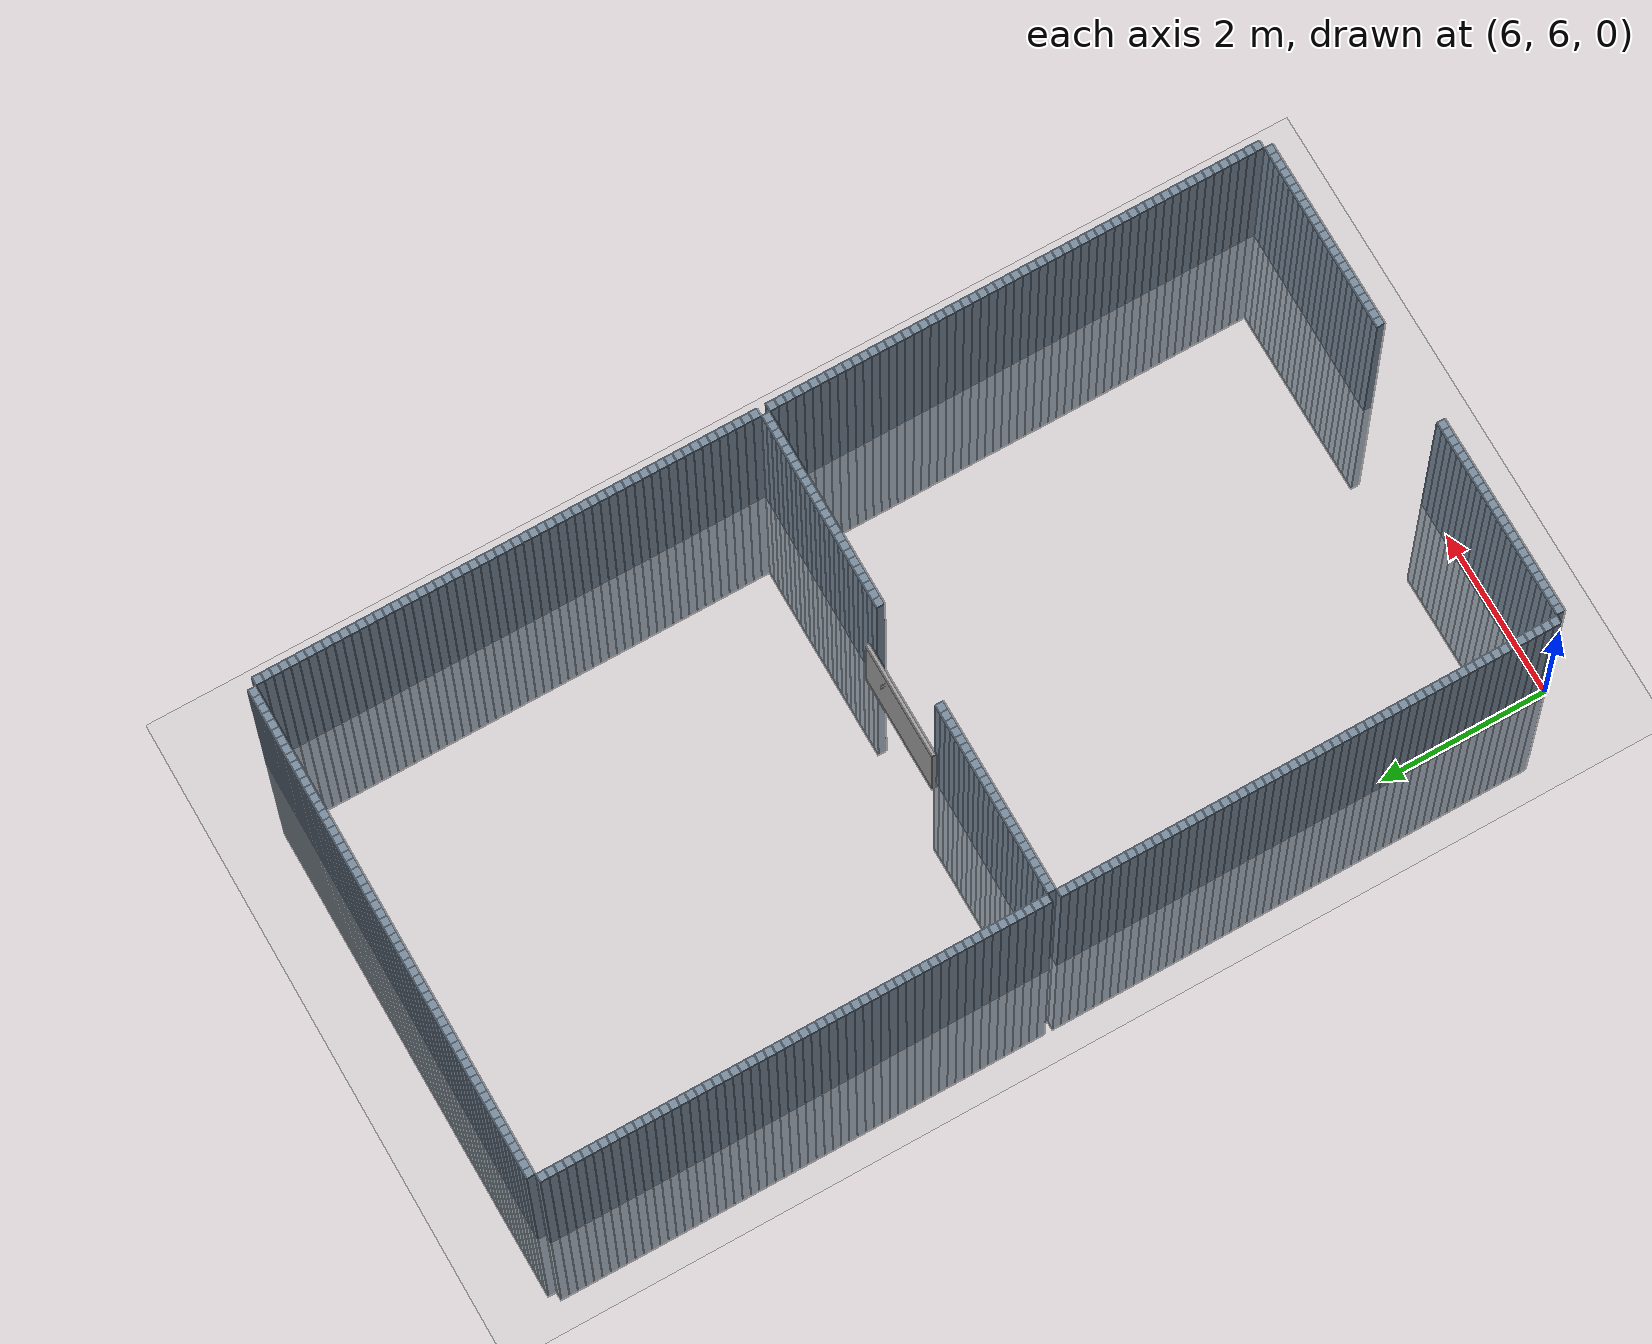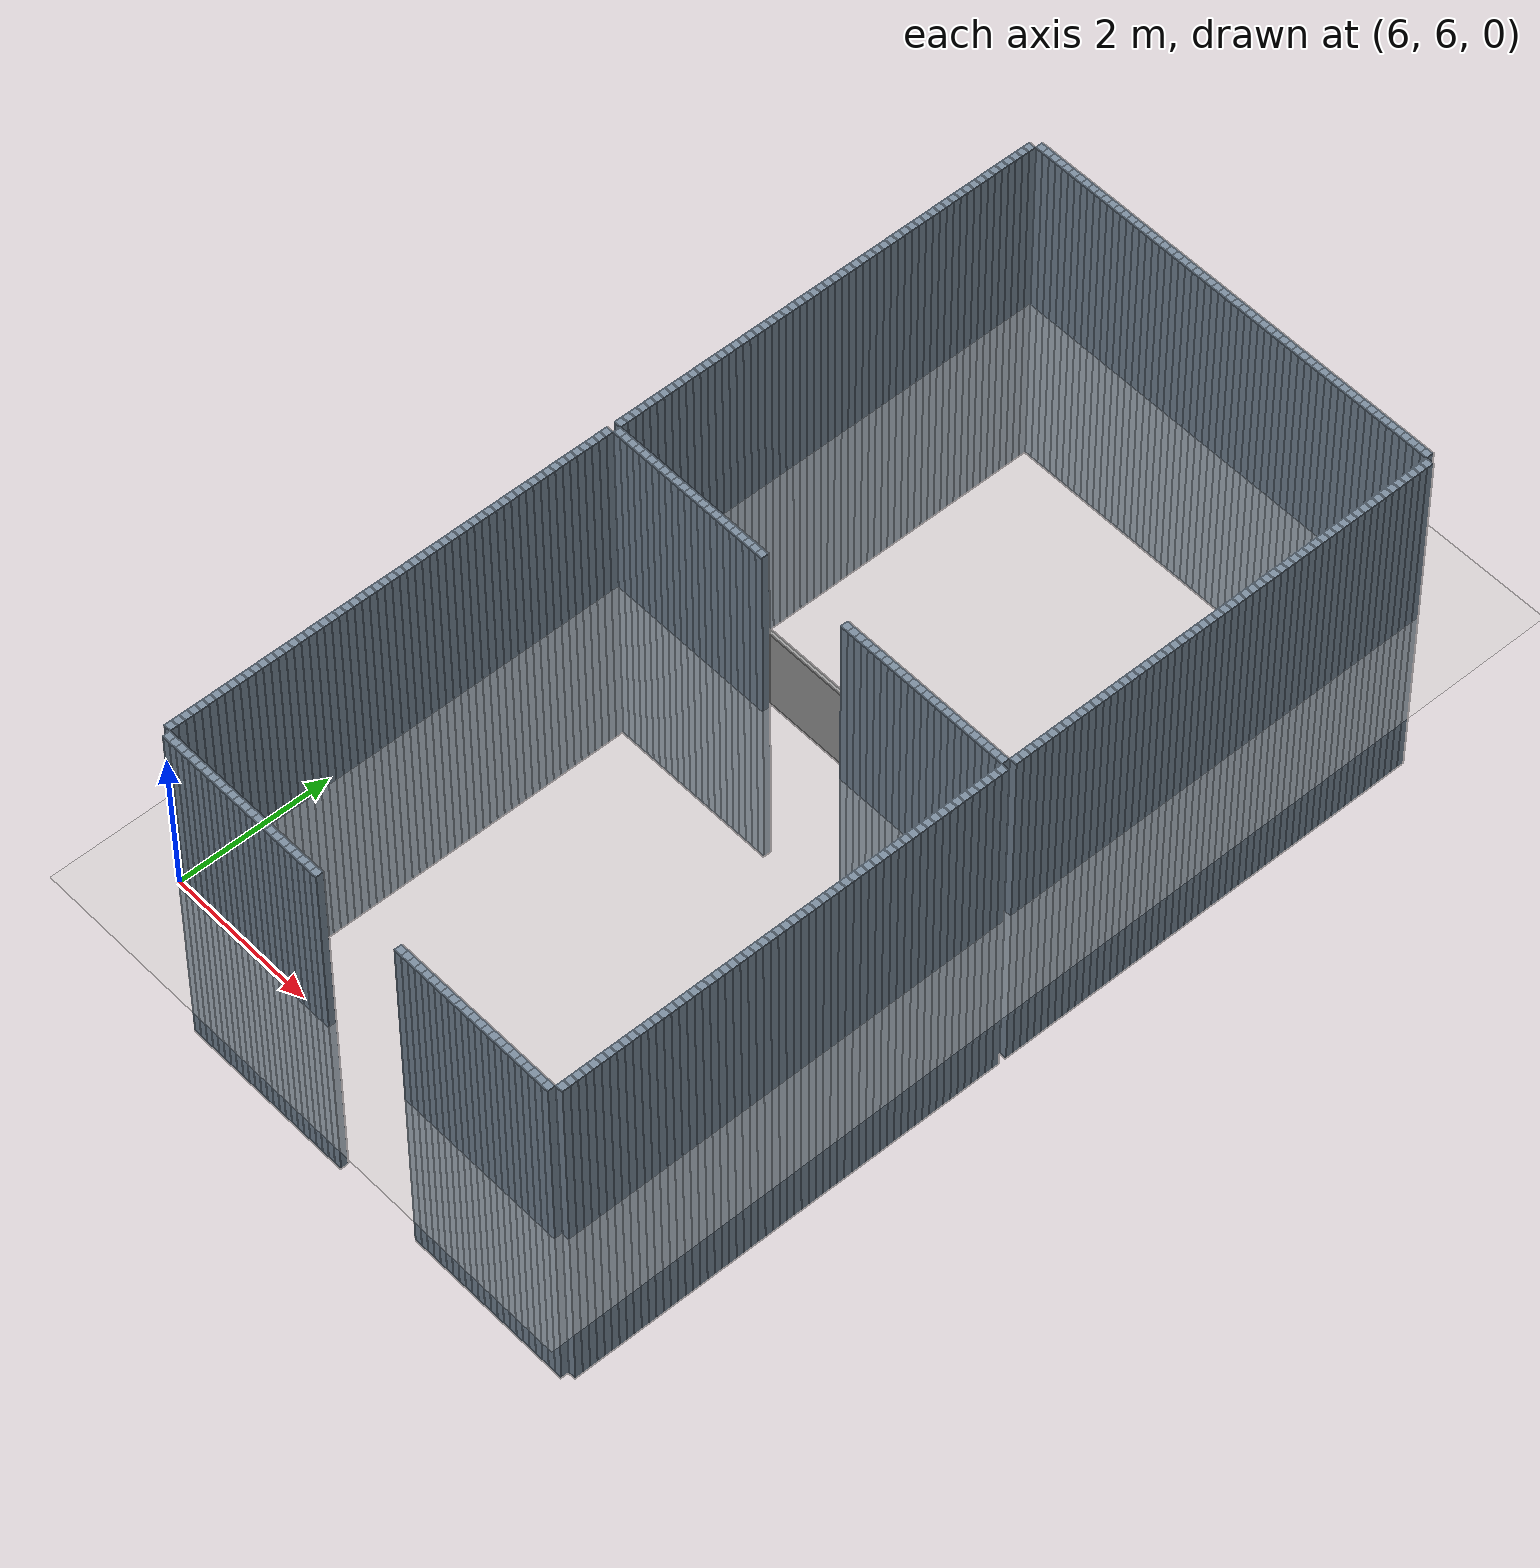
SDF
<sdf version="1.6">
 <world name="default">
  <light name="sun" type="directional">
   <pose>0 0 10 0 -0 0</pose>
   <diffuse>0.8 0.8 0.8 1</diffuse>
   <specular>0.1 0.1 0.1 1</specular>
   <attenuation>
    <range>1000</range>
    <constant>0.9</constant>
    <linear>0.01</linear>
    <quadratic>0.001</quadratic>
   </attenuation>
   <direction>-0.5 0.5 -1</direction>
  </light>
  <model name="ground_plane">
   <static>1</static>
   <link name="link">
    <collision name="collision">
     <geometry><plane><normal>0 0 1</normal><size>100 100</size></plane></geometry>
     <surface><friction><ode><mu>100</mu><mu2>50</mu2></ode></friction></surface>
    </collision>
    <visual name="visual">
     <cast_shadows>0</cast_shadows>
     <geometry><plane><normal>0 0 1</normal><size>100 100</size></plane></geometry>
     <material>
      <script><uri>file://media/materials/scripts/gazebo.material</uri><name>Gazebo/Grey</name></script>
     </material>
    </visual>
   </link>
  </model>
  <gravity>0 0 -9.8</gravity>
  <magnetic_field>6e-06 2.3e-05 -4.2e-05</magnetic_field>
  <atmosphere type="adiabatic"/>
  <physics name="default_physics" default="0" type="ode">
   <max_step_size>0.001</max_step_size>
   <real_time_factor>1</real_time_factor>
   <real_time_update_rate>1000</real_time_update_rate>
  </physics>
  <scene><ambient>0.4 0.4 0.4 1</ambient><background>0.7 0.7 0.7 1</background><shadows>1</shadows></scene>
  <spherical_coordinates>
   <surface_model>EARTH_WGS84</surface_model>
   <latitude_deg>0</latitude_deg>
   <longitude_deg>0</longitude_deg>
   <elevation>0</elevation>
   <heading_deg>0</heading_deg>
  </spherical_coordinates>
  <model name="unit_cylinder_242">
   <static>1</static>
   <pose>6 6.1 0 0 -0 0</pose>
   <link name="link">
    <inertial>
     <mass>1</mass>
     <inertia><ixx>0.145833</ixx><ixy>0</ixy><ixz>0</ixz><iyy>0.145833</iyy><iyz>0</iyz><izz>0.125</izz></inertia>
    </inertial>
    <collision name="collision"><geometry><box><size>0.1 0.1 5</size></box></geometry></collision>
    <visual name="visual">
     <geometry><box><size>0.1 0.1 5</size></box></geometry>
     <material><ambient>0.466667 0.533333 0.6 1</ambient><diffuse>0.466667 0.533333 0.6 1</diffuse></material>
     <material>
      <script><name>Gazebo/Grey</name><uri>file://media/materials/scripts/gazebo.material</uri></script>
     </material>
    </visual>
   </link>
  </model>
  <model name="unit_cylinder_243">
   <static>1</static>
   <pose>6 6.2 0 0 -0 0</pose>
   <link name="link">
    <inertial>
     <mass>1</mass>
     <inertia><ixx>0.145833</ixx><ixy>0</ixy><ixz>0</ixz><iyy>0.145833</iyy><iyz>0</iyz><izz>0.125</izz></inertia>
    </inertial>
    <collision name="collision"><geometry><box><size>0.1 0.1 5</size></box></geometry></collision>
    <visual name="visual">
     <geometry><box><size>0.1 0.1 5</size></box></geometry>
     <material><ambient>0.466667 0.533333 0.6 1</ambient><diffuse>0.466667 0.533333 0.6 1</diffuse></material>
     <material>
      <script><name>Gazebo/Grey</name><uri>file://media/materials/scripts/gazebo.material</uri></script>
     </material>
    </visual>
   </link>
  </model>
  <model name="unit_cylinder_244">
   <static>1</static>
   <pose>6 6.3 0 0 -0 0</pose>
   <link name="link">
    <inertial>
     <mass>1</mass>
     <inertia><ixx>0.145833</ixx><ixy>0</ixy><ixz>0</ixz><iyy>0.145833</iyy><iyz>0</iyz><izz>0.125</izz></inertia>
    </inertial>
    <collision name="collision"><geometry><box><size>0.1 0.1 5</size></box></geometry></collision>
    <visual name="visual">
     <geometry><box><size>0.1 0.1 5</size></box></geometry>
     <material><ambient>0.466667 0.533333 0.6 1</ambient><diffuse>0.466667 0.533333 0.6 1</diffuse></material>
     <material>
      <script><name>Gazebo/Grey</name><uri>file://media/materials/scripts/gazebo.material</uri></script>
     </material>
    </visual>
   </link>
  </model>
  <model name="unit_cylinder_245">
   <static>1</static>
   <pose>6 6.4 0 0 -0 0</pose>
   <link name="link">
    <inertial>
     <mass>1</mass>
     <inertia><ixx>0.145833</ixx><ixy>0</ixy><ixz>0</ixz><iyy>0.145833</iyy><iyz>0</iyz><izz>0.125</izz></inertia>
    </inertial>
    <collision name="collision"><geometry><box><size>0.1 0.1 5</size></box></geometry></collision>
    <visual name="visual">
     <geometry><box><size>0.1 0.1 5</size></box></geometry>
     <material><ambient>0.466667 0.533333 0.6 1</ambient><diffuse>0.466667 0.533333 0.6 1</diffuse></material>
     <material>
      <script><name>Gazebo/Grey</name><uri>file://media/materials/scripts/gazebo.material</uri></script>
     </material>
    </visual>
   </link>
  </model>
  <model name="unit_cylinder_246">
   <static>1</static>
   <pose>6 6.5 0 0 -0 0</pose>
   <link name="link">
    <inertial>
     <mass>1</mass>
     <inertia><ixx>0.145833</ixx><ixy>0</ixy><ixz>0</ixz><iyy>0.145833</iyy><iyz>0</iyz><izz>0.125</izz></inertia>
    </inertial>
    <collision name="collision"><geometry><box><size>0.1 0.1 5</size></box></geometry></collision>
    <visual name="visual">
     <geometry><box><size>0.1 0.1 5</size></box></geometry>
     <material><ambient>0.466667 0.533333 0.6 1</ambient><diffuse>0.466667 0.533333 0.6 1</diffuse></material>
     <material>
      <script><name>Gazebo/Grey</name><uri>file://media/materials/scripts/gazebo.material</uri></script>
     </material>
    </visual>
   </link>
  </model>
  <model name="unit_cylinder_247">
   <static>1</static>
   <pose>6 6.6 0 0 -0 0</pose>
   <link name="link">
    <inertial>
     <mass>1</mass>
     <inertia><ixx>0.145833</ixx><ixy>0</ixy><ixz>0</ixz><iyy>0.145833</iyy><iyz>0</iyz><izz>0.125</izz></inertia>
    </inertial>
    <collision name="collision"><geometry><box><size>0.1 0.1 5</size></box></geometry></collision>
    <visual name="visual">
     <geometry><box><size>0.1 0.1 5</size></box></geometry>
     <material><ambient>0.466667 0.533333 0.6 1</ambient><diffuse>0.466667 0.533333 0.6 1</diffuse></material>
     <material>
      <script><name>Gazebo/Grey</name><uri>file://media/materials/scripts/gazebo.material</uri></script>
     </material>
    </visual>
   </link>
  </model>
  <model name="unit_cylinder_248">
   <static>1</static>
   <pose>6 6.7 0 0 -0 0</pose>
   <link name="link">
    <inertial>
     <mass>1</mass>
     <inertia><ixx>0.145833</ixx><ixy>0</ixy><ixz>0</ixz><iyy>0.145833</iyy><iyz>0</iyz><izz>0.125</izz></inertia>
    </inertial>
    <collision name="collision"><geometry><box><size>0.1 0.1 5</size></box></geometry></collision>
    <visual name="visual">
     <geometry><box><size>0.1 0.1 5</size></box></geometry>
     <material><ambient>0.466667 0.533333 0.6 1</ambient><diffuse>0.466667 0.533333 0.6 1</diffuse></material>
     <material>
      <script><name>Gazebo/Grey</name><uri>file://media/materials/scripts/gazebo.material</uri></script>
     </material>
    </visual>
   </link>
  </model>
  <model name="unit_cylinder_249">
   <static>1</static>
   <pose>6 6.8 0 0 -0 0</pose>
   <link name="link">
    <inertial>
     <mass>1</mass>
     <inertia><ixx>0.145833</ixx><ixy>0</ixy><ixz>0</ixz><iyy>0.145833</iyy><iyz>0</iyz><izz>0.125</izz></inertia>
    </inertial>
    <collision name="collision"><geometry><box><size>0.1 0.1 5</size></box></geometry></collision>
    <visual name="visual">
     <geometry><box><size>0.1 0.1 5</size></box></geometry>
     <material><ambient>0.466667 0.533333 0.6 1</ambient><diffuse>0.466667 0.533333 0.6 1</diffuse></material>
     <material>
      <script><name>Gazebo/Grey</name><uri>file://media/materials/scripts/gazebo.material</uri></script>
     </material>
    </visual>
   </link>
  </model>
  <model name="unit_cylinder_250">
   <static>1</static>
   <pose>6 6.9 0 0 -0 0</pose>
   <link name="link">
    <inertial>
     <mass>1</mass>
     <inertia><ixx>0.145833</ixx><ixy>0</ixy><ixz>0</ixz><iyy>0.145833</iyy><iyz>0</iyz><izz>0.125</izz></inertia>
    </inertial>
    <collision name="collision"><geometry><box><size>0.1 0.1 5</size></box></geometry></collision>
    <visual name="visual">
     <geometry><box><size>0.1 0.1 5</size></box></geometry>
     <material><ambient>0.466667 0.533333 0.6 1</ambient><diffuse>0.466667 0.533333 0.6 1</diffuse></material>
     <material>
      <script><name>Gazebo/Grey</name><uri>file://media/materials/scripts/gazebo.material</uri></script>
     </material>
    </visual>
   </link>
  </model>
  <model name="unit_cylinder_251">
   <static>1</static>
   <pose>6 7 0 0 -0 0</pose>
   <link name="link">
    <inertial>
     <mass>1</mass>
     <inertia><ixx>0.145833</ixx><ixy>0</ixy><ixz>0</ixz><iyy>0.145833</iyy><iyz>0</iyz><izz>0.125</izz></inertia>
    </inertial>
    <collision name="collision"><geometry><box><size>0.1 0.1 5</size></box></geometry></collision>
    <visual name="visual">
     <geometry><box><size>0.1 0.1 5</size></box></geometry>
     <material><ambient>0.466667 0.533333 0.6 1</ambient><diffuse>0.466667 0.533333 0.6 1</diffuse></material>
     <material>
      <script><name>Gazebo/Grey</name><uri>file://media/materials/scripts/gazebo.material</uri></script>
     </material>
    </visual>
   </link>
  </model>
  <model name="unit_cylinder_252">
   <static>1</static>
   <pose>6 7.1 0 0 -0 0</pose>
   <link name="link">
    <inertial>
     <mass>1</mass>
     <inertia><ixx>0.145833</ixx><ixy>0</ixy><ixz>0</ixz><iyy>0.145833</iyy><iyz>0</iyz><izz>0.125</izz></inertia>
    </inertial>
    <collision name="collision"><geometry><box><size>0.1 0.1 5</size></box></geometry></collision>
    <visual name="visual">
     <geometry><box><size>0.1 0.1 5</size></box></geometry>
     <material><ambient>0.466667 0.533333 0.6 1</ambient><diffuse>0.466667 0.533333 0.6 1</diffuse></material>
     <material>
      <script><name>Gazebo/Grey</name><uri>file://media/materials/scripts/gazebo.material</uri></script>
     </material>
    </visual>
   </link>
  </model>
  <model name="unit_cylinder_253">
   <static>1</static>
   <pose>6 7.2 0 0 -0 0</pose>
   <link name="link">
    <inertial>
     <mass>1</mass>
     <inertia><ixx>0.145833</ixx><ixy>0</ixy><ixz>0</ixz><iyy>0.145833</iyy><iyz>0</iyz><izz>0.125</izz></inertia>
    </inertial>
    <collision name="collision"><geometry><box><size>0.1 0.1 5</size></box></geometry></collision>
    <visual name="visual">
     <geometry><box><size>0.1 0.1 5</size></box></geometry>
     <material><ambient>0.466667 0.533333 0.6 1</ambient><diffuse>0.466667 0.533333 0.6 1</diffuse></material>
     <material>
      <script><name>Gazebo/Grey</name><uri>file://media/materials/scripts/gazebo.material</uri></script>
     </material>
    </visual>
   </link>
  </model>
  <model name="unit_cylinder_254">
   <static>1</static>
   <pose>6 7.3 0 0 -0 0</pose>
   <link name="link">
    <inertial>
     <mass>1</mass>
     <inertia><ixx>0.145833</ixx><ixy>0</ixy><ixz>0</ixz><iyy>0.145833</iyy><iyz>0</iyz><izz>0.125</izz></inertia>
    </inertial>
    <collision name="collision"><geometry><box><size>0.1 0.1 5</size></box></geometry></collision>
    <visual name="visual">
     <geometry><box><size>0.1 0.1 5</size></box></geometry>
     <material><ambient>0.466667 0.533333 0.6 1</ambient><diffuse>0.466667 0.533333 0.6 1</diffuse></material>
     <material>
      <script><name>Gazebo/Grey</name><uri>file://media/materials/scripts/gazebo.material</uri></script>
     </material>
    </visual>
   </link>
  </model>
  <model name="unit_cylinder_255">
   <static>1</static>
   <pose>6 7.4 0 0 -0 0</pose>
   <link name="link">
    <inertial>
     <mass>1</mass>
     <inertia><ixx>0.145833</ixx><ixy>0</ixy><ixz>0</ixz><iyy>0.145833</iyy><iyz>0</iyz><izz>0.125</izz></inertia>
    </inertial>
    <collision name="collision"><geometry><box><size>0.1 0.1 5</size></box></geometry></collision>
    <visual name="visual">
     <geometry><box><size>0.1 0.1 5</size></box></geometry>
     <material><ambient>0.466667 0.533333 0.6 1</ambient><diffuse>0.466667 0.533333 0.6 1</diffuse></material>
     <material>
      <script><name>Gazebo/Grey</name><uri>file://media/materials/scripts/gazebo.material</uri></script>
     </material>
    </visual>
   </link>
  </model>
  <model name="unit_cylinder_256">
   <static>1</static>
   <pose>6 7.5 0 0 -0 0</pose>
   <link name="link">
    <inertial>
     <mass>1</mass>
     <inertia><ixx>0.145833</ixx><ixy>0</ixy><ixz>0</ixz><iyy>0.145833</iyy><iyz>0</iyz><izz>0.125</izz></inertia>
    </inertial>
    <collision name="collision"><geometry><box><size>0.1 0.1 5</size></box></geometry></collision>
    <visual name="visual">
     <geometry><box><size>0.1 0.1 5</size></box></geometry>
     <material><ambient>0.466667 0.533333 0.6 1</ambient><diffuse>0.466667 0.533333 0.6 1</diffuse></material>
     <material>
      <script><name>Gazebo/Grey</name><uri>file://media/materials/scripts/gazebo.material</uri></script>
     </material>
    </visual>
   </link>
  </model>
  <model name="unit_cylinder_257">
   <static>1</static>
   <pose>6 7.6 0 0 -0 0</pose>
   <link name="link">
    <inertial>
     <mass>1</mass>
     <inertia><ixx>0.145833</ixx><ixy>0</ixy><ixz>0</ixz><iyy>0.145833</iyy><iyz>0</iyz><izz>0.125</izz></inertia>
    </inertial>
    <collision name="collision"><geometry><box><size>0.1 0.1 5</size></box></geometry></collision>
    <visual name="visual">
     <geometry><box><size>0.1 0.1 5</size></box></geometry>
     <material><ambient>0.466667 0.533333 0.6 1</ambient><diffuse>0.466667 0.533333 0.6 1</diffuse></material>
     <material>
      <script><name>Gazebo/Grey</name><uri>file://media/materials/scripts/gazebo.material</uri></script>
     </material>
    </visual>
   </link>
  </model>
  <model name="unit_cylinder_258">
   <static>1</static>
   <pose>6 7.7 0 0 -0 0</pose>
   <link name="link">
    <inertial>
     <mass>1</mass>
     <inertia><ixx>0.145833</ixx><ixy>0</ixy><ixz>0</ixz><iyy>0.145833</iyy><iyz>0</iyz><izz>0.125</izz></inertia>
    </inertial>
    <collision name="collision"><geometry><box><size>0.1 0.1 5</size></box></geometry></collision>
    <visual name="visual">
     <geometry><box><size>0.1 0.1 5</size></box></geometry>
     <material><ambient>0.466667 0.533333 0.6 1</ambient><diffuse>0.466667 0.533333 0.6 1</diffuse></material>
     <material>
      <script><name>Gazebo/Grey</name><uri>file://media/materials/scripts/gazebo.material</uri></script>
     </material>
    </visual>
   </link>
  </model>
  <model name="unit_cylinder_259">
   <static>1</static>
   <pose>6 7.8 0 0 -0 0</pose>
   <link name="link">
    <inertial>
     <mass>1</mass>
     <inertia><ixx>0.145833</ixx><ixy>0</ixy><ixz>0</ixz><iyy>0.145833</iyy><iyz>0</iyz><izz>0.125</izz></inertia>
    </inertial>
    <collision name="collision"><geometry><box><size>0.1 0.1 5</size></box></geometry></collision>
    <visual name="visual">
     <geometry><box><size>0.1 0.1 5</size></box></geometry>
     <material><ambient>0.466667 0.533333 0.6 1</ambient><diffuse>0.466667 0.533333 0.6 1</diffuse></material>
     <material>
      <script><name>Gazebo/Grey</name><uri>file://media/materials/scripts/gazebo.material</uri></script>
     </material>
    </visual>
   </link>
  </model>
  <model name="unit_cylinder_260">
   <static>1</static>
   <pose>6 7.9 0 0 -0 0</pose>
   <link name="link">
    <inertial>
     <mass>1</mass>
     <inertia><ixx>0.145833</ixx><ixy>0</ixy><ixz>0</ixz><iyy>0.145833</iyy><iyz>0</iyz><izz>0.125</izz></inertia>
    </inertial>
    <collision name="collision"><geometry><box><size>0.1 0.1 5</size></box></geometry></collision>
    <visual name="visual">
     <geometry><box><size>0.1 0.1 5</size></box></geometry>
     <material><ambient>0.466667 0.533333 0.6 1</ambient><diffuse>0.466667 0.533333 0.6 1</diffuse></material>
     <material>
      <script><name>Gazebo/Grey</name><uri>file://media/materials/scripts/gazebo.material</uri></script>
     </material>
    </visual>
   </link>
  </model>
  <model name="unit_cylinder_261">
   <static>1</static>
   <pose>6 8 0 0 -0 0</pose>
   <link name="link">
    <inertial>
     <mass>1</mass>
     <inertia><ixx>0.145833</ixx><ixy>0</ixy><ixz>0</ixz><iyy>0.145833</iyy><iyz>0</iyz><izz>0.125</izz></inertia>
    </inertial>
    <collision name="collision"><geometry><box><size>0.1 0.1 5</size></box></geometry></collision>
    <visual name="visual">
     <geometry><box><size>0.1 0.1 5</size></box></geometry>
     <material><ambient>0.466667 0.533333 0.6 1</ambient><diffuse>0.466667 0.533333 0.6 1</diffuse></material>
     <material>
      <script><name>Gazebo/Grey</name><uri>file://media/materials/scripts/gazebo.material</uri></script>
     </material>
    </visual>
   </link>
  </model>
  <model name="unit_cylinder_262">
   <static>1</static>
   <pose>6 8.1 0 0 -0 0</pose>
   <link name="link">
    <inertial>
     <mass>1</mass>
     <inertia><ixx>0.145833</ixx><ixy>0</ixy><ixz>0</ixz><iyy>0.145833</iyy><iyz>0</iyz><izz>0.125</izz></inertia>
    </inertial>
    <collision name="collision"><geometry><box><size>0.1 0.1 5</size></box></geometry></collision>
    <visual name="visual">
     <geometry><box><size>0.1 0.1 5</size></box></geometry>
     <material><ambient>0.466667 0.533333 0.6 1</ambient><diffuse>0.466667 0.533333 0.6 1</diffuse></material>
     <material>
      <script><name>Gazebo/Grey</name><uri>file://media/materials/scripts/gazebo.material</uri></script>
     </material>
    </visual>
   </link>
  </model>
  <model name="unit_cylinder_263">
   <static>1</static>
   <pose>6 8.2 0 0 -0 0</pose>
   <link name="link">
    <inertial>
     <mass>1</mass>
     <inertia><ixx>0.145833</ixx><ixy>0</ixy><ixz>0</ixz><iyy>0.145833</iyy><iyz>0</iyz><izz>0.125</izz></inertia>
    </inertial>
    <collision name="collision"><geometry><box><size>0.1 0.1 5</size></box></geometry></collision>
    <visual name="visual">
     <geometry><box><size>0.1 0.1 5</size></box></geometry>
     <material><ambient>0.466667 0.533333 0.6 1</ambient><diffuse>0.466667 0.533333 0.6 1</diffuse></material>
     <material>
      <script><name>Gazebo/Grey</name><uri>file://media/materials/scripts/gazebo.material</uri></script>
     </material>
    </visual>
   </link>
  </model>
  <model name="unit_cylinder_264">
   <static>1</static>
   <pose>6 8.3 0 0 -0 0</pose>
   <link name="link">
    <inertial>
     <mass>1</mass>
     <inertia><ixx>0.145833</ixx><ixy>0</ixy><ixz>0</ixz><iyy>0.145833</iyy><iyz>0</iyz><izz>0.125</izz></inertia>
    </inertial>
    <collision name="collision"><geometry><box><size>0.1 0.1 5</size></box></geometry></collision>
    <visual name="visual">
     <geometry><box><size>0.1 0.1 5</size></box></geometry>
     <material><ambient>0.466667 0.533333 0.6 1</ambient><diffuse>0.466667 0.533333 0.6 1</diffuse></material>
     <material>
      <script><name>Gazebo/Grey</name><uri>file://media/materials/scripts/gazebo.material</uri></script>
     </material>
    </visual>
   </link>
  </model>
  <model name="unit_cylinder_265">
   <static>1</static>
   <pose>6 8.4 0 0 -0 0</pose>
   <link name="link">
    <inertial>
     <mass>1</mass>
     <inertia><ixx>0.145833</ixx><ixy>0</ixy><ixz>0</ixz><iyy>0.145833</iyy><iyz>0</iyz><izz>0.125</izz></inertia>
    </inertial>
    <collision name="collision"><geometry><box><size>0.1 0.1 5</size></box></geometry></collision>
    <visual name="visual">
     <geometry><box><size>0.1 0.1 5</size></box></geometry>
     <material><ambient>0.466667 0.533333 0.6 1</ambient><diffuse>0.466667 0.533333 0.6 1</diffuse></material>
     <material>
      <script><name>Gazebo/Grey</name><uri>file://media/materials/scripts/gazebo.material</uri></script>
     </material>
    </visual>
   </link>
  </model>
  <model name="unit_cylinder_266">
   <static>1</static>
   <pose>6 8.5 0 0 -0 0</pose>
   <link name="link">
    <inertial>
     <mass>1</mass>
     <inertia><ixx>0.145833</ixx><ixy>0</ixy><ixz>0</ixz><iyy>0.145833</iyy><iyz>0</iyz><izz>0.125</izz></inertia>
    </inertial>
    <collision name="collision"><geometry><box><size>0.1 0.1 5</size></box></geometry></collision>
    <visual name="visual">
     <geometry><box><size>0.1 0.1 5</size></box></geometry>
     <material><ambient>0.466667 0.533333 0.6 1</ambient><diffuse>0.466667 0.533333 0.6 1</diffuse></material>
     <material>
      <script><name>Gazebo/Grey</name><uri>file://media/materials/scripts/gazebo.material</uri></script>
     </material>
    </visual>
   </link>
  </model>
  <model name="unit_cylinder_267">
   <static>1</static>
   <pose>6 8.6 0 0 -0 0</pose>
   <link name="link">
    <inertial>
     <mass>1</mass>
     <inertia><ixx>0.145833</ixx><ixy>0</ixy><ixz>0</ixz><iyy>0.145833</iyy><iyz>0</iyz><izz>0.125</izz></inertia>
    </inertial>
    <collision name="collision"><geometry><box><size>0.1 0.1 5</size></box></geometry></collision>
    <visual name="visual">
     <geometry><box><size>0.1 0.1 5</size></box></geometry>
     <material><ambient>0.466667 0.533333 0.6 1</ambient><diffuse>0.466667 0.533333 0.6 1</diffuse></material>
     <material>
      <script><name>Gazebo/Grey</name><uri>file://media/materials/scripts/gazebo.material</uri></script>
     </material>
    </visual>
   </link>
  </model>
  <model name="unit_cylinder_268">
   <static>1</static>
   <pose>6 8.7 0 0 -0 0</pose>
   <link name="link">
    <inertial>
     <mass>1</mass>
     <inertia><ixx>0.145833</ixx><ixy>0</ixy><ixz>0</ixz><iyy>0.145833</iyy><iyz>0</iyz><izz>0.125</izz></inertia>
    </inertial>
    <collision name="collision"><geometry><box><size>0.1 0.1 5</size></box></geometry></collision>
    <visual name="visual">
     <geometry><box><size>0.1 0.1 5</size></box></geometry>
     <material><ambient>0.466667 0.533333 0.6 1</ambient><diffuse>0.466667 0.533333 0.6 1</diffuse></material>
     <material>
      <script><name>Gazebo/Grey</name><uri>file://media/materials/scripts/gazebo.material</uri></script>
     </material>
    </visual>
   </link>
  </model>
  <model name="unit_cylinder_269">
   <static>1</static>
   <pose>6 8.8 0 0 -0 0</pose>
   <link name="link">
    <inertial>
     <mass>1</mass>
     <inertia><ixx>0.145833</ixx><ixy>0</ixy><ixz>0</ixz><iyy>0.145833</iyy><iyz>0</iyz><izz>0.125</izz></inertia>
    </inertial>
    <collision name="collision"><geometry><box><size>0.1 0.1 5</size></box></geometry></collision>
    <visual name="visual">
     <geometry><box><size>0.1 0.1 5</size></box></geometry>
     <material><ambient>0.466667 0.533333 0.6 1</ambient><diffuse>0.466667 0.533333 0.6 1</diffuse></material>
     <material>
      <script><name>Gazebo/Grey</name><uri>file://media/materials/scripts/gazebo.material</uri></script>
     </material>
    </visual>
   </link>
  </model>
  <model name="unit_cylinder_270">
   <static>1</static>
   <pose>6 8.9 0 0 -0 0</pose>
   <link name="link">
    <inertial>
     <mass>1</mass>
     <inertia><ixx>0.145833</ixx><ixy>0</ixy><ixz>0</ixz><iyy>0.145833</iyy><iyz>0</iyz><izz>0.125</izz></inertia>
    </inertial>
    <collision name="collision"><geometry><box><size>0.1 0.1 5</size></box></geometry></collision>
    <visual name="visual">
     <geometry><box><size>0.1 0.1 5</size></box></geometry>
     <material><ambient>0.466667 0.533333 0.6 1</ambient><diffuse>0.466667 0.533333 0.6 1</diffuse></material>
     <material>
      <script><name>Gazebo/Grey</name><uri>file://media/materials/scripts/gazebo.material</uri></script>
     </material>
    </visual>
   </link>
  </model>
  <model name="unit_cylinder_271">
   <static>1</static>
   <pose>6 9 0 0 -0 0</pose>
   <link name="link">
    <inertial>
     <mass>1</mass>
     <inertia><ixx>0.145833</ixx><ixy>0</ixy><ixz>0</ixz><iyy>0.145833</iyy><iyz>0</iyz><izz>0.125</izz></inertia>
    </inertial>
    <collision name="collision"><geometry><box><size>0.1 0.1 5</size></box></geometry></collision>
    <visual name="visual">
     <geometry><box><size>0.1 0.1 5</size></box></geometry>
     <material><ambient>0.466667 0.533333 0.6 1</ambient><diffuse>0.466667 0.533333 0.6 1</diffuse></material>
     <material>
      <script><name>Gazebo/Grey</name><uri>file://media/materials/scripts/gazebo.material</uri></script>
     </material>
    </visual>
   </link>
  </model>
  <model name="unit_cylinder_272">
   <static>1</static>
   <pose>6 9.1 0 0 -0 0</pose>
   <link name="link">
    <inertial>
     <mass>1</mass>
     <inertia><ixx>0.145833</ixx><ixy>0</ixy><ixz>0</ixz><iyy>0.145833</iyy><iyz>0</iyz><izz>0.125</izz></inertia>
    </inertial>
    <collision name="collision"><geometry><box><size>0.1 0.1 5</size></box></geometry></collision>
    <visual name="visual">
     <geometry><box><size>0.1 0.1 5</size></box></geometry>
     <material><ambient>0.466667 0.533333 0.6 1</ambient><diffuse>0.466667 0.533333 0.6 1</diffuse></material>
     <material>
      <script><name>Gazebo/Grey</name><uri>file://media/materials/scripts/gazebo.material</uri></script>
     </material>
    </visual>
   </link>
  </model>
  <model name="unit_cylinder_273">
   <static>1</static>
   <pose>6 9.2 0 0 -0 0</pose>
   <link name="link">
    <inertial>
     <mass>1</mass>
     <inertia><ixx>0.145833</ixx><ixy>0</ixy><ixz>0</ixz><iyy>0.145833</iyy><iyz>0</iyz><izz>0.125</izz></inertia>
    </inertial>
    <collision name="collision"><geometry><box><size>0.1 0.1 5</size></box></geometry></collision>
    <visual name="visual">
     <geometry><box><size>0.1 0.1 5</size></box></geometry>
     <material><ambient>0.466667 0.533333 0.6 1</ambient><diffuse>0.466667 0.533333 0.6 1</diffuse></material>
     <material>
      <script><name>Gazebo/Grey</name><uri>file://media/materials/scripts/gazebo.material</uri></script>
     </material>
    </visual>
   </link>
  </model>
  <model name="unit_cylinder_274">
   <static>1</static>
   <pose>6 9.3 0 0 -0 0</pose>
   <link name="link">
    <inertial>
     <mass>1</mass>
     <inertia><ixx>0.145833</ixx><ixy>0</ixy><ixz>0</ixz><iyy>0.145833</iyy><iyz>0</iyz><izz>0.125</izz></inertia>
    </inertial>
    <collision name="collision"><geometry><box><size>0.1 0.1 5</size></box></geometry></collision>
    <visual name="visual">
     <geometry><box><size>0.1 0.1 5</size></box></geometry>
     <material><ambient>0.466667 0.533333 0.6 1</ambient><diffuse>0.466667 0.533333 0.6 1</diffuse></material>
     <material>
      <script><name>Gazebo/Grey</name><uri>file://media/materials/scripts/gazebo.material</uri></script>
     </material>
    </visual>
   </link>
  </model>
  <model name="unit_cylinder_275">
   <static>1</static>
   <pose>6 9.4 0 0 -0 0</pose>
   <link name="link">
    <inertial>
     <mass>1</mass>
     <inertia><ixx>0.145833</ixx><ixy>0</ixy><ixz>0</ixz><iyy>0.145833</iyy><iyz>0</iyz><izz>0.125</izz></inertia>
    </inertial>
    <collision name="collision"><geometry><box><size>0.1 0.1 5</size></box></geometry></collision>
    <visual name="visual">
     <geometry><box><size>0.1 0.1 5</size></box></geometry>
     <material><ambient>0.466667 0.533333 0.6 1</ambient><diffuse>0.466667 0.533333 0.6 1</diffuse></material>
     <material>
      <script><name>Gazebo/Grey</name><uri>file://media/materials/scripts/gazebo.material</uri></script>
     </material>
    </visual>
   </link>
  </model>
  <model name="unit_cylinder_276">
   <static>1</static>
   <pose>6 9.5 0 0 -0 0</pose>
   <link name="link">
    <inertial>
     <mass>1</mass>
     <inertia><ixx>0.145833</ixx><ixy>0</ixy><ixz>0</ixz><iyy>0.145833</iyy><iyz>0</iyz><izz>0.125</izz></inertia>
    </inertial>
    <collision name="collision"><geometry><box><size>0.1 0.1 5</size></box></geometry></collision>
    <visual name="visual">
     <geometry><box><size>0.1 0.1 5</size></box></geometry>
     <material><ambient>0.466667 0.533333 0.6 1</ambient><diffuse>0.466667 0.533333 0.6 1</diffuse></material>
     <material>
      <script><name>Gazebo/Grey</name><uri>file://media/materials/scripts/gazebo.material</uri></script>
     </material>
    </visual>
   </link>
  </model>
  <model name="unit_cylinder_277">
   <static>1</static>
   <pose>6 9.6 0 0 -0 0</pose>
   <link name="link">
    <inertial>
     <mass>1</mass>
     <inertia><ixx>0.145833</ixx><ixy>0</ixy><ixz>0</ixz><iyy>0.145833</iyy><iyz>0</iyz><izz>0.125</izz></inertia>
    </inertial>
    <collision name="collision"><geometry><box><size>0.1 0.1 5</size></box></geometry></collision>
    <visual name="visual">
     <geometry><box><size>0.1 0.1 5</size></box></geometry>
     <material><ambient>0.466667 0.533333 0.6 1</ambient><diffuse>0.466667 0.533333 0.6 1</diffuse></material>
     <material>
      <script><name>Gazebo/Grey</name><uri>file://media/materials/scripts/gazebo.material</uri></script>
     </material>
    </visual>
   </link>
  </model>
  <model name="unit_cylinder_278">
   <static>1</static>
   <pose>6 9.7 0 0 -0 0</pose>
   <link name="link">
    <inertial>
     <mass>1</mass>
     <inertia><ixx>0.145833</ixx><ixy>0</ixy><ixz>0</ixz><iyy>0.145833</iyy><iyz>0</iyz><izz>0.125</izz></inertia>
    </inertial>
    <collision name="collision"><geometry><box><size>0.1 0.1 5</size></box></geometry></collision>
    <visual name="visual">
     <geometry><box><size>0.1 0.1 5</size></box></geometry>
     <material><ambient>0.466667 0.533333 0.6 1</ambient><diffuse>0.466667 0.533333 0.6 1</diffuse></material>
     <material>
      <script><name>Gazebo/Grey</name><uri>file://media/materials/scripts/gazebo.material</uri></script>
     </material>
    </visual>
   </link>
  </model>
  <model name="unit_cylinder_279">
   <static>1</static>
   <pose>6 9.8 0 0 -0 0</pose>
   <link name="link">
    <inertial>
     <mass>1</mass>
     <inertia><ixx>0.145833</ixx><ixy>0</ixy><ixz>0</ixz><iyy>0.145833</iyy><iyz>0</iyz><izz>0.125</izz></inertia>
    </inertial>
    <collision name="collision"><geometry><box><size>0.1 0.1 5</size></box></geometry></collision>
    <visual name="visual">
     <geometry><box><size>0.1 0.1 5</size></box></geometry>
     <material><ambient>0.466667 0.533333 0.6 1</ambient><diffuse>0.466667 0.533333 0.6 1</diffuse></material>
     <material>
      <script><name>Gazebo/Grey</name><uri>file://media/materials/scripts/gazebo.material</uri></script>
     </material>
    </visual>
   </link>
  </model>
  <model name="unit_cylinder_280">
   <static>1</static>
   <pose>6 9.9 0 0 -0 0</pose>
   <link name="link">
    <inertial>
     <mass>1</mass>
     <inertia><ixx>0.145833</ixx><ixy>0</ixy><ixz>0</ixz><iyy>0.145833</iyy><iyz>0</iyz><izz>0.125</izz></inertia>
    </inertial>
    <collision name="collision"><geometry><box><size>0.1 0.1 5</size></box></geometry></collision>
    <visual name="visual">
     <geometry><box><size>0.1 0.1 5</size></box></geometry>
     <material><ambient>0.466667 0.533333 0.6 1</ambient><diffuse>0.466667 0.533333 0.6 1</diffuse></material>
     <material>
      <script><name>Gazebo/Grey</name><uri>file://media/materials/scripts/gazebo.material</uri></script>
     </material>
    </visual>
   </link>
  </model>
  <model name="unit_cylinder_281">
   <static>1</static>
   <pose>6 10 0 0 -0 0</pose>
   <link name="link">
    <inertial>
     <mass>1</mass>
     <inertia><ixx>0.145833</ixx><ixy>0</ixy><ixz>0</ixz><iyy>0.145833</iyy><iyz>0</iyz><izz>0.125</izz></inertia>
    </inertial>
    <collision name="collision"><geometry><box><size>0.1 0.1 5</size></box></geometry></collision>
    <visual name="visual">
     <geometry><box><size>0.1 0.1 5</size></box></geometry>
     <material><ambient>0.466667 0.533333 0.6 1</ambient><diffuse>0.466667 0.533333 0.6 1</diffuse></material>
     <material>
      <script><name>Gazebo/Grey</name><uri>file://media/materials/scripts/gazebo.material</uri></script>
     </material>
    </visual>
   </link>
  </model>
  <model name="unit_cylinder_282">
   <static>1</static>
   <pose>6 10.1 0 0 -0 0</pose>
   <link name="link">
    <inertial>
     <mass>1</mass>
     <inertia><ixx>0.145833</ixx><ixy>0</ixy><ixz>0</ixz><iyy>0.145833</iyy><iyz>0</iyz><izz>0.125</izz></inertia>
    </inertial>
    <collision name="collision"><geometry><box><size>0.1 0.1 5</size></box></geometry></collision>
    <visual name="visual">
     <geometry><box><size>0.1 0.1 5</size></box></geometry>
     <material><ambient>0.466667 0.533333 0.6 1</ambient><diffuse>0.466667 0.533333 0.6 1</diffuse></material>
     <material>
      <script><name>Gazebo/Grey</name><uri>file://media/materials/scripts/gazebo.material</uri></script>
     </material>
    </visual>
   </link>
  </model>
  <model name="unit_cylinder_283">
   <static>1</static>
   <pose>6 10.2 0 0 -0 0</pose>
   <link name="link">
    <inertial>
     <mass>1</mass>
     <inertia><ixx>0.145833</ixx><ixy>0</ixy><ixz>0</ixz><iyy>0.145833</iyy><iyz>0</iyz><izz>0.125</izz></inertia>
    </inertial>
    <collision name="collision"><geometry><box><size>0.1 0.1 5</size></box></geometry></collision>
    <visual name="visual">
     <geometry><box><size>0.1 0.1 5</size></box></geometry>
     <material><ambient>0.466667 0.533333 0.6 1</ambient><diffuse>0.466667 0.533333 0.6 1</diffuse></material>
     <material>
      <script><name>Gazebo/Grey</name><uri>file://media/materials/scripts/gazebo.material</uri></script>
     </material>
    </visual>
   </link>
  </model>
  <model name="unit_cylinder_284">
   <static>1</static>
   <pose>6 10.3 0 0 -0 0</pose>
   <link name="link">
    <inertial>
     <mass>1</mass>
     <inertia><ixx>0.145833</ixx><ixy>0</ixy><ixz>0</ixz><iyy>0.145833</iyy><iyz>0</iyz><izz>0.125</izz></inertia>
    </inertial>
    <collision name="collision"><geometry><box><size>0.1 0.1 5</size></box></geometry></collision>
    <visual name="visual">
     <geometry><box><size>0.1 0.1 5</size></box></geometry>
     <material><ambient>0.466667 0.533333 0.6 1</ambient><diffuse>0.466667 0.533333 0.6 1</diffuse></material>
     <material>
      <script><name>Gazebo/Grey</name><uri>file://media/materials/scripts/gazebo.material</uri></script>
     </material>
    </visual>
   </link>
  </model>
  <model name="unit_cylinder_285">
   <static>1</static>
   <pose>6 10.4 0 0 -0 0</pose>
   <link name="link">
    <inertial>
     <mass>1</mass>
     <inertia><ixx>0.145833</ixx><ixy>0</ixy><ixz>0</ixz><iyy>0.145833</iyy><iyz>0</iyz><izz>0.125</izz></inertia>
    </inertial>
    <collision name="collision"><geometry><box><size>0.1 0.1 5</size></box></geometry></collision>
    <visual name="visual">
     <geometry><box><size>0.1 0.1 5</size></box></geometry>
     <material><ambient>0.466667 0.533333 0.6 1</ambient><diffuse>0.466667 0.533333 0.6 1</diffuse></material>
     <material>
      <script><name>Gazebo/Grey</name><uri>file://media/materials/scripts/gazebo.material</uri></script>
     </material>
    </visual>
   </link>
  </model>
  <model name="unit_cylinder_286">
   <static>1</static>
   <pose>6 10.5 0 0 -0 0</pose>
   <link name="link">
    <inertial>
     <mass>1</mass>
     <inertia><ixx>0.145833</ixx><ixy>0</ixy><ixz>0</ixz><iyy>0.145833</iyy><iyz>0</iyz><izz>0.125</izz></inertia>
    </inertial>
    <collision name="collision"><geometry><box><size>0.1 0.1 5</size></box></geometry></collision>
    <visual name="visual">
     <geometry><box><size>0.1 0.1 5</size></box></geometry>
     <material><ambient>0.466667 0.533333 0.6 1</ambient><diffuse>0.466667 0.533333 0.6 1</diffuse></material>
     <material>
      <script><name>Gazebo/Grey</name><uri>file://media/materials/scripts/gazebo.material</uri></script>
     </material>
    </visual>
   </link>
  </model>
  <model name="unit_cylinder_287">
   <static>1</static>
   <pose>6 10.6 0 0 -0 0</pose>
   <link name="link">
    <inertial>
     <mass>1</mass>
     <inertia><ixx>0.145833</ixx><ixy>0</ixy><ixz>0</ixz><iyy>0.145833</iyy><iyz>0</iyz><izz>0.125</izz></inertia>
    </inertial>
    <collision name="collision"><geometry><box><size>0.1 0.1 5</size></box></geometry></collision>
    <visual name="visual">
     <geometry><box><size>0.1 0.1 5</size></box></geometry>
     <material><ambient>0.466667 0.533333 0.6 1</ambient><diffuse>0.466667 0.533333 0.6 1</diffuse></material>
     <material>
      <script><name>Gazebo/Grey</name><uri>file://media/materials/scripts/gazebo.material</uri></script>
     </material>
    </visual>
   </link>
  </model>
  <model name="unit_cylinder_288">
   <static>1</static>
   <pose>6 10.7 0 0 -0 0</pose>
   <link name="link">
    <inertial>
     <mass>1</mass>
     <inertia><ixx>0.145833</ixx><ixy>0</ixy><ixz>0</ixz><iyy>0.145833</iyy><iyz>0</iyz><izz>0.125</izz></inertia>
    </inertial>
    <collision name="collision"><geometry><box><size>0.1 0.1 5</size></box></geometry></collision>
    <visual name="visual">
     <geometry><box><size>0.1 0.1 5</size></box></geometry>
     <material><ambient>0.466667 0.533333 0.6 1</ambient><diffuse>0.466667 0.533333 0.6 1</diffuse></material>
     <material>
      <script><name>Gazebo/Grey</name><uri>file://media/materials/scripts/gazebo.material</uri></script>
     </material>
    </visual>
   </link>
  </model>
  <model name="unit_cylinder_289">
   <static>1</static>
   <pose>6 10.8 0 0 -0 0</pose>
   <link name="link">
    <inertial>
     <mass>1</mass>
     <inertia><ixx>0.145833</ixx><ixy>0</ixy><ixz>0</ixz><iyy>0.145833</iyy><iyz>0</iyz><izz>0.125</izz></inertia>
    </inertial>
    <collision name="collision"><geometry><box><size>0.1 0.1 5</size></box></geometry></collision>
    <visual name="visual">
     <geometry><box><size>0.1 0.1 5</size></box></geometry>
     <material><ambient>0.466667 0.533333 0.6 1</ambient><diffuse>0.466667 0.533333 0.6 1</diffuse></material>
     <material>
      <script><name>Gazebo/Grey</name><uri>file://media/materials/scripts/gazebo.material</uri></script>
     </material>
    </visual>
   </link>
  </model>
  <model name="unit_cylinder_290">
   <static>1</static>
   <pose>6 10.9 0 0 -0 0</pose>
   <link name="link">
    <inertial>
     <mass>1</mass>
     <inertia><ixx>0.145833</ixx><ixy>0</ixy><ixz>0</ixz><iyy>0.145833</iyy><iyz>0</iyz><izz>0.125</izz></inertia>
    </inertial>
    <collision name="collision"><geometry><box><size>0.1 0.1 5</size></box></geometry></collision>
    <visual name="visual">
     <geometry><box><size>0.1 0.1 5</size></box></geometry>
     <material><ambient>0.466667 0.533333 0.6 1</ambient><diffuse>0.466667 0.533333 0.6 1</diffuse></material>
     <material>
      <script><name>Gazebo/Grey</name><uri>file://media/materials/scripts/gazebo.material</uri></script>
     </material>
    </visual>
   </link>
  </model>
  <model name="unit_cylinder_291">
   <static>1</static>
   <pose>6 11 0 0 -0 0</pose>
   <link name="link">
    <inertial>
     <mass>1</mass>
     <inertia><ixx>0.145833</ixx><ixy>0</ixy><ixz>0</ixz><iyy>0.145833</iyy><iyz>0</iyz><izz>0.125</izz></inertia>
    </inertial>
    <collision name="collision"><geometry><box><size>0.1 0.1 5</size></box></geometry></collision>
    <visual name="visual">
     <geometry><box><size>0.1 0.1 5</size></box></geometry>
     <material><ambient>0.466667 0.533333 0.6 1</ambient><diffuse>0.466667 0.533333 0.6 1</diffuse></material>
     <material>
      <script><name>Gazebo/Grey</name><uri>file://media/materials/scripts/gazebo.material</uri></script>
     </material>
    </visual>
   </link>
  </model>
  <model name="unit_cylinder_292">
   <static>1</static>
   <pose>6 11.1 0 0 -0 0</pose>
   <link name="link">
    <inertial>
     <mass>1</mass>
     <inertia><ixx>0.145833</ixx><ixy>0</ixy><ixz>0</ixz><iyy>0.145833</iyy><iyz>0</iyz><izz>0.125</izz></inertia>
    </inertial>
    <collision name="collision"><geometry><box><size>0.1 0.1 5</size></box></geometry></collision>
    <visual name="visual">
     <geometry><box><size>0.1 0.1 5</size></box></geometry>
     <material><ambient>0.466667 0.533333 0.6 1</ambient><diffuse>0.466667 0.533333 0.6 1</diffuse></material>
     <material>
      <script><name>Gazebo/Grey</name><uri>file://media/materials/scripts/gazebo.material</uri></script>
     </material>
    </visual>
   </link>
  </model>
  <model name="unit_cylinder_293">
   <static>1</static>
   <pose>6 11.2 0 0 -0 0</pose>
   <link name="link">
    <inertial>
     <mass>1</mass>
     <inertia><ixx>0.145833</ixx><ixy>0</ixy><ixz>0</ixz><iyy>0.145833</iyy><iyz>0</iyz><izz>0.125</izz></inertia>
    </inertial>
    <collision name="collision"><geometry><box><size>0.1 0.1 5</size></box></geometry></collision>
    <visual name="visual">
     <geometry><box><size>0.1 0.1 5</size></box></geometry>
     <material><ambient>0.466667 0.533333 0.6 1</ambient><diffuse>0.466667 0.533333 0.6 1</diffuse></material>
     <material>
      <script><name>Gazebo/Grey</name><uri>file://media/materials/scripts/gazebo.material</uri></script>
     </material>
    </visual>
   </link>
  </model>
  <model name="unit_cylinder_294">
   <static>1</static>
   <pose>6 11.3 0 0 -0 0</pose>
   <link name="link">
    <inertial>
     <mass>1</mass>
     <inertia><ixx>0.145833</ixx><ixy>0</ixy><ixz>0</ixz><iyy>0.145833</iyy><iyz>0</iyz><izz>0.125</izz></inertia>
    </inertial>
    <collision name="collision"><geometry><box><size>0.1 0.1 5</size></box></geometry></collision>
    <visual name="visual">
     <geometry><box><size>0.1 0.1 5</size></box></geometry>
     <material><ambient>0.466667 0.533333 0.6 1</ambient><diffuse>0.466667 0.533333 0.6 1</diffuse></material>
     <material>
      <script><name>Gazebo/Grey</name><uri>file://media/materials/scripts/gazebo.material</uri></script>
     </material>
    </visual>
   </link>
  </model>
  <model name="unit_cylinder_295">
   <static>1</static>
   <pose>6 11.4 0 0 -0 0</pose>
   <link name="link">
    <inertial>
     <mass>1</mass>
     <inertia><ixx>0.145833</ixx><ixy>0</ixy><ixz>0</ixz><iyy>0.145833</iyy><iyz>0</iyz><izz>0.125</izz></inertia>
    </inertial>
    <collision name="collision"><geometry><box><size>0.1 0.1 5</size></box></geometry></collision>
    <visual name="visual">
     <geometry><box><size>0.1 0.1 5</size></box></geometry>
     <material><ambient>0.466667 0.533333 0.6 1</ambient><diffuse>0.466667 0.533333 0.6 1</diffuse></material>
     <material>
      <script><name>Gazebo/Grey</name><uri>file://media/materials/scripts/gazebo.material</uri></script>
     </material>
    </visual>
   </link>
  </model>
  <model name="unit_cylinder_296">
   <static>1</static>
   <pose>6 11.5 0 0 -0 0</pose>
   <link name="link">
    <inertial>
     <mass>1</mass>
     <inertia><ixx>0.145833</ixx><ixy>0</ixy><ixz>0</ixz><iyy>0.145833</iyy><iyz>0</iyz><izz>0.125</izz></inertia>
    </inertial>
    <collision name="collision"><geometry><box><size>0.1 0.1 5</size></box></geometry></collision>
    <visual name="visual">
     <geometry><box><size>0.1 0.1 5</size></box></geometry>
     <material><ambient>0.466667 0.533333 0.6 1</ambient><diffuse>0.466667 0.533333 0.6 1</diffuse></material>
     <material>
      <script><name>Gazebo/Grey</name><uri>file://media/materials/scripts/gazebo.material</uri></script>
     </material>
    </visual>
   </link>
  </model>
  <model name="unit_cylinder_297">
   <static>1</static>
   <pose>6 11.6 0 0 -0 0</pose>
   <link name="link">
    <inertial>
     <mass>1</mass>
     <inertia><ixx>0.145833</ixx><ixy>0</ixy><ixz>0</ixz><iyy>0.145833</iyy><iyz>0</iyz><izz>0.125</izz></inertia>
    </inertial>
    <collision name="collision"><geometry><box><size>0.1 0.1 5</size></box></geometry></collision>
    <visual name="visual">
     <geometry><box><size>0.1 0.1 5</size></box></geometry>
     <material><ambient>0.466667 0.533333 0.6 1</ambient><diffuse>0.466667 0.533333 0.6 1</diffuse></material>
     <material>
      <script><name>Gazebo/Grey</name><uri>file://media/materials/scripts/gazebo.material</uri></script>
     </material>
    </visual>
   </link>
  </model>
  <model name="unit_cylinder_298">
   <static>1</static>
   <pose>6 11.7 0 0 -0 0</pose>
   <link name="link">
    <inertial>
     <mass>1</mass>
     <inertia><ixx>0.145833</ixx><ixy>0</ixy><ixz>0</ixz><iyy>0.145833</iyy><iyz>0</iyz><izz>0.125</izz></inertia>
    </inertial>
    <collision name="collision"><geometry><box><size>0.1 0.1 5</size></box></geometry></collision>
    <visual name="visual">
     <geometry><box><size>0.1 0.1 5</size></box></geometry>
     <material><ambient>0.466667 0.533333 0.6 1</ambient><diffuse>0.466667 0.533333 0.6 1</diffuse></material>
     <material>
      <script><name>Gazebo/Grey</name><uri>file://media/materials/scripts/gazebo.material</uri></script>
     </material>
    </visual>
   </link>
  </model>
  <model name="unit_cylinder_299">
   <static>1</static>
   <pose>6 11.8 0 0 -0 0</pose>
   <link name="link">
    <inertial>
     <mass>1</mass>
     <inertia><ixx>0.145833</ixx><ixy>0</ixy><ixz>0</ixz><iyy>0.145833</iyy><iyz>0</iyz><izz>0.125</izz></inertia>
    </inertial>
    <collision name="collision"><geometry><box><size>0.1 0.1 5</size></box></geometry></collision>
    <visual name="visual">
     <geometry><box><size>0.1 0.1 5</size></box></geometry>
     <material><ambient>0.466667 0.533333 0.6 1</ambient><diffuse>0.466667 0.533333 0.6 1</diffuse></material>
     <material>
      <script><name>Gazebo/Grey</name><uri>file://media/materials/scripts/gazebo.material</uri></script>
     </material>
    </visual>
   </link>
  </model>
  <model name="unit_cylinder_300">
   <static>1</static>
   <pose>6 11.9 0 0 -0 0</pose>
   <link name="link">
    <inertial>
     <mass>1</mass>
     <inertia><ixx>0.145833</ixx><ixy>0</ixy><ixz>0</ixz><iyy>0.145833</iyy><iyz>0</iyz><izz>0.125</izz></inertia>
    </inertial>
    <collision name="collision"><geometry><box><size>0.1 0.1 5</size></box></geometry></collision>
    <visual name="visual">
     <geometry><box><size>0.1 0.1 5</size></box></geometry>
     <material><ambient>0.466667 0.533333 0.6 1</ambient><diffuse>0.466667 0.533333 0.6 1</diffuse></material>
     <material>
      <script><name>Gazebo/Grey</name><uri>file://media/materials/scripts/gazebo.material</uri></script>
     </material>
    </visual>
   </link>
  </model>
  <model name="unit_cylinder_302">
   <static>1</static>
   <pose>6 12.1 0 0 -0 0</pose>
   <link name="link">
    <inertial>
     <mass>1</mass>
     <inertia><ixx>0.145833</ixx><ixy>0</ixy><ixz>0</ixz><iyy>0.145833</iyy><iyz>0</iyz><izz>0.125</izz></inertia>
    </inertial>
    <collision name="collision"><geometry><box><size>0.1 0.1 5</size></box></geometry></collision>
    <visual name="visual">
     <geometry><box><size>0.1 0.1 5</size></box></geometry>
     <material><ambient>0.466667 0.533333 0.6 1</ambient><diffuse>0.466667 0.533333 0.6 1</diffuse></material>
     <material>
      <script><name>Gazebo/Grey</name><uri>file://media/materials/scripts/gazebo.material</uri></script>
     </material>
    </visual>
   </link>
  </model>
  <model name="unit_cylinder_303">
   <static>1</static>
   <pose>6 12.2 0 0 -0 0</pose>
   <link name="link">
    <inertial>
     <mass>1</mass>
     <inertia><ixx>0.145833</ixx><ixy>0</ixy><ixz>0</ixz><iyy>0.145833</iyy><iyz>0</iyz><izz>0.125</izz></inertia>
    </inertial>
    <collision name="collision"><geometry><box><size>0.1 0.1 5</size></box></geometry></collision>
    <visual name="visual">
     <geometry><box><size>0.1 0.1 5</size></box></geometry>
     <material><ambient>0.466667 0.533333 0.6 1</ambient><diffuse>0.466667 0.533333 0.6 1</diffuse></material>
     <material>
      <script><name>Gazebo/Grey</name><uri>file://media/materials/scripts/gazebo.material</uri></script>
     </material>
    </visual>
   </link>
  </model>
  <model name="unit_cylinder_304">
   <static>1</static>
   <pose>6 12.3 0 0 -0 0</pose>
   <link name="link">
    <inertial>
     <mass>1</mass>
     <inertia><ixx>0.145833</ixx><ixy>0</ixy><ixz>0</ixz><iyy>0.145833</iyy><iyz>0</iyz><izz>0.125</izz></inertia>
    </inertial>
    <collision name="collision"><geometry><box><size>0.1 0.1 5</size></box></geometry></collision>
    <visual name="visual">
     <geometry><box><size>0.1 0.1 5</size></box></geometry>
     <material><ambient>0.466667 0.533333 0.6 1</ambient><diffuse>0.466667 0.533333 0.6 1</diffuse></material>
     <material>
      <script><name>Gazebo/Grey</name><uri>file://media/materials/scripts/gazebo.material</uri></script>
     </material>
    </visual>
   </link>
  </model>
  <model name="unit_cylinder_305">
   <static>1</static>
   <pose>6 12.4 0 0 -0 0</pose>
   <link name="link">
    <inertial>
     <mass>1</mass>
     <inertia><ixx>0.145833</ixx><ixy>0</ixy><ixz>0</ixz><iyy>0.145833</iyy><iyz>0</iyz><izz>0.125</izz></inertia>
    </inertial>
    <collision name="collision"><geometry><box><size>0.1 0.1 5</size></box></geometry></collision>
    <visual name="visual">
     <geometry><box><size>0.1 0.1 5</size></box></geometry>
     <material><ambient>0.466667 0.533333 0.6 1</ambient><diffuse>0.466667 0.533333 0.6 1</diffuse></material>
     <material>
      <script><name>Gazebo/Grey</name><uri>file://media/materials/scripts/gazebo.material</uri></script>
     </material>
    </visual>
   </link>
  </model>
  <model name="unit_cylinder_306">
   <static>1</static>
   <pose>6 12.5 0 0 -0 0</pose>
   <link name="link">
    <inertial>
     <mass>1</mass>
     <inertia><ixx>0.145833</ixx><ixy>0</ixy><ixz>0</ixz><iyy>0.145833</iyy><iyz>0</iyz><izz>0.125</izz></inertia>
    </inertial>
    <collision name="collision"><geometry><box><size>0.1 0.1 5</size></box></geometry></collision>
    <visual name="visual">
     <geometry><box><size>0.1 0.1 5</size></box></geometry>
     <material><ambient>0.466667 0.533333 0.6 1</ambient><diffuse>0.466667 0.533333 0.6 1</diffuse></material>
     <material>
      <script><name>Gazebo/Grey</name><uri>file://media/materials/scripts/gazebo.material</uri></script>
     </material>
    </visual>
   </link>
  </model>
  <model name="unit_cylinder_307">
   <static>1</static>
   <pose>6 12.6 0 0 -0 0</pose>
   <link name="link">
    <inertial>
     <mass>1</mass>
     <inertia><ixx>0.145833</ixx><ixy>0</ixy><ixz>0</ixz><iyy>0.145833</iyy><iyz>0</iyz><izz>0.125</izz></inertia>
    </inertial>
    <collision name="collision"><geometry><box><size>0.1 0.1 5</size></box></geometry></collision>
    <visual name="visual">
     <geometry><box><size>0.1 0.1 5</size></box></geometry>
     <material><ambient>0.466667 0.533333 0.6 1</ambient><diffuse>0.466667 0.533333 0.6 1</diffuse></material>
     <material>
      <script><name>Gazebo/Grey</name><uri>file://media/materials/scripts/gazebo.material</uri></script>
     </material>
    </visual>
   </link>
  </model>
  <model name="unit_cylinder_308">
   <static>1</static>
   <pose>6 12.7 0 0 -0 0</pose>
   <link name="link">
    <inertial>
     <mass>1</mass>
     <inertia><ixx>0.145833</ixx><ixy>0</ixy><ixz>0</ixz><iyy>0.145833</iyy><iyz>0</iyz><izz>0.125</izz></inertia>
    </inertial>
    <collision name="collision"><geometry><box><size>0.1 0.1 5</size></box></geometry></collision>
    <visual name="visual">
     <geometry><box><size>0.1 0.1 5</size></box></geometry>
     <material><ambient>0.466667 0.533333 0.6 1</ambient><diffuse>0.466667 0.533333 0.6 1</diffuse></material>
     <material>
      <script><name>Gazebo/Grey</name><uri>file://media/materials/scripts/gazebo.material</uri></script>
     </material>
    </visual>
   </link>
  </model>
  <model name="unit_cylinder_309">
   <static>1</static>
   <pose>6 12.8 0 0 -0 0</pose>
   <link name="link">
    <inertial>
     <mass>1</mass>
     <inertia><ixx>0.145833</ixx><ixy>0</ixy><ixz>0</ixz><iyy>0.145833</iyy><iyz>0</iyz><izz>0.125</izz></inertia>
    </inertial>
    <collision name="collision"><geometry><box><size>0.1 0.1 5</size></box></geometry></collision>
    <visual name="visual">
     <geometry><box><size>0.1 0.1 5</size></box></geometry>
     <material><ambient>0.466667 0.533333 0.6 1</ambient><diffuse>0.466667 0.533333 0.6 1</diffuse></material>
     <material>
      <script><name>Gazebo/Grey</name><uri>file://media/materials/scripts/gazebo.material</uri></script>
     </material>
    </visual>
   </link>
  </model>
  <model name="unit_cylinder_310">
   <static>1</static>
   <pose>6 12.9 0 0 -0 0</pose>
   <link name="link">
    <inertial>
     <mass>1</mass>
     <inertia><ixx>0.145833</ixx><ixy>0</ixy><ixz>0</ixz><iyy>0.145833</iyy><iyz>0</iyz><izz>0.125</izz></inertia>
    </inertial>
    <collision name="collision"><geometry><box><size>0.1 0.1 5</size></box></geometry></collision>
    <visual name="visual">
     <geometry><box><size>0.1 0.1 5</size></box></geometry>
     <material><ambient>0.466667 0.533333 0.6 1</ambient><diffuse>0.466667 0.533333 0.6 1</diffuse></material>
     <material>
      <script><name>Gazebo/Grey</name><uri>file://media/materials/scripts/gazebo.material</uri></script>
     </material>
    </visual>
   </link>
  </model>
  <model name="unit_cylinder_311">
   <static>1</static>
   <pose>6 13 0 0 -0 0</pose>
   <link name="link">
    <inertial>
     <mass>1</mass>
     <inertia><ixx>0.145833</ixx><ixy>0</ixy><ixz>0</ixz><iyy>0.145833</iyy><iyz>0</iyz><izz>0.125</izz></inertia>
    </inertial>
    <collision name="collision"><geometry><box><size>0.1 0.1 5</size></box></geometry></collision>
    <visual name="visual">
     <geometry><box><size>0.1 0.1 5</size></box></geometry>
     <material><ambient>0.466667 0.533333 0.6 1</ambient><diffuse>0.466667 0.533333 0.6 1</diffuse></material>
     <material>
      <script><name>Gazebo/Grey</name><uri>file://media/materials/scripts/gazebo.material</uri></script>
     </material>
    </visual>
   </link>
  </model>
  <model name="unit_cylinder_312">
   <static>1</static>
   <pose>6 13.1 0 0 -0 0</pose>
   <link name="link">
    <inertial>
     <mass>1</mass>
     <inertia><ixx>0.145833</ixx><ixy>0</ixy><ixz>0</ixz><iyy>0.145833</iyy><iyz>0</iyz><izz>0.125</izz></inertia>
    </inertial>
    <collision name="collision"><geometry><box><size>0.1 0.1 5</size></box></geometry></collision>
    <visual name="visual">
     <geometry><box><size>0.1 0.1 5</size></box></geometry>
     <material><ambient>0.466667 0.533333 0.6 1</ambient><diffuse>0.466667 0.533333 0.6 1</diffuse></material>
     <material>
      <script><name>Gazebo/Grey</name><uri>file://media/materials/scripts/gazebo.material</uri></script>
     </material>
    </visual>
   </link>
  </model>
  <model name="unit_cylinder_313">
   <static>1</static>
   <pose>6 13.2 0 0 -0 0</pose>
   <link name="link">
    <inertial>
     <mass>1</mass>
     <inertia><ixx>0.145833</ixx><ixy>0</ixy><ixz>0</ixz><iyy>0.145833</iyy><iyz>0</iyz><izz>0.125</izz></inertia>
    </inertial>
    <collision name="collision"><geometry><box><size>0.1 0.1 5</size></box></geometry></collision>
    <visual name="visual">
     <geometry><box><size>0.1 0.1 5</size></box></geometry>
     <material><ambient>0.466667 0.533333 0.6 1</ambient><diffuse>0.466667 0.533333 0.6 1</diffuse></material>
     <material>
      <script><name>Gazebo/Grey</name><uri>file://media/materials/scripts/gazebo.material</uri></script>
     </material>
    </visual>
   </link>
  </model>
  <model name="unit_cylinder_314">
   <static>1</static>
   <pose>6 13.3 0 0 -0 0</pose>
   <link name="link">
    <inertial>
     <mass>1</mass>
     <inertia><ixx>0.145833</ixx><ixy>0</ixy><ixz>0</ixz><iyy>0.145833</iyy><iyz>0</iyz><izz>0.125</izz></inertia>
    </inertial>
    <collision name="collision"><geometry><box><size>0.1 0.1 5</size></box></geometry></collision>
    <visual name="visual">
     <geometry><box><size>0.1 0.1 5</size></box></geometry>
     <material><ambient>0.466667 0.533333 0.6 1</ambient><diffuse>0.466667 0.533333 0.6 1</diffuse></material>
     <material>
      <script><name>Gazebo/Grey</name><uri>file://media/materials/scripts/gazebo.material</uri></script>
     </material>
    </visual>
   </link>
  </model>
  <model name="unit_cylinder_315">
   <static>1</static>
   <pose>6 13.4 0 0 -0 0</pose>
   <link name="link">
    <inertial>
     <mass>1</mass>
     <inertia><ixx>0.145833</ixx><ixy>0</ixy><ixz>0</ixz><iyy>0.145833</iyy><iyz>0</iyz><izz>0.125</izz></inertia>
    </inertial>
    <collision name="collision"><geometry><box><size>0.1 0.1 5</size></box></geometry></collision>
    <visual name="visual">
     <geometry><box><size>0.1 0.1 5</size></box></geometry>
     <material><ambient>0.466667 0.533333 0.6 1</ambient><diffuse>0.466667 0.533333 0.6 1</diffuse></material>
     <material>
      <script><name>Gazebo/Grey</name><uri>file://media/materials/scripts/gazebo.material</uri></script>
     </material>
    </visual>
   </link>
  </model>
  <model name="unit_cylinder_316">
   <static>1</static>
   <pose>6 13.5 0 0 -0 0</pose>
   <link name="link">
    <inertial>
     <mass>1</mass>
     <inertia><ixx>0.145833</ixx><ixy>0</ixy><ixz>0</ixz><iyy>0.145833</iyy><iyz>0</iyz><izz>0.125</izz></inertia>
    </inertial>
    <collision name="collision"><geometry><box><size>0.1 0.1 5</size></box></geometry></collision>
    <visual name="visual">
     <geometry><box><size>0.1 0.1 5</size></box></geometry>
     <material><ambient>0.466667 0.533333 0.6 1</ambient><diffuse>0.466667 0.533333 0.6 1</diffuse></material>
     <material>
      <script><name>Gazebo/Grey</name><uri>file://media/materials/scripts/gazebo.material</uri></script>
     </material>
    </visual>
   </link>
  </model>
  <model name="unit_cylinder_317">
   <static>1</static>
   <pose>6 13.6 0 0 -0 0</pose>
   <link name="link">
    <inertial>
     <mass>1</mass>
     <inertia><ixx>0.145833</ixx><ixy>0</ixy><ixz>0</ixz><iyy>0.145833</iyy><iyz>0</iyz><izz>0.125</izz></inertia>
    </inertial>
    <collision name="collision"><geometry><box><size>0.1 0.1 5</size></box></geometry></collision>
    <visual name="visual">
     <geometry><box><size>0.1 0.1 5</size></box></geometry>
     <material><ambient>0.466667 0.533333 0.6 1</ambient><diffuse>0.466667 0.533333 0.6 1</diffuse></material>
     <material>
      <script><name>Gazebo/Grey</name><uri>file://media/materials/scripts/gazebo.material</uri></script>
     </material>
    </visual>
   </link>
  </model>
  <model name="unit_cylinder_318">
   <static>1</static>
   <pose>6 13.7 0 0 -0 0</pose>
   <link name="link">
    <inertial>
     <mass>1</mass>
     <inertia><ixx>0.145833</ixx><ixy>0</ixy><ixz>0</ixz><iyy>0.145833</iyy><iyz>0</iyz><izz>0.125</izz></inertia>
    </inertial>
    <collision name="collision"><geometry><box><size>0.1 0.1 5</size></box></geometry></collision>
    <visual name="visual">
     <geometry><box><size>0.1 0.1 5</size></box></geometry>
     <material><ambient>0.466667 0.533333 0.6 1</ambient><diffuse>0.466667 0.533333 0.6 1</diffuse></material>
     <material>
      <script><name>Gazebo/Grey</name><uri>file://media/materials/scripts/gazebo.material</uri></script>
     </material>
    </visual>
   </link>
  </model>
  <model name="unit_cylinder_319">
   <static>1</static>
   <pose>6 13.8 0 0 -0 0</pose>
   <link name="link">
    <inertial>
     <mass>1</mass>
     <inertia><ixx>0.145833</ixx><ixy>0</ixy><ixz>0</ixz><iyy>0.145833</iyy><iyz>0</iyz><izz>0.125</izz></inertia>
    </inertial>
    <collision name="collision"><geometry><box><size>0.1 0.1 5</size></box></geometry></collision>
    <visual name="visual">
     <geometry><box><size>0.1 0.1 5</size></box></geometry>
     <material><ambient>0.466667 0.533333 0.6 1</ambient><diffuse>0.466667 0.533333 0.6 1</diffuse></material>
     <material>
      <script><name>Gazebo/Grey</name><uri>file://media/materials/scripts/gazebo.material</uri></script>
     </material>
    </visual>
   </link>
  </model>
  <model name="unit_cylinder_320">
   <static>1</static>
   <pose>6 13.9 0 0 -0 0</pose>
   <link name="link">
    <inertial>
     <mass>1</mass>
     <inertia><ixx>0.145833</ixx><ixy>0</ixy><ixz>0</ixz><iyy>0.145833</iyy><iyz>0</iyz><izz>0.125</izz></inertia>
    </inertial>
    <collision name="collision"><geometry><box><size>0.1 0.1 5</size></box></geometry></collision>
    <visual name="visual">
     <geometry><box><size>0.1 0.1 5</size></box></geometry>
     <material><ambient>0.466667 0.533333 0.6 1</ambient><diffuse>0.466667 0.533333 0.6 1</diffuse></material>
     <material>
      <script><name>Gazebo/Grey</name><uri>file://media/materials/scripts/gazebo.material</uri></script>
     </material>
    </visual>
   </link>
  </model>
  <model name="unit_cylinder_321">
   <static>1</static>
   <pose>6 14 0 0 -0 0</pose>
   <link name="link">
    <inertial>
     <mass>1</mass>
     <inertia><ixx>0.145833</ixx><ixy>0</ixy><ixz>0</ixz><iyy>0.145833</iyy><iyz>0</iyz><izz>0.125</izz></inertia>
    </inertial>
    <collision name="collision"><geometry><box><size>0.1 0.1 5</size></box></geometry></collision>
    <visual name="visual">
     <geometry><box><size>0.1 0.1 5</size></box></geometry>
     <material><ambient>0.466667 0.533333 0.6 1</ambient><diffuse>0.466667 0.533333 0.6 1</diffuse></material>
     <material>
      <script><name>Gazebo/Grey</name><uri>file://media/materials/scripts/gazebo.material</uri></script>
     </material>
    </visual>
   </link>
  </model>
  <model name="unit_cylinder_322">
   <static>1</static>
   <pose>6 14.1 0 0 -0 0</pose>
   <link name="link">
    <inertial>
     <mass>1</mass>
     <inertia><ixx>0.145833</ixx><ixy>0</ixy><ixz>0</ixz><iyy>0.145833</iyy><iyz>0</iyz><izz>0.125</izz></inertia>
    </inertial>
    <collision name="collision"><geometry><box><size>0.1 0.1 5</size></box></geometry></collision>
    <visual name="visual">
     <geometry><box><size>0.1 0.1 5</size></box></geometry>
     <material><ambient>0.466667 0.533333 0.6 1</ambient><diffuse>0.466667 0.533333 0.6 1</diffuse></material>
     <material>
      <script><name>Gazebo/Grey</name><uri>file://media/materials/scripts/gazebo.material</uri></script>
     </material>
    </visual>
   </link>
  </model>
  <model name="unit_cylinder_323">
   <static>1</static>
   <pose>6 14.2 0 0 -0 0</pose>
   <link name="link">
    <inertial>
     <mass>1</mass>
     <inertia><ixx>0.145833</ixx><ixy>0</ixy><ixz>0</ixz><iyy>0.145833</iyy><iyz>0</iyz><izz>0.125</izz></inertia>
    </inertial>
    <collision name="collision"><geometry><box><size>0.1 0.1 5</size></box></geometry></collision>
    <visual name="visual">
     <geometry><box><size>0.1 0.1 5</size></box></geometry>
     <material><ambient>0.466667 0.533333 0.6 1</ambient><diffuse>0.466667 0.533333 0.6 1</diffuse></material>
     <material>
      <script><name>Gazebo/Grey</name><uri>file://media/materials/scripts/gazebo.material</uri></script>
     </material>
    </visual>
   </link>
  </model>
  <model name="unit_cylinder_324">
   <static>1</static>
   <pose>6 14.3 0 0 -0 0</pose>
   <link name="link">
    <inertial>
     <mass>1</mass>
     <inertia><ixx>0.145833</ixx><ixy>0</ixy><ixz>0</ixz><iyy>0.145833</iyy><iyz>0</iyz><izz>0.125</izz></inertia>
    </inertial>
    <collision name="collision"><geometry><box><size>0.1 0.1 5</size></box></geometry></collision>
    <visual name="visual">
     <geometry><box><size>0.1 0.1 5</size></box></geometry>
     <material><ambient>0.466667 0.533333 0.6 1</ambient><diffuse>0.466667 0.533333 0.6 1</diffuse></material>
     <material>
      <script><name>Gazebo/Grey</name><uri>file://media/materials/scripts/gazebo.material</uri></script>
     </material>
    </visual>
   </link>
  </model>
  <model name="unit_cylinder_325">
   <static>1</static>
   <pose>6 14.4 0 0 -0 0</pose>
   <link name="link">
    <inertial>
     <mass>1</mass>
     <inertia><ixx>0.145833</ixx><ixy>0</ixy><ixz>0</ixz><iyy>0.145833</iyy><iyz>0</iyz><izz>0.125</izz></inertia>
    </inertial>
    <collision name="collision"><geometry><box><size>0.1 0.1 5</size></box></geometry></collision>
    <visual name="visual">
     <geometry><box><size>0.1 0.1 5</size></box></geometry>
     <material><ambient>0.466667 0.533333 0.6 1</ambient><diffuse>0.466667 0.533333 0.6 1</diffuse></material>
     <material>
      <script><name>Gazebo/Grey</name><uri>file://media/materials/scripts/gazebo.material</uri></script>
     </material>
    </visual>
   </link>
  </model>
  <model name="unit_cylinder_326">
   <static>1</static>
   <pose>6 14.5 0 0 -0 0</pose>
   <link name="link">
    <inertial>
     <mass>1</mass>
     <inertia><ixx>0.145833</ixx><ixy>0</ixy><ixz>0</ixz><iyy>0.145833</iyy><iyz>0</iyz><izz>0.125</izz></inertia>
    </inertial>
    <collision name="collision"><geometry><box><size>0.1 0.1 5</size></box></geometry></collision>
    <visual name="visual">
     <geometry><box><size>0.1 0.1 5</size></box></geometry>
     <material><ambient>0.466667 0.533333 0.6 1</ambient><diffuse>0.466667 0.533333 0.6 1</diffuse></material>
     <material>
      <script><name>Gazebo/Grey</name><uri>file://media/materials/scripts/gazebo.material</uri></script>
     </material>
    </visual>
   </link>
  </model>
  <model name="unit_cylinder_327">
   <static>1</static>
   <pose>6 14.6 0 0 -0 0</pose>
   <link name="link">
    <inertial>
     <mass>1</mass>
     <inertia><ixx>0.145833</ixx><ixy>0</ixy><ixz>0</ixz><iyy>0.145833</iyy><iyz>0</iyz><izz>0.125</izz></inertia>
    </inertial>
    <collision name="collision"><geometry><box><size>0.1 0.1 5</size></box></geometry></collision>
    <visual name="visual">
     <geometry><box><size>0.1 0.1 5</size></box></geometry>
     <material><ambient>0.466667 0.533333 0.6 1</ambient><diffuse>0.466667 0.533333 0.6 1</diffuse></material>
     <material>
      <script><name>Gazebo/Grey</name><uri>file://media/materials/scripts/gazebo.material</uri></script>
     </material>
    </visual>
   </link>
  </model>
  <model name="unit_cylinder_328">
   <static>1</static>
   <pose>6 14.7 0 0 -0 0</pose>
   <link name="link">
    <inertial>
     <mass>1</mass>
     <inertia><ixx>0.145833</ixx><ixy>0</ixy><ixz>0</ixz><iyy>0.145833</iyy><iyz>0</iyz><izz>0.125</izz></inertia>
    </inertial>
    <collision name="collision"><geometry><box><size>0.1 0.1 5</size></box></geometry></collision>
    <visual name="visual">
     <geometry><box><size>0.1 0.1 5</size></box></geometry>
     <material><ambient>0.466667 0.533333 0.6 1</ambient><diffuse>0.466667 0.533333 0.6 1</diffuse></material>
     <material>
      <script><name>Gazebo/Grey</name><uri>file://media/materials/scripts/gazebo.material</uri></script>
     </material>
    </visual>
   </link>
  </model>
  <model name="unit_cylinder_329">
   <static>1</static>
   <pose>6 14.8 0 0 -0 0</pose>
   <link name="link">
    <inertial>
     <mass>1</mass>
     <inertia><ixx>0.145833</ixx><ixy>0</ixy><ixz>0</ixz><iyy>0.145833</iyy><iyz>0</iyz><izz>0.125</izz></inertia>
    </inertial>
    <collision name="collision"><geometry><box><size>0.1 0.1 5</size></box></geometry></collision>
    <visual name="visual">
     <geometry><box><size>0.1 0.1 5</size></box></geometry>
     <material><ambient>0.466667 0.533333 0.6 1</ambient><diffuse>0.466667 0.533333 0.6 1</diffuse></material>
     <material>
      <script><name>Gazebo/Grey</name><uri>file://media/materials/scripts/gazebo.material</uri></script>
     </material>
    </visual>
   </link>
  </model>
  <model name="unit_cylinder_330">
   <static>1</static>
   <pose>6 14.9 0 0 -0 0</pose>
   <link name="link">
    <inertial>
     <mass>1</mass>
     <inertia><ixx>0.145833</ixx><ixy>0</ixy><ixz>0</ixz><iyy>0.145833</iyy><iyz>0</iyz><izz>0.125</izz></inertia>
    </inertial>
    <collision name="collision"><geometry><box><size>0.1 0.1 5</size></box></geometry></collision>
    <visual name="visual">
     <geometry><box><size>0.1 0.1 5</size></box></geometry>
     <material><ambient>0.466667 0.533333 0.6 1</ambient><diffuse>0.466667 0.533333 0.6 1</diffuse></material>
     <material>
      <script><name>Gazebo/Grey</name><uri>file://media/materials/scripts/gazebo.material</uri></script>
     </material>
    </visual>
   </link>
  </model>
  <model name="unit_cylinder_331">
   <static>1</static>
   <pose>6 15 0 0 -0 0</pose>
   <link name="link">
    <inertial>
     <mass>1</mass>
     <inertia><ixx>0.145833</ixx><ixy>0</ixy><ixz>0</ixz><iyy>0.145833</iyy><iyz>0</iyz><izz>0.125</izz></inertia>
    </inertial>
    <collision name="collision"><geometry><box><size>0.1 0.1 5</size></box></geometry></collision>
    <visual name="visual">
     <geometry><box><size>0.1 0.1 5</size></box></geometry>
     <material><ambient>0.466667 0.533333 0.6 1</ambient><diffuse>0.466667 0.533333 0.6 1</diffuse></material>
     <material>
      <script><name>Gazebo/Grey</name><uri>file://media/materials/scripts/gazebo.material</uri></script>
     </material>
    </visual>
   </link>
  </model>
  <model name="unit_cylinder_332">
   <static>1</static>
   <pose>6 15.1 0 0 -0 0</pose>
   <link name="link">
    <inertial>
     <mass>1</mass>
     <inertia><ixx>0.145833</ixx><ixy>0</ixy><ixz>0</ixz><iyy>0.145833</iyy><iyz>0</iyz><izz>0.125</izz></inertia>
    </inertial>
    <collision name="collision"><geometry><box><size>0.1 0.1 5</size></box></geometry></collision>
    <visual name="visual">
     <geometry><box><size>0.1 0.1 5</size></box></geometry>
     <material><ambient>0.466667 0.533333 0.6 1</ambient><diffuse>0.466667 0.533333 0.6 1</diffuse></material>
     <material>
      <script><name>Gazebo/Grey</name><uri>file://media/materials/scripts/gazebo.material</uri></script>
     </material>
    </visual>
   </link>
  </model>
  <model name="unit_cylinder_333">
   <static>1</static>
   <pose>6 15.2 0 0 -0 0</pose>
   <link name="link">
    <inertial>
     <mass>1</mass>
     <inertia><ixx>0.145833</ixx><ixy>0</ixy><ixz>0</ixz><iyy>0.145833</iyy><iyz>0</iyz><izz>0.125</izz></inertia>
    </inertial>
    <collision name="collision"><geometry><box><size>0.1 0.1 5</size></box></geometry></collision>
    <visual name="visual">
     <geometry><box><size>0.1 0.1 5</size></box></geometry>
     <material><ambient>0.466667 0.533333 0.6 1</ambient><diffuse>0.466667 0.533333 0.6 1</diffuse></material>
     <material>
      <script><name>Gazebo/Grey</name><uri>file://media/materials/scripts/gazebo.material</uri></script>
     </material>
    </visual>
   </link>
  </model>
  <model name="unit_cylinder_334">
   <static>1</static>
   <pose>6 15.3 0 0 -0 0</pose>
   <link name="link">
    <inertial>
     <mass>1</mass>
     <inertia><ixx>0.145833</ixx><ixy>0</ixy><ixz>0</ixz><iyy>0.145833</iyy><iyz>0</iyz><izz>0.125</izz></inertia>
    </inertial>
    <collision name="collision"><geometry><box><size>0.1 0.1 5</size></box></geometry></collision>
    <visual name="visual">
     <geometry><box><size>0.1 0.1 5</size></box></geometry>
     <material><ambient>0.466667 0.533333 0.6 1</ambient><diffuse>0.466667 0.533333 0.6 1</diffuse></material>
     <material>
      <script><name>Gazebo/Grey</name><uri>file://media/materials/scripts/gazebo.material</uri></script>
     </material>
    </visual>
   </link>
  </model>
  <model name="unit_cylinder_335">
   <static>1</static>
   <pose>6 15.4 0 0 -0 0</pose>
   <link name="link">
    <inertial>
     <mass>1</mass>
     <inertia><ixx>0.145833</ixx><ixy>0</ixy><ixz>0</ixz><iyy>0.145833</iyy><iyz>0</iyz><izz>0.125</izz></inertia>
    </inertial>
    <collision name="collision"><geometry><box><size>0.1 0.1 5</size></box></geometry></collision>
    <visual name="visual">
     <geometry><box><size>0.1 0.1 5</size></box></geometry>
     <material><ambient>0.466667 0.533333 0.6 1</ambient><diffuse>0.466667 0.533333 0.6 1</diffuse></material>
     <material>
      <script><name>Gazebo/Grey</name><uri>file://media/materials/scripts/gazebo.material</uri></script>
     </material>
    </visual>
   </link>
  </model>
  <model name="unit_cylinder_336">
   <static>1</static>
   <pose>6 15.5 0 0 -0 0</pose>
   <link name="link">
    <inertial>
     <mass>1</mass>
     <inertia><ixx>0.145833</ixx><ixy>0</ixy><ixz>0</ixz><iyy>0.145833</iyy><iyz>0</iyz><izz>0.125</izz></inertia>
    </inertial>
    <collision name="collision"><geometry><box><size>0.1 0.1 5</size></box></geometry></collision>
    <visual name="visual">
     <geometry><box><size>0.1 0.1 5</size></box></geometry>
     <material><ambient>0.466667 0.533333 0.6 1</ambient><diffuse>0.466667 0.533333 0.6 1</diffuse></material>
     <material>
      <script><name>Gazebo/Grey</name><uri>file://media/materials/scripts/gazebo.material</uri></script>
     </material>
    </visual>
   </link>
  </model>
  <model name="unit_cylinder_337">
   <static>1</static>
   <pose>6 15.6 0 0 -0 0</pose>
   <link name="link">
    <inertial>
     <mass>1</mass>
     <inertia><ixx>0.145833</ixx><ixy>0</ixy><ixz>0</ixz><iyy>0.145833</iyy><iyz>0</iyz><izz>0.125</izz></inertia>
    </inertial>
    <collision name="collision"><geometry><box><size>0.1 0.1 5</size></box></geometry></collision>
    <visual name="visual">
     <geometry><box><size>0.1 0.1 5</size></box></geometry>
     <material><ambient>0.466667 0.533333 0.6 1</ambient><diffuse>0.466667 0.533333 0.6 1</diffuse></material>
     <material>
      <script><name>Gazebo/Grey</name><uri>file://media/materials/scripts/gazebo.material</uri></script>
     </material>
    </visual>
   </link>
  </model>
  <model name="unit_cylinder_338">
   <static>1</static>
   <pose>6 15.7 0 0 -0 0</pose>
   <link name="link">
    <inertial>
     <mass>1</mass>
     <inertia><ixx>0.145833</ixx><ixy>0</ixy><ixz>0</ixz><iyy>0.145833</iyy><iyz>0</iyz><izz>0.125</izz></inertia>
    </inertial>
    <collision name="collision"><geometry><box><size>0.1 0.1 5</size></box></geometry></collision>
    <visual name="visual">
     <geometry><box><size>0.1 0.1 5</size></box></geometry>
     <material><ambient>0.466667 0.533333 0.6 1</ambient><diffuse>0.466667 0.533333 0.6 1</diffuse></material>
     <material>
      <script><name>Gazebo/Grey</name><uri>file://media/materials/scripts/gazebo.material</uri></script>
     </material>
    </visual>
   </link>
  </model>
  <model name="unit_cylinder_339">
   <static>1</static>
   <pose>6 15.8 0 0 -0 0</pose>
   <link name="link">
    <inertial>
     <mass>1</mass>
     <inertia><ixx>0.145833</ixx><ixy>0</ixy><ixz>0</ixz><iyy>0.145833</iyy><iyz>0</iyz><izz>0.125</izz></inertia>
    </inertial>
    <collision name="collision"><geometry><box><size>0.1 0.1 5</size></box></geometry></collision>
    <visual name="visual">
     <geometry><box><size>0.1 0.1 5</size></box></geometry>
     <material><ambient>0.466667 0.533333 0.6 1</ambient><diffuse>0.466667 0.533333 0.6 1</diffuse></material>
     <material>
      <script><name>Gazebo/Grey</name><uri>file://media/materials/scripts/gazebo.material</uri></script>
     </material>
    </visual>
   </link>
  </model>
  <model name="unit_cylinder_340">
   <static>1</static>
   <pose>6 15.9 0 0 -0 0</pose>
   <link name="link">
    <inertial>
     <mass>1</mass>
     <inertia><ixx>0.145833</ixx><ixy>0</ixy><ixz>0</ixz><iyy>0.145833</iyy><iyz>0</iyz><izz>0.125</izz></inertia>
    </inertial>
    <collision name="collision"><geometry><box><size>0.1 0.1 5</size></box></geometry></collision>
    <visual name="visual">
     <geometry><box><size>0.1 0.1 5</size></box></geometry>
     <material><ambient>0.466667 0.533333 0.6 1</ambient><diffuse>0.466667 0.533333 0.6 1</diffuse></material>
     <material>
      <script><name>Gazebo/Grey</name><uri>file://media/materials/scripts/gazebo.material</uri></script>
     </material>
    </visual>
   </link>
  </model>
  <model name="unit_cylinder_341">
   <static>1</static>
   <pose>6 16 0 0 -0 0</pose>
   <link name="link">
    <inertial>
     <mass>1</mass>
     <inertia><ixx>0.145833</ixx><ixy>0</ixy><ixz>0</ixz><iyy>0.145833</iyy><iyz>0</iyz><izz>0.125</izz></inertia>
    </inertial>
    <collision name="collision"><geometry><box><size>0.1 0.1 5</size></box></geometry></collision>
    <visual name="visual">
     <geometry><box><size>0.1 0.1 5</size></box></geometry>
     <material><ambient>0.466667 0.533333 0.6 1</ambient><diffuse>0.466667 0.533333 0.6 1</diffuse></material>
     <material>
      <script><name>Gazebo/Grey</name><uri>file://media/materials/scripts/gazebo.material</uri></script>
     </material>
    </visual>
   </link>
  </model>
  <model name="unit_cylinder_342">
   <static>1</static>
   <pose>6 16.1 0 0 -0 0</pose>
   <link name="link">
    <inertial>
     <mass>1</mass>
     <inertia><ixx>0.145833</ixx><ixy>0</ixy><ixz>0</ixz><iyy>0.145833</iyy><iyz>0</iyz><izz>0.125</izz></inertia>
    </inertial>
    <collision name="collision"><geometry><box><size>0.1 0.1 5</size></box></geometry></collision>
    <visual name="visual">
     <geometry><box><size>0.1 0.1 5</size></box></geometry>
     <material><ambient>0.466667 0.533333 0.6 1</ambient><diffuse>0.466667 0.533333 0.6 1</diffuse></material>
     <material>
      <script><name>Gazebo/Grey</name><uri>file://media/materials/scripts/gazebo.material</uri></script>
     </material>
    </visual>
   </link>
  </model>
  <model name="unit_cylinder_343">
   <static>1</static>
   <pose>6 16.2 0 0 -0 0</pose>
   <link name="link">
    <inertial>
     <mass>1</mass>
     <inertia><ixx>0.145833</ixx><ixy>0</ixy><ixz>0</ixz><iyy>0.145833</iyy><iyz>0</iyz><izz>0.125</izz></inertia>
    </inertial>
    <collision name="collision"><geometry><box><size>0.1 0.1 5</size></box></geometry></collision>
    <visual name="visual">
     <geometry><box><size>0.1 0.1 5</size></box></geometry>
     <material><ambient>0.466667 0.533333 0.6 1</ambient><diffuse>0.466667 0.533333 0.6 1</diffuse></material>
     <material>
      <script><name>Gazebo/Grey</name><uri>file://media/materials/scripts/gazebo.material</uri></script>
     </material>
    </visual>
   </link>
  </model>
  <model name="unit_cylinder_344">
   <static>1</static>
   <pose>6 16.3 0 0 -0 0</pose>
   <link name="link">
    <inertial>
     <mass>1</mass>
     <inertia><ixx>0.145833</ixx><ixy>0</ixy><ixz>0</ixz><iyy>0.145833</iyy><iyz>0</iyz><izz>0.125</izz></inertia>
    </inertial>
    <collision name="collision"><geometry><box><size>0.1 0.1 5</size></box></geometry></collision>
    <visual name="visual">
     <geometry><box><size>0.1 0.1 5</size></box></geometry>
     <material><ambient>0.466667 0.533333 0.6 1</ambient><diffuse>0.466667 0.533333 0.6 1</diffuse></material>
     <material>
      <script><name>Gazebo/Grey</name><uri>file://media/materials/scripts/gazebo.material</uri></script>
     </material>
    </visual>
   </link>
  </model>
  <model name="unit_cylinder_345">
   <static>1</static>
   <pose>6 16.4 0 0 -0 0</pose>
   <link name="link">
    <inertial>
     <mass>1</mass>
     <inertia><ixx>0.145833</ixx><ixy>0</ixy><ixz>0</ixz><iyy>0.145833</iyy><iyz>0</iyz><izz>0.125</izz></inertia>
    </inertial>
    <collision name="collision"><geometry><box><size>0.1 0.1 5</size></box></geometry></collision>
    <visual name="visual">
     <geometry><box><size>0.1 0.1 5</size></box></geometry>
     <material><ambient>0.466667 0.533333 0.6 1</ambient><diffuse>0.466667 0.533333 0.6 1</diffuse></material>
     <material>
      <script><name>Gazebo/Grey</name><uri>file://media/materials/scripts/gazebo.material</uri></script>
     </material>
    </visual>
   </link>
  </model>
  <model name="unit_cylinder_346">
   <static>1</static>
   <pose>6 16.5 0 0 -0 0</pose>
   <link name="link">
    <inertial>
     <mass>1</mass>
     <inertia><ixx>0.145833</ixx><ixy>0</ixy><ixz>0</ixz><iyy>0.145833</iyy><iyz>0</iyz><izz>0.125</izz></inertia>
    </inertial>
    <collision name="collision"><geometry><box><size>0.1 0.1 5</size></box></geometry></collision>
    <visual name="visual">
     <geometry><box><size>0.1 0.1 5</size></box></geometry>
     <material><ambient>0.466667 0.533333 0.6 1</ambient><diffuse>0.466667 0.533333 0.6 1</diffuse></material>
     <material>
      <script><name>Gazebo/Grey</name><uri>file://media/materials/scripts/gazebo.material</uri></script>
     </material>
    </visual>
   </link>
  </model>
  <model name="unit_cylinder_347">
   <static>1</static>
   <pose>6 16.6 0 0 -0 0</pose>
   <link name="link">
    <inertial>
     <mass>1</mass>
     <inertia><ixx>0.145833</ixx><ixy>0</ixy><ixz>0</ixz><iyy>0.145833</iyy><iyz>0</iyz><izz>0.125</izz></inertia>
    </inertial>
    <collision name="collision"><geometry><box><size>0.1 0.1 5</size></box></geometry></collision>
    <visual name="visual">
     <geometry><box><size>0.1 0.1 5</size></box></geometry>
     <material><ambient>0.466667 0.533333 0.6 1</ambient><diffuse>0.466667 0.533333 0.6 1</diffuse></material>
     <material>
      <script><name>Gazebo/Grey</name><uri>file://media/materials/scripts/gazebo.material</uri></script>
     </material>
    </visual>
   </link>
  </model>
  <model name="unit_cylinder_348">
   <static>1</static>
   <pose>6 16.7 0 0 -0 0</pose>
   <link name="link">
    <inertial>
     <mass>1</mass>
     <inertia><ixx>0.145833</ixx><ixy>0</ixy><ixz>0</ixz><iyy>0.145833</iyy><iyz>0</iyz><izz>0.125</izz></inertia>
    </inertial>
    <collision name="collision"><geometry><box><size>0.1 0.1 5</size></box></geometry></collision>
    <visual name="visual">
     <geometry><box><size>0.1 0.1 5</size></box></geometry>
     <material><ambient>0.466667 0.533333 0.6 1</ambient><diffuse>0.466667 0.533333 0.6 1</diffuse></material>
     <material>
      <script><name>Gazebo/Grey</name><uri>file://media/materials/scripts/gazebo.material</uri></script>
     </material>
    </visual>
   </link>
  </model>
  <model name="unit_cylinder_349">
   <static>1</static>
   <pose>6 16.8 0 0 -0 0</pose>
   <link name="link">
    <inertial>
     <mass>1</mass>
     <inertia><ixx>0.145833</ixx><ixy>0</ixy><ixz>0</ixz><iyy>0.145833</iyy><iyz>0</iyz><izz>0.125</izz></inertia>
    </inertial>
    <collision name="collision"><geometry><box><size>0.1 0.1 5</size></box></geometry></collision>
    <visual name="visual">
     <geometry><box><size>0.1 0.1 5</size></box></geometry>
     <material><ambient>0.466667 0.533333 0.6 1</ambient><diffuse>0.466667 0.533333 0.6 1</diffuse></material>
     <material>
      <script><name>Gazebo/Grey</name><uri>file://media/materials/scripts/gazebo.material</uri></script>
     </material>
    </visual>
   </link>
  </model>
  <model name="unit_cylinder_350">
   <static>1</static>
   <pose>6 16.9 0 0 -0 0</pose>
   <link name="link">
    <inertial>
     <mass>1</mass>
     <inertia><ixx>0.145833</ixx><ixy>0</ixy><ixz>0</ixz><iyy>0.145833</iyy><iyz>0</iyz><izz>0.125</izz></inertia>
    </inertial>
    <collision name="collision"><geometry><box><size>0.1 0.1 5</size></box></geometry></collision>
    <visual name="visual">
     <geometry><box><size>0.1 0.1 5</size></box></geometry>
     <material><ambient>0.466667 0.533333 0.6 1</ambient><diffuse>0.466667 0.533333 0.6 1</diffuse></material>
     <material>
      <script><name>Gazebo/Grey</name><uri>file://media/materials/scripts/gazebo.material</uri></script>
     </material>
    </visual>
   </link>
  </model>
  <model name="unit_cylinder_351">
   <static>1</static>
   <pose>6 17 0 0 -0 0</pose>
   <link name="link">
    <inertial>
     <mass>1</mass>
     <inertia><ixx>0.145833</ixx><ixy>0</ixy><ixz>0</ixz><iyy>0.145833</iyy><iyz>0</iyz><izz>0.125</izz></inertia>
    </inertial>
    <collision name="collision"><geometry><box><size>0.1 0.1 5</size></box></geometry></collision>
    <visual name="visual">
     <geometry><box><size>0.1 0.1 5</size></box></geometry>
     <material><ambient>0.466667 0.533333 0.6 1</ambient><diffuse>0.466667 0.533333 0.6 1</diffuse></material>
     <material>
      <script><name>Gazebo/Grey</name><uri>file://media/materials/scripts/gazebo.material</uri></script>
     </material>
    </visual>
   </link>
  </model>
  <model name="unit_cylinder_352">
   <static>1</static>
   <pose>6 17.1 0 0 -0 0</pose>
   <link name="link">
    <inertial>
     <mass>1</mass>
     <inertia><ixx>0.145833</ixx><ixy>0</ixy><ixz>0</ixz><iyy>0.145833</iyy><iyz>0</iyz><izz>0.125</izz></inertia>
    </inertial>
    <collision name="collision"><geometry><box><size>0.1 0.1 5</size></box></geometry></collision>
    <visual name="visual">
     <geometry><box><size>0.1 0.1 5</size></box></geometry>
     <material><ambient>0.466667 0.533333 0.6 1</ambient><diffuse>0.466667 0.533333 0.6 1</diffuse></material>
     <material>
      <script><name>Gazebo/Grey</name><uri>file://media/materials/scripts/gazebo.material</uri></script>
     </material>
    </visual>
   </link>
  </model>
  <model name="unit_cylinder_353">
   <static>1</static>
   <pose>6 17.2 0 0 -0 0</pose>
   <link name="link">
    <inertial>
     <mass>1</mass>
     <inertia><ixx>0.145833</ixx><ixy>0</ixy><ixz>0</ixz><iyy>0.145833</iyy><iyz>0</iyz><izz>0.125</izz></inertia>
    </inertial>
    <collision name="collision"><geometry><box><size>0.1 0.1 5</size></box></geometry></collision>
    <visual name="visual">
     <geometry><box><size>0.1 0.1 5</size></box></geometry>
     <material><ambient>0.466667 0.533333 0.6 1</ambient><diffuse>0.466667 0.533333 0.6 1</diffuse></material>
     <material>
      <script><name>Gazebo/Grey</name><uri>file://media/materials/scripts/gazebo.material</uri></script>
     </material>
    </visual>
   </link>
  </model>
  <model name="unit_cylinder_354">
   <static>1</static>
   <pose>6 17.3 0 0 -0 0</pose>
   <link name="link">
    <inertial>
     <mass>1</mass>
     <inertia><ixx>0.145833</ixx><ixy>0</ixy><ixz>0</ixz><iyy>0.145833</iyy><iyz>0</iyz><izz>0.125</izz></inertia>
    </inertial>
    <collision name="collision"><geometry><box><size>0.1 0.1 5</size></box></geometry></collision>
    <visual name="visual">
     <geometry><box><size>0.1 0.1 5</size></box></geometry>
     <material><ambient>0.466667 0.533333 0.6 1</ambient><diffuse>0.466667 0.533333 0.6 1</diffuse></material>
     <material>
      <script><name>Gazebo/Grey</name><uri>file://media/materials/scripts/gazebo.material</uri></script>
     </material>
    </visual>
   </link>
  </model>
  <model name="unit_cylinder_355">
   <static>1</static>
   <pose>6 17.4 0 0 -0 0</pose>
   <link name="link">
    <inertial>
     <mass>1</mass>
     <inertia><ixx>0.145833</ixx><ixy>0</ixy><ixz>0</ixz><iyy>0.145833</iyy><iyz>0</iyz><izz>0.125</izz></inertia>
    </inertial>
    <collision name="collision"><geometry><box><size>0.1 0.1 5</size></box></geometry></collision>
    <visual name="visual">
     <geometry><box><size>0.1 0.1 5</size></box></geometry>
     <material><ambient>0.466667 0.533333 0.6 1</ambient><diffuse>0.466667 0.533333 0.6 1</diffuse></material>
     <material>
      <script><name>Gazebo/Grey</name><uri>file://media/materials/scripts/gazebo.material</uri></script>
     </material>
    </visual>
   </link>
  </model>
  <model name="unit_cylinder_356">
   <static>1</static>
   <pose>6 17.5 0 0 -0 0</pose>
   <link name="link">
    <inertial>
     <mass>1</mass>
     <inertia><ixx>0.145833</ixx><ixy>0</ixy><ixz>0</ixz><iyy>0.145833</iyy><iyz>0</iyz><izz>0.125</izz></inertia>
    </inertial>
    <collision name="collision"><geometry><box><size>0.1 0.1 5</size></box></geometry></collision>
    <visual name="visual">
     <geometry><box><size>0.1 0.1 5</size></box></geometry>
     <material><ambient>0.466667 0.533333 0.6 1</ambient><diffuse>0.466667 0.533333 0.6 1</diffuse></material>
     <material>
      <script><name>Gazebo/Grey</name><uri>file://media/materials/scripts/gazebo.material</uri></script>
     </material>
    </visual>
   </link>
  </model>
  <model name="unit_cylinder_357">
   <static>1</static>
   <pose>6 17.6 0 0 -0 0</pose>
   <link name="link">
    <inertial>
     <mass>1</mass>
     <inertia><ixx>0.145833</ixx><ixy>0</ixy><ixz>0</ixz><iyy>0.145833</iyy><iyz>0</iyz><izz>0.125</izz></inertia>
    </inertial>
    <collision name="collision"><geometry><box><size>0.1 0.1 5</size></box></geometry></collision>
    <visual name="visual">
     <geometry><box><size>0.1 0.1 5</size></box></geometry>
     <material><ambient>0.466667 0.533333 0.6 1</ambient><diffuse>0.466667 0.533333 0.6 1</diffuse></material>
     <material>
      <script><name>Gazebo/Grey</name><uri>file://media/materials/scripts/gazebo.material</uri></script>
     </material>
    </visual>
   </link>
  </model>
  <model name="unit_cylinder_358">
   <static>1</static>
   <pose>6 17.7 0 0 -0 0</pose>
   <link name="link">
    <inertial>
     <mass>1</mass>
     <inertia><ixx>0.145833</ixx><ixy>0</ixy><ixz>0</ixz><iyy>0.145833</iyy><iyz>0</iyz><izz>0.125</izz></inertia>
    </inertial>
    <collision name="collision"><geometry><box><size>0.1 0.1 5</size></box></geometry></collision>
    <visual name="visual">
     <geometry><box><size>0.1 0.1 5</size></box></geometry>
     <material><ambient>0.466667 0.533333 0.6 1</ambient><diffuse>0.466667 0.533333 0.6 1</diffuse></material>
     <material>
      <script><name>Gazebo/Grey</name><uri>file://media/materials/scripts/gazebo.material</uri></script>
     </material>
    </visual>
   </link>
  </model>
  <model name="unit_cylinder_359">
   <static>1</static>
   <pose>6 17.8 0 0 -0 0</pose>
   <link name="link">
    <inertial>
     <mass>1</mass>
     <inertia><ixx>0.145833</ixx><ixy>0</ixy><ixz>0</ixz><iyy>0.145833</iyy><iyz>0</iyz><izz>0.125</izz></inertia>
    </inertial>
    <collision name="collision"><geometry><box><size>0.1 0.1 5</size></box></geometry></collision>
    <visual name="visual">
     <geometry><box><size>0.1 0.1 5</size></box></geometry>
     <material><ambient>0.466667 0.533333 0.6 1</ambient><diffuse>0.466667 0.533333 0.6 1</diffuse></material>
     <material>
      <script><name>Gazebo/Grey</name><uri>file://media/materials/scripts/gazebo.material</uri></script>
     </material>
    </visual>
   </link>
  </model>
  <model name="unit_cylinder_360">
   <static>1</static>
   <pose>6 17.9 0 0 -0 0</pose>
   <link name="link">
    <inertial>
     <mass>1</mass>
     <inertia><ixx>0.145833</ixx><ixy>0</ixy><ixz>0</ixz><iyy>0.145833</iyy><iyz>0</iyz><izz>0.125</izz></inertia>
    </inertial>
    <collision name="collision"><geometry><box><size>0.1 0.1 5</size></box></geometry></collision>
    <visual name="visual">
     <geometry><box><size>0.1 0.1 5</size></box></geometry>
     <material><ambient>0.466667 0.533333 0.6 1</ambient><diffuse>0.466667 0.533333 0.6 1</diffuse></material>
     <material>
      <script><name>Gazebo/Grey</name><uri>file://media/materials/scripts/gazebo.material</uri></script>
     </material>
    </visual>
   </link>
  </model>
  <model name="unit_cylinder_363">
   <static>1</static>
   <pose>6.1 6 0 0 -0 0</pose>
   <link name="link">
    <inertial>
     <mass>1</mass>
     <inertia><ixx>0.145833</ixx><ixy>0</ixy><ixz>0</ixz><iyy>0.145833</iyy><iyz>0</iyz><izz>0.125</izz></inertia>
    </inertial>
    <collision name="collision"><geometry><box><size>0.1 0.1 5</size></box></geometry></collision>
    <visual name="visual">
     <geometry><box><size>0.1 0.1 5</size></box></geometry>
     <material><ambient>0.466667 0.533333 0.6 1</ambient><diffuse>0.466667 0.533333 0.6 1</diffuse></material>
     <material>
      <script><name>Gazebo/Grey</name><uri>file://media/materials/scripts/gazebo.material</uri></script>
     </material>
    </visual>
   </link>
  </model>
  <model name="unit_cylinder_364">
   <static>1</static>
   <pose>6.1 12 0 0 -0 0</pose>
   <link name="link">
    <inertial>
     <mass>1</mass>
     <inertia><ixx>0.145833</ixx><ixy>0</ixy><ixz>0</ixz><iyy>0.145833</iyy><iyz>0</iyz><izz>0.125</izz></inertia>
    </inertial>
    <collision name="collision"><geometry><box><size>0.1 0.1 5</size></box></geometry></collision>
    <visual name="visual">
     <geometry><box><size>0.1 0.1 5</size></box></geometry>
     <material><ambient>0.466667 0.533333 0.6 1</ambient><diffuse>0.466667 0.533333 0.6 1</diffuse></material>
     <material>
      <script><name>Gazebo/Grey</name><uri>file://media/materials/scripts/gazebo.material</uri></script>
     </material>
    </visual>
   </link>
  </model>
  <model name="unit_cylinder_365">
   <static>1</static>
   <pose>6.1 18 0 0 -0 0</pose>
   <link name="link">
    <inertial>
     <mass>1</mass>
     <inertia><ixx>0.145833</ixx><ixy>0</ixy><ixz>0</ixz><iyy>0.145833</iyy><iyz>0</iyz><izz>0.125</izz></inertia>
    </inertial>
    <collision name="collision"><geometry><box><size>0.1 0.1 5</size></box></geometry></collision>
    <visual name="visual">
     <geometry><box><size>0.1 0.1 5</size></box></geometry>
     <material><ambient>0.466667 0.533333 0.6 1</ambient><diffuse>0.466667 0.533333 0.6 1</diffuse></material>
     <material>
      <script><name>Gazebo/Grey</name><uri>file://media/materials/scripts/gazebo.material</uri></script>
     </material>
    </visual>
   </link>
  </model>
  <model name="unit_cylinder_367">
   <static>1</static>
   <pose>6.2 6 0 0 -0 0</pose>
   <link name="link">
    <inertial>
     <mass>1</mass>
     <inertia><ixx>0.145833</ixx><ixy>0</ixy><ixz>0</ixz><iyy>0.145833</iyy><iyz>0</iyz><izz>0.125</izz></inertia>
    </inertial>
    <collision name="collision"><geometry><box><size>0.1 0.1 5</size></box></geometry></collision>
    <visual name="visual">
     <geometry><box><size>0.1 0.1 5</size></box></geometry>
     <material><ambient>0.466667 0.533333 0.6 1</ambient><diffuse>0.466667 0.533333 0.6 1</diffuse></material>
     <material>
      <script><name>Gazebo/Grey</name><uri>file://media/materials/scripts/gazebo.material</uri></script>
     </material>
    </visual>
   </link>
  </model>
  <model name="unit_cylinder_368">
   <static>1</static>
   <pose>6.2 12 0 0 -0 0</pose>
   <link name="link">
    <inertial>
     <mass>1</mass>
     <inertia><ixx>0.145833</ixx><ixy>0</ixy><ixz>0</ixz><iyy>0.145833</iyy><iyz>0</iyz><izz>0.125</izz></inertia>
    </inertial>
    <collision name="collision"><geometry><box><size>0.1 0.1 5</size></box></geometry></collision>
    <visual name="visual">
     <geometry><box><size>0.1 0.1 5</size></box></geometry>
     <material><ambient>0.466667 0.533333 0.6 1</ambient><diffuse>0.466667 0.533333 0.6 1</diffuse></material>
     <material>
      <script><name>Gazebo/Grey</name><uri>file://media/materials/scripts/gazebo.material</uri></script>
     </material>
    </visual>
   </link>
  </model>
  <model name="unit_cylinder_369">
   <static>1</static>
   <pose>6.2 18 0 0 -0 0</pose>
   <link name="link">
    <inertial>
     <mass>1</mass>
     <inertia><ixx>0.145833</ixx><ixy>0</ixy><ixz>0</ixz><iyy>0.145833</iyy><iyz>0</iyz><izz>0.125</izz></inertia>
    </inertial>
    <collision name="collision"><geometry><box><size>0.1 0.1 5</size></box></geometry></collision>
    <visual name="visual">
     <geometry><box><size>0.1 0.1 5</size></box></geometry>
     <material><ambient>0.466667 0.533333 0.6 1</ambient><diffuse>0.466667 0.533333 0.6 1</diffuse></material>
     <material>
      <script><name>Gazebo/Grey</name><uri>file://media/materials/scripts/gazebo.material</uri></script>
     </material>
    </visual>
   </link>
  </model>
  <model name="unit_cylinder_371">
   <static>1</static>
   <pose>6.3 6 0 0 -0 0</pose>
   <link name="link">
    <inertial>
     <mass>1</mass>
     <inertia><ixx>0.145833</ixx><ixy>0</ixy><ixz>0</ixz><iyy>0.145833</iyy><iyz>0</iyz><izz>0.125</izz></inertia>
    </inertial>
    <collision name="collision"><geometry><box><size>0.1 0.1 5</size></box></geometry></collision>
    <visual name="visual">
     <geometry><box><size>0.1 0.1 5</size></box></geometry>
     <material><ambient>0.466667 0.533333 0.6 1</ambient><diffuse>0.466667 0.533333 0.6 1</diffuse></material>
     <material>
      <script><name>Gazebo/Grey</name><uri>file://media/materials/scripts/gazebo.material</uri></script>
     </material>
    </visual>
   </link>
  </model>
  <model name="unit_cylinder_372">
   <static>1</static>
   <pose>6.3 12 0 0 -0 0</pose>
   <link name="link">
    <inertial>
     <mass>1</mass>
     <inertia><ixx>0.145833</ixx><ixy>0</ixy><ixz>0</ixz><iyy>0.145833</iyy><iyz>0</iyz><izz>0.125</izz></inertia>
    </inertial>
    <collision name="collision"><geometry><box><size>0.1 0.1 5</size></box></geometry></collision>
    <visual name="visual">
     <geometry><box><size>0.1 0.1 5</size></box></geometry>
     <material><ambient>0.466667 0.533333 0.6 1</ambient><diffuse>0.466667 0.533333 0.6 1</diffuse></material>
     <material>
      <script><name>Gazebo/Grey</name><uri>file://media/materials/scripts/gazebo.material</uri></script>
     </material>
    </visual>
   </link>
  </model>
  <model name="unit_cylinder_373">
   <static>1</static>
   <pose>6.3 18 0 0 -0 0</pose>
   <link name="link">
    <inertial>
     <mass>1</mass>
     <inertia><ixx>0.145833</ixx><ixy>0</ixy><ixz>0</ixz><iyy>0.145833</iyy><iyz>0</iyz><izz>0.125</izz></inertia>
    </inertial>
    <collision name="collision"><geometry><box><size>0.1 0.1 5</size></box></geometry></collision>
    <visual name="visual">
     <geometry><box><size>0.1 0.1 5</size></box></geometry>
     <material><ambient>0.466667 0.533333 0.6 1</ambient><diffuse>0.466667 0.533333 0.6 1</diffuse></material>
     <material>
      <script><name>Gazebo/Grey</name><uri>file://media/materials/scripts/gazebo.material</uri></script>
     </material>
    </visual>
   </link>
  </model>
  <model name="unit_cylinder_375">
   <static>1</static>
   <pose>6.4 6 0 0 -0 0</pose>
   <link name="link">
    <inertial>
     <mass>1</mass>
     <inertia><ixx>0.145833</ixx><ixy>0</ixy><ixz>0</ixz><iyy>0.145833</iyy><iyz>0</iyz><izz>0.125</izz></inertia>
    </inertial>
    <collision name="collision"><geometry><box><size>0.1 0.1 5</size></box></geometry></collision>
    <visual name="visual">
     <geometry><box><size>0.1 0.1 5</size></box></geometry>
     <material><ambient>0.466667 0.533333 0.6 1</ambient><diffuse>0.466667 0.533333 0.6 1</diffuse></material>
     <material>
      <script><name>Gazebo/Grey</name><uri>file://media/materials/scripts/gazebo.material</uri></script>
     </material>
    </visual>
   </link>
  </model>
  <model name="unit_cylinder_376">
   <static>1</static>
   <pose>6.4 12 0 0 -0 0</pose>
   <link name="link">
    <inertial>
     <mass>1</mass>
     <inertia><ixx>0.145833</ixx><ixy>0</ixy><ixz>0</ixz><iyy>0.145833</iyy><iyz>0</iyz><izz>0.125</izz></inertia>
    </inertial>
    <collision name="collision"><geometry><box><size>0.1 0.1 5</size></box></geometry></collision>
    <visual name="visual">
     <geometry><box><size>0.1 0.1 5</size></box></geometry>
     <material><ambient>0.466667 0.533333 0.6 1</ambient><diffuse>0.466667 0.533333 0.6 1</diffuse></material>
     <material>
      <script><name>Gazebo/Grey</name><uri>file://media/materials/scripts/gazebo.material</uri></script>
     </material>
    </visual>
   </link>
  </model>
  <model name="unit_cylinder_377">
   <static>1</static>
   <pose>6.4 18 0 0 -0 0</pose>
   <link name="link">
    <inertial>
     <mass>1</mass>
     <inertia><ixx>0.145833</ixx><ixy>0</ixy><ixz>0</ixz><iyy>0.145833</iyy><iyz>0</iyz><izz>0.125</izz></inertia>
    </inertial>
    <collision name="collision"><geometry><box><size>0.1 0.1 5</size></box></geometry></collision>
    <visual name="visual">
     <geometry><box><size>0.1 0.1 5</size></box></geometry>
     <material><ambient>0.466667 0.533333 0.6 1</ambient><diffuse>0.466667 0.533333 0.6 1</diffuse></material>
     <material>
      <script><name>Gazebo/Grey</name><uri>file://media/materials/scripts/gazebo.material</uri></script>
     </material>
    </visual>
   </link>
  </model>
  <model name="unit_cylinder_379">
   <static>1</static>
   <pose>6.5 6 0 0 -0 0</pose>
   <link name="link">
    <inertial>
     <mass>1</mass>
     <inertia><ixx>0.145833</ixx><ixy>0</ixy><ixz>0</ixz><iyy>0.145833</iyy><iyz>0</iyz><izz>0.125</izz></inertia>
    </inertial>
    <collision name="collision"><geometry><box><size>0.1 0.1 5</size></box></geometry></collision>
    <visual name="visual">
     <geometry><box><size>0.1 0.1 5</size></box></geometry>
     <material><ambient>0.466667 0.533333 0.6 1</ambient><diffuse>0.466667 0.533333 0.6 1</diffuse></material>
     <material>
      <script><name>Gazebo/Grey</name><uri>file://media/materials/scripts/gazebo.material</uri></script>
     </material>
    </visual>
   </link>
  </model>
  <model name="unit_cylinder_380">
   <static>1</static>
   <pose>6.5 12 0 0 -0 0</pose>
   <link name="link">
    <inertial>
     <mass>1</mass>
     <inertia><ixx>0.145833</ixx><ixy>0</ixy><ixz>0</ixz><iyy>0.145833</iyy><iyz>0</iyz><izz>0.125</izz></inertia>
    </inertial>
    <collision name="collision"><geometry><box><size>0.1 0.1 5</size></box></geometry></collision>
    <visual name="visual">
     <geometry><box><size>0.1 0.1 5</size></box></geometry>
     <material><ambient>0.466667 0.533333 0.6 1</ambient><diffuse>0.466667 0.533333 0.6 1</diffuse></material>
     <material>
      <script><name>Gazebo/Grey</name><uri>file://media/materials/scripts/gazebo.material</uri></script>
     </material>
    </visual>
   </link>
  </model>
  <model name="unit_cylinder_381">
   <static>1</static>
   <pose>6.5 18 0 0 -0 0</pose>
   <link name="link">
    <inertial>
     <mass>1</mass>
     <inertia><ixx>0.145833</ixx><ixy>0</ixy><ixz>0</ixz><iyy>0.145833</iyy><iyz>0</iyz><izz>0.125</izz></inertia>
    </inertial>
    <collision name="collision"><geometry><box><size>0.1 0.1 5</size></box></geometry></collision>
    <visual name="visual">
     <geometry><box><size>0.1 0.1 5</size></box></geometry>
     <material><ambient>0.466667 0.533333 0.6 1</ambient><diffuse>0.466667 0.533333 0.6 1</diffuse></material>
     <material>
      <script><name>Gazebo/Grey</name><uri>file://media/materials/scripts/gazebo.material</uri></script>
     </material>
    </visual>
   </link>
  </model>
  <model name="unit_cylinder_383">
   <static>1</static>
   <pose>6.6 6 0 0 -0 0</pose>
   <link name="link">
    <inertial>
     <mass>1</mass>
     <inertia><ixx>0.145833</ixx><ixy>0</ixy><ixz>0</ixz><iyy>0.145833</iyy><iyz>0</iyz><izz>0.125</izz></inertia>
    </inertial>
    <collision name="collision"><geometry><box><size>0.1 0.1 5</size></box></geometry></collision>
    <visual name="visual">
     <geometry><box><size>0.1 0.1 5</size></box></geometry>
     <material><ambient>0.466667 0.533333 0.6 1</ambient><diffuse>0.466667 0.533333 0.6 1</diffuse></material>
     <material>
      <script><name>Gazebo/Grey</name><uri>file://media/materials/scripts/gazebo.material</uri></script>
     </material>
    </visual>
   </link>
  </model>
  <model name="unit_cylinder_384">
   <static>1</static>
   <pose>6.6 12 0 0 -0 0</pose>
   <link name="link">
    <inertial>
     <mass>1</mass>
     <inertia><ixx>0.145833</ixx><ixy>0</ixy><ixz>0</ixz><iyy>0.145833</iyy><iyz>0</iyz><izz>0.125</izz></inertia>
    </inertial>
    <collision name="collision"><geometry><box><size>0.1 0.1 5</size></box></geometry></collision>
    <visual name="visual">
     <geometry><box><size>0.1 0.1 5</size></box></geometry>
     <material><ambient>0.466667 0.533333 0.6 1</ambient><diffuse>0.466667 0.533333 0.6 1</diffuse></material>
     <material>
      <script><name>Gazebo/Grey</name><uri>file://media/materials/scripts/gazebo.material</uri></script>
     </material>
    </visual>
   </link>
  </model>
  <model name="unit_cylinder_385">
   <static>1</static>
   <pose>6.6 18 0 0 -0 0</pose>
   <link name="link">
    <inertial>
     <mass>1</mass>
     <inertia><ixx>0.145833</ixx><ixy>0</ixy><ixz>0</ixz><iyy>0.145833</iyy><iyz>0</iyz><izz>0.125</izz></inertia>
    </inertial>
    <collision name="collision"><geometry><box><size>0.1 0.1 5</size></box></geometry></collision>
    <visual name="visual">
     <geometry><box><size>0.1 0.1 5</size></box></geometry>
     <material><ambient>0.466667 0.533333 0.6 1</ambient><diffuse>0.466667 0.533333 0.6 1</diffuse></material>
     <material>
      <script><name>Gazebo/Grey</name><uri>file://media/materials/scripts/gazebo.material</uri></script>
     </material>
    </visual>
   </link>
  </model>
  <model name="unit_cylinder_387">
   <static>1</static>
   <pose>6.7 6 0 0 -0 0</pose>
   <link name="link">
    <inertial>
     <mass>1</mass>
     <inertia><ixx>0.145833</ixx><ixy>0</ixy><ixz>0</ixz><iyy>0.145833</iyy><iyz>0</iyz><izz>0.125</izz></inertia>
    </inertial>
    <collision name="collision"><geometry><box><size>0.1 0.1 5</size></box></geometry></collision>
    <visual name="visual">
     <geometry><box><size>0.1 0.1 5</size></box></geometry>
     <material><ambient>0.466667 0.533333 0.6 1</ambient><diffuse>0.466667 0.533333 0.6 1</diffuse></material>
     <material>
      <script><name>Gazebo/Grey</name><uri>file://media/materials/scripts/gazebo.material</uri></script>
     </material>
    </visual>
   </link>
  </model>
  <model name="unit_cylinder_388">
   <static>1</static>
   <pose>6.7 12 0 0 -0 0</pose>
   <link name="link">
    <inertial>
     <mass>1</mass>
     <inertia><ixx>0.145833</ixx><ixy>0</ixy><ixz>0</ixz><iyy>0.145833</iyy><iyz>0</iyz><izz>0.125</izz></inertia>
    </inertial>
    <collision name="collision"><geometry><box><size>0.1 0.1 5</size></box></geometry></collision>
    <visual name="visual">
     <geometry><box><size>0.1 0.1 5</size></box></geometry>
     <material><ambient>0.466667 0.533333 0.6 1</ambient><diffuse>0.466667 0.533333 0.6 1</diffuse></material>
     <material>
      <script><name>Gazebo/Grey</name><uri>file://media/materials/scripts/gazebo.material</uri></script>
     </material>
    </visual>
   </link>
  </model>
  <model name="unit_cylinder_389">
   <static>1</static>
   <pose>6.7 18 0 0 -0 0</pose>
   <link name="link">
    <inertial>
     <mass>1</mass>
     <inertia><ixx>0.145833</ixx><ixy>0</ixy><ixz>0</ixz><iyy>0.145833</iyy><iyz>0</iyz><izz>0.125</izz></inertia>
    </inertial>
    <collision name="collision"><geometry><box><size>0.1 0.1 5</size></box></geometry></collision>
    <visual name="visual">
     <geometry><box><size>0.1 0.1 5</size></box></geometry>
     <material><ambient>0.466667 0.533333 0.6 1</ambient><diffuse>0.466667 0.533333 0.6 1</diffuse></material>
     <material>
      <script><name>Gazebo/Grey</name><uri>file://media/materials/scripts/gazebo.material</uri></script>
     </material>
    </visual>
   </link>
  </model>
  <model name="unit_cylinder_391">
   <static>1</static>
   <pose>6.8 6 0 0 -0 0</pose>
   <link name="link">
    <inertial>
     <mass>1</mass>
     <inertia><ixx>0.145833</ixx><ixy>0</ixy><ixz>0</ixz><iyy>0.145833</iyy><iyz>0</iyz><izz>0.125</izz></inertia>
    </inertial>
    <collision name="collision"><geometry><box><size>0.1 0.1 5</size></box></geometry></collision>
    <visual name="visual">
     <geometry><box><size>0.1 0.1 5</size></box></geometry>
     <material><ambient>0.466667 0.533333 0.6 1</ambient><diffuse>0.466667 0.533333 0.6 1</diffuse></material>
     <material>
      <script><name>Gazebo/Grey</name><uri>file://media/materials/scripts/gazebo.material</uri></script>
     </material>
    </visual>
   </link>
  </model>
  <model name="unit_cylinder_392">
   <static>1</static>
   <pose>6.8 12 0 0 -0 0</pose>
   <link name="link">
    <inertial>
     <mass>1</mass>
     <inertia><ixx>0.145833</ixx><ixy>0</ixy><ixz>0</ixz><iyy>0.145833</iyy><iyz>0</iyz><izz>0.125</izz></inertia>
    </inertial>
    <collision name="collision"><geometry><box><size>0.1 0.1 5</size></box></geometry></collision>
    <visual name="visual">
     <geometry><box><size>0.1 0.1 5</size></box></geometry>
     <material><ambient>0.466667 0.533333 0.6 1</ambient><diffuse>0.466667 0.533333 0.6 1</diffuse></material>
     <material>
      <script><name>Gazebo/Grey</name><uri>file://media/materials/scripts/gazebo.material</uri></script>
     </material>
    </visual>
   </link>
  </model>
  <model name="unit_cylinder_393">
   <static>1</static>
   <pose>6.8 18 0 0 -0 0</pose>
   <link name="link">
    <inertial>
     <mass>1</mass>
     <inertia><ixx>0.145833</ixx><ixy>0</ixy><ixz>0</ixz><iyy>0.145833</iyy><iyz>0</iyz><izz>0.125</izz></inertia>
    </inertial>
    <collision name="collision"><geometry><box><size>0.1 0.1 5</size></box></geometry></collision>
    <visual name="visual">
     <geometry><box><size>0.1 0.1 5</size></box></geometry>
     <material><ambient>0.466667 0.533333 0.6 1</ambient><diffuse>0.466667 0.533333 0.6 1</diffuse></material>
     <material>
      <script><name>Gazebo/Grey</name><uri>file://media/materials/scripts/gazebo.material</uri></script>
     </material>
    </visual>
   </link>
  </model>
  <model name="unit_cylinder_395">
   <static>1</static>
   <pose>6.9 6 0 0 -0 0</pose>
   <link name="link">
    <inertial>
     <mass>1</mass>
     <inertia><ixx>0.145833</ixx><ixy>0</ixy><ixz>0</ixz><iyy>0.145833</iyy><iyz>0</iyz><izz>0.125</izz></inertia>
    </inertial>
    <collision name="collision"><geometry><box><size>0.1 0.1 5</size></box></geometry></collision>
    <visual name="visual">
     <geometry><box><size>0.1 0.1 5</size></box></geometry>
     <material><ambient>0.466667 0.533333 0.6 1</ambient><diffuse>0.466667 0.533333 0.6 1</diffuse></material>
     <material>
      <script><name>Gazebo/Grey</name><uri>file://media/materials/scripts/gazebo.material</uri></script>
     </material>
    </visual>
   </link>
  </model>
  <model name="unit_cylinder_396">
   <static>1</static>
   <pose>6.9 12 0 0 -0 0</pose>
   <link name="link">
    <inertial>
     <mass>1</mass>
     <inertia><ixx>0.145833</ixx><ixy>0</ixy><ixz>0</ixz><iyy>0.145833</iyy><iyz>0</iyz><izz>0.125</izz></inertia>
    </inertial>
    <collision name="collision"><geometry><box><size>0.1 0.1 5</size></box></geometry></collision>
    <visual name="visual">
     <geometry><box><size>0.1 0.1 5</size></box></geometry>
     <material><ambient>0.466667 0.533333 0.6 1</ambient><diffuse>0.466667 0.533333 0.6 1</diffuse></material>
     <material>
      <script><name>Gazebo/Grey</name><uri>file://media/materials/scripts/gazebo.material</uri></script>
     </material>
    </visual>
   </link>
  </model>
  <model name="unit_cylinder_397">
   <static>1</static>
   <pose>6.9 18 0 0 -0 0</pose>
   <link name="link">
    <inertial>
     <mass>1</mass>
     <inertia><ixx>0.145833</ixx><ixy>0</ixy><ixz>0</ixz><iyy>0.145833</iyy><iyz>0</iyz><izz>0.125</izz></inertia>
    </inertial>
    <collision name="collision"><geometry><box><size>0.1 0.1 5</size></box></geometry></collision>
    <visual name="visual">
     <geometry><box><size>0.1 0.1 5</size></box></geometry>
     <material><ambient>0.466667 0.533333 0.6 1</ambient><diffuse>0.466667 0.533333 0.6 1</diffuse></material>
     <material>
      <script><name>Gazebo/Grey</name><uri>file://media/materials/scripts/gazebo.material</uri></script>
     </material>
    </visual>
   </link>
  </model>
  <model name="unit_cylinder_399">
   <static>1</static>
   <pose>7 6 0 0 -0 0</pose>
   <link name="link">
    <inertial>
     <mass>1</mass>
     <inertia><ixx>0.145833</ixx><ixy>0</ixy><ixz>0</ixz><iyy>0.145833</iyy><iyz>0</iyz><izz>0.125</izz></inertia>
    </inertial>
    <collision name="collision"><geometry><box><size>0.1 0.1 5</size></box></geometry></collision>
    <visual name="visual">
     <geometry><box><size>0.1 0.1 5</size></box></geometry>
     <material><ambient>0.466667 0.533333 0.6 1</ambient><diffuse>0.466667 0.533333 0.6 1</diffuse></material>
     <material>
      <script><name>Gazebo/Grey</name><uri>file://media/materials/scripts/gazebo.material</uri></script>
     </material>
    </visual>
   </link>
  </model>
  <model name="unit_cylinder_400">
   <static>1</static>
   <pose>7 12 0 0 -0 0</pose>
   <link name="link">
    <inertial>
     <mass>1</mass>
     <inertia><ixx>0.145833</ixx><ixy>0</ixy><ixz>0</ixz><iyy>0.145833</iyy><iyz>0</iyz><izz>0.125</izz></inertia>
    </inertial>
    <collision name="collision"><geometry><box><size>0.1 0.1 5</size></box></geometry></collision>
    <visual name="visual">
     <geometry><box><size>0.1 0.1 5</size></box></geometry>
     <material><ambient>0.466667 0.533333 0.6 1</ambient><diffuse>0.466667 0.533333 0.6 1</diffuse></material>
     <material>
      <script><name>Gazebo/Grey</name><uri>file://media/materials/scripts/gazebo.material</uri></script>
     </material>
    </visual>
   </link>
  </model>
  <model name="unit_cylinder_401">
   <static>1</static>
   <pose>7 18 0 0 -0 0</pose>
   <link name="link">
    <inertial>
     <mass>1</mass>
     <inertia><ixx>0.145833</ixx><ixy>0</ixy><ixz>0</ixz><iyy>0.145833</iyy><iyz>0</iyz><izz>0.125</izz></inertia>
    </inertial>
    <collision name="collision"><geometry><box><size>0.1 0.1 5</size></box></geometry></collision>
    <visual name="visual">
     <geometry><box><size>0.1 0.1 5</size></box></geometry>
     <material><ambient>0.466667 0.533333 0.6 1</ambient><diffuse>0.466667 0.533333 0.6 1</diffuse></material>
     <material>
      <script><name>Gazebo/Grey</name><uri>file://media/materials/scripts/gazebo.material</uri></script>
     </material>
    </visual>
   </link>
  </model>
  <model name="unit_cylinder_403">
   <static>1</static>
   <pose>7.1 6 0 0 -0 0</pose>
   <link name="link">
    <inertial>
     <mass>1</mass>
     <inertia><ixx>0.145833</ixx><ixy>0</ixy><ixz>0</ixz><iyy>0.145833</iyy><iyz>0</iyz><izz>0.125</izz></inertia>
    </inertial>
    <collision name="collision"><geometry><box><size>0.1 0.1 5</size></box></geometry></collision>
    <visual name="visual">
     <geometry><box><size>0.1 0.1 5</size></box></geometry>
     <material><ambient>0.466667 0.533333 0.6 1</ambient><diffuse>0.466667 0.533333 0.6 1</diffuse></material>
     <material>
      <script><name>Gazebo/Grey</name><uri>file://media/materials/scripts/gazebo.material</uri></script>
     </material>
    </visual>
   </link>
  </model>
  <model name="unit_cylinder_404">
   <static>1</static>
   <pose>7.1 12 0 0 -0 0</pose>
   <link name="link">
    <inertial>
     <mass>1</mass>
     <inertia><ixx>0.145833</ixx><ixy>0</ixy><ixz>0</ixz><iyy>0.145833</iyy><iyz>0</iyz><izz>0.125</izz></inertia>
    </inertial>
    <collision name="collision"><geometry><box><size>0.1 0.1 5</size></box></geometry></collision>
    <visual name="visual">
     <geometry><box><size>0.1 0.1 5</size></box></geometry>
     <material><ambient>0.466667 0.533333 0.6 1</ambient><diffuse>0.466667 0.533333 0.6 1</diffuse></material>
     <material>
      <script><name>Gazebo/Grey</name><uri>file://media/materials/scripts/gazebo.material</uri></script>
     </material>
    </visual>
   </link>
  </model>
  <model name="unit_cylinder_405">
   <static>1</static>
   <pose>7.1 18 0 0 -0 0</pose>
   <link name="link">
    <inertial>
     <mass>1</mass>
     <inertia><ixx>0.145833</ixx><ixy>0</ixy><ixz>0</ixz><iyy>0.145833</iyy><iyz>0</iyz><izz>0.125</izz></inertia>
    </inertial>
    <collision name="collision"><geometry><box><size>0.1 0.1 5</size></box></geometry></collision>
    <visual name="visual">
     <geometry><box><size>0.1 0.1 5</size></box></geometry>
     <material><ambient>0.466667 0.533333 0.6 1</ambient><diffuse>0.466667 0.533333 0.6 1</diffuse></material>
     <material>
      <script><name>Gazebo/Grey</name><uri>file://media/materials/scripts/gazebo.material</uri></script>
     </material>
    </visual>
   </link>
  </model>
  <model name="unit_cylinder_407">
   <static>1</static>
   <pose>7.2 6 0 0 -0 0</pose>
   <link name="link">
    <inertial>
     <mass>1</mass>
     <inertia><ixx>0.145833</ixx><ixy>0</ixy><ixz>0</ixz><iyy>0.145833</iyy><iyz>0</iyz><izz>0.125</izz></inertia>
    </inertial>
    <collision name="collision"><geometry><box><size>0.1 0.1 5</size></box></geometry></collision>
    <visual name="visual">
     <geometry><box><size>0.1 0.1 5</size></box></geometry>
     <material><ambient>0.466667 0.533333 0.6 1</ambient><diffuse>0.466667 0.533333 0.6 1</diffuse></material>
     <material>
      <script><name>Gazebo/Grey</name><uri>file://media/materials/scripts/gazebo.material</uri></script>
     </material>
    </visual>
   </link>
  </model>
  <model name="unit_cylinder_408">
   <static>1</static>
   <pose>7.2 12 0 0 -0 0</pose>
   <link name="link">
    <inertial>
     <mass>1</mass>
     <inertia><ixx>0.145833</ixx><ixy>0</ixy><ixz>0</ixz><iyy>0.145833</iyy><iyz>0</iyz><izz>0.125</izz></inertia>
    </inertial>
    <collision name="collision"><geometry><box><size>0.1 0.1 5</size></box></geometry></collision>
    <visual name="visual">
     <geometry><box><size>0.1 0.1 5</size></box></geometry>
     <material><ambient>0.466667 0.533333 0.6 1</ambient><diffuse>0.466667 0.533333 0.6 1</diffuse></material>
     <material>
      <script><name>Gazebo/Grey</name><uri>file://media/materials/scripts/gazebo.material</uri></script>
     </material>
    </visual>
   </link>
  </model>
  <model name="unit_cylinder_409">
   <static>1</static>
   <pose>7.2 18 0 0 -0 0</pose>
   <link name="link">
    <inertial>
     <mass>1</mass>
     <inertia><ixx>0.145833</ixx><ixy>0</ixy><ixz>0</ixz><iyy>0.145833</iyy><iyz>0</iyz><izz>0.125</izz></inertia>
    </inertial>
    <collision name="collision"><geometry><box><size>0.1 0.1 5</size></box></geometry></collision>
    <visual name="visual">
     <geometry><box><size>0.1 0.1 5</size></box></geometry>
     <material><ambient>0.466667 0.533333 0.6 1</ambient><diffuse>0.466667 0.533333 0.6 1</diffuse></material>
     <material>
      <script><name>Gazebo/Grey</name><uri>file://media/materials/scripts/gazebo.material</uri></script>
     </material>
    </visual>
   </link>
  </model>
  <model name="unit_cylinder_411">
   <static>1</static>
   <pose>7.3 6 0 0 -0 0</pose>
   <link name="link">
    <inertial>
     <mass>1</mass>
     <inertia><ixx>0.145833</ixx><ixy>0</ixy><ixz>0</ixz><iyy>0.145833</iyy><iyz>0</iyz><izz>0.125</izz></inertia>
    </inertial>
    <collision name="collision"><geometry><box><size>0.1 0.1 5</size></box></geometry></collision>
    <visual name="visual">
     <geometry><box><size>0.1 0.1 5</size></box></geometry>
     <material><ambient>0.466667 0.533333 0.6 1</ambient><diffuse>0.466667 0.533333 0.6 1</diffuse></material>
     <material>
      <script><name>Gazebo/Grey</name><uri>file://media/materials/scripts/gazebo.material</uri></script>
     </material>
    </visual>
   </link>
  </model>
  <model name="unit_cylinder_412">
   <static>1</static>
   <pose>7.3 12 0 0 -0 0</pose>
   <link name="link">
    <inertial>
     <mass>1</mass>
     <inertia><ixx>0.145833</ixx><ixy>0</ixy><ixz>0</ixz><iyy>0.145833</iyy><iyz>0</iyz><izz>0.125</izz></inertia>
    </inertial>
    <collision name="collision"><geometry><box><size>0.1 0.1 5</size></box></geometry></collision>
    <visual name="visual">
     <geometry><box><size>0.1 0.1 5</size></box></geometry>
     <material><ambient>0.466667 0.533333 0.6 1</ambient><diffuse>0.466667 0.533333 0.6 1</diffuse></material>
     <material>
      <script><name>Gazebo/Grey</name><uri>file://media/materials/scripts/gazebo.material</uri></script>
     </material>
    </visual>
   </link>
  </model>
  <model name="unit_cylinder_413">
   <static>1</static>
   <pose>7.3 18 0 0 -0 0</pose>
   <link name="link">
    <inertial>
     <mass>1</mass>
     <inertia><ixx>0.145833</ixx><ixy>0</ixy><ixz>0</ixz><iyy>0.145833</iyy><iyz>0</iyz><izz>0.125</izz></inertia>
    </inertial>
    <collision name="collision"><geometry><box><size>0.1 0.1 5</size></box></geometry></collision>
    <visual name="visual">
     <geometry><box><size>0.1 0.1 5</size></box></geometry>
     <material><ambient>0.466667 0.533333 0.6 1</ambient><diffuse>0.466667 0.533333 0.6 1</diffuse></material>
     <material>
      <script><name>Gazebo/Grey</name><uri>file://media/materials/scripts/gazebo.material</uri></script>
     </material>
    </visual>
   </link>
  </model>
  <model name="unit_cylinder_415">
   <static>1</static>
   <pose>7.4 6 0 0 -0 0</pose>
   <link name="link">
    <inertial>
     <mass>1</mass>
     <inertia><ixx>0.145833</ixx><ixy>0</ixy><ixz>0</ixz><iyy>0.145833</iyy><iyz>0</iyz><izz>0.125</izz></inertia>
    </inertial>
    <collision name="collision"><geometry><box><size>0.1 0.1 5</size></box></geometry></collision>
    <visual name="visual">
     <geometry><box><size>0.1 0.1 5</size></box></geometry>
     <material><ambient>0.466667 0.533333 0.6 1</ambient><diffuse>0.466667 0.533333 0.6 1</diffuse></material>
     <material>
      <script><name>Gazebo/Grey</name><uri>file://media/materials/scripts/gazebo.material</uri></script>
     </material>
    </visual>
   </link>
  </model>
  <model name="unit_cylinder_416">
   <static>1</static>
   <pose>7.4 12 0 0 -0 0</pose>
   <link name="link">
    <inertial>
     <mass>1</mass>
     <inertia><ixx>0.145833</ixx><ixy>0</ixy><ixz>0</ixz><iyy>0.145833</iyy><iyz>0</iyz><izz>0.125</izz></inertia>
    </inertial>
    <collision name="collision"><geometry><box><size>0.1 0.1 5</size></box></geometry></collision>
    <visual name="visual">
     <geometry><box><size>0.1 0.1 5</size></box></geometry>
     <material><ambient>0.466667 0.533333 0.6 1</ambient><diffuse>0.466667 0.533333 0.6 1</diffuse></material>
     <material>
      <script><name>Gazebo/Grey</name><uri>file://media/materials/scripts/gazebo.material</uri></script>
     </material>
    </visual>
   </link>
  </model>
  <model name="unit_cylinder_417">
   <static>1</static>
   <pose>7.4 18 0 0 -0 0</pose>
   <link name="link">
    <inertial>
     <mass>1</mass>
     <inertia><ixx>0.145833</ixx><ixy>0</ixy><ixz>0</ixz><iyy>0.145833</iyy><iyz>0</iyz><izz>0.125</izz></inertia>
    </inertial>
    <collision name="collision"><geometry><box><size>0.1 0.1 5</size></box></geometry></collision>
    <visual name="visual">
     <geometry><box><size>0.1 0.1 5</size></box></geometry>
     <material><ambient>0.466667 0.533333 0.6 1</ambient><diffuse>0.466667 0.533333 0.6 1</diffuse></material>
     <material>
      <script><name>Gazebo/Grey</name><uri>file://media/materials/scripts/gazebo.material</uri></script>
     </material>
    </visual>
   </link>
  </model>
  <model name="unit_cylinder_419">
   <static>1</static>
   <pose>7.5 6 0 0 -0 0</pose>
   <link name="link">
    <inertial>
     <mass>1</mass>
     <inertia><ixx>0.145833</ixx><ixy>0</ixy><ixz>0</ixz><iyy>0.145833</iyy><iyz>0</iyz><izz>0.125</izz></inertia>
    </inertial>
    <collision name="collision"><geometry><box><size>0.1 0.1 5</size></box></geometry></collision>
    <visual name="visual">
     <geometry><box><size>0.1 0.1 5</size></box></geometry>
     <material><ambient>0.466667 0.533333 0.6 1</ambient><diffuse>0.466667 0.533333 0.6 1</diffuse></material>
     <material>
      <script><name>Gazebo/Grey</name><uri>file://media/materials/scripts/gazebo.material</uri></script>
     </material>
    </visual>
   </link>
  </model>
  <model name="unit_cylinder_420">
   <static>1</static>
   <pose>7.5 12 0 0 -0 0</pose>
   <link name="link">
    <inertial>
     <mass>1</mass>
     <inertia><ixx>0.145833</ixx><ixy>0</ixy><ixz>0</ixz><iyy>0.145833</iyy><iyz>0</iyz><izz>0.125</izz></inertia>
    </inertial>
    <collision name="collision"><geometry><box><size>0.1 0.1 5</size></box></geometry></collision>
    <visual name="visual">
     <geometry><box><size>0.1 0.1 5</size></box></geometry>
     <material><ambient>0.466667 0.533333 0.6 1</ambient><diffuse>0.466667 0.533333 0.6 1</diffuse></material>
     <material>
      <script><name>Gazebo/Grey</name><uri>file://media/materials/scripts/gazebo.material</uri></script>
     </material>
    </visual>
   </link>
  </model>
  <model name="unit_cylinder_421">
   <static>1</static>
   <pose>7.5 18 0 0 -0 0</pose>
   <link name="link">
    <inertial>
     <mass>1</mass>
     <inertia><ixx>0.145833</ixx><ixy>0</ixy><ixz>0</ixz><iyy>0.145833</iyy><iyz>0</iyz><izz>0.125</izz></inertia>
    </inertial>
    <collision name="collision"><geometry><box><size>0.1 0.1 5</size></box></geometry></collision>
    <visual name="visual">
     <geometry><box><size>0.1 0.1 5</size></box></geometry>
     <material><ambient>0.466667 0.533333 0.6 1</ambient><diffuse>0.466667 0.533333 0.6 1</diffuse></material>
     <material>
      <script><name>Gazebo/Grey</name><uri>file://media/materials/scripts/gazebo.material</uri></script>
     </material>
    </visual>
   </link>
  </model>
  <model name="unit_cylinder_423">
   <static>1</static>
   <pose>7.6 6 0 0 -0 0</pose>
   <link name="link">
    <inertial>
     <mass>1</mass>
     <inertia><ixx>0.145833</ixx><ixy>0</ixy><ixz>0</ixz><iyy>0.145833</iyy><iyz>0</iyz><izz>0.125</izz></inertia>
    </inertial>
    <collision name="collision"><geometry><box><size>0.1 0.1 5</size></box></geometry></collision>
    <visual name="visual">
     <geometry><box><size>0.1 0.1 5</size></box></geometry>
     <material><ambient>0.466667 0.533333 0.6 1</ambient><diffuse>0.466667 0.533333 0.6 1</diffuse></material>
     <material>
      <script><name>Gazebo/Grey</name><uri>file://media/materials/scripts/gazebo.material</uri></script>
     </material>
    </visual>
   </link>
  </model>
  <model name="unit_cylinder_424">
   <static>1</static>
   <pose>7.6 12 0 0 -0 0</pose>
   <link name="link">
    <inertial>
     <mass>1</mass>
     <inertia><ixx>0.145833</ixx><ixy>0</ixy><ixz>0</ixz><iyy>0.145833</iyy><iyz>0</iyz><izz>0.125</izz></inertia>
    </inertial>
    <collision name="collision"><geometry><box><size>0.1 0.1 5</size></box></geometry></collision>
    <visual name="visual">
     <geometry><box><size>0.1 0.1 5</size></box></geometry>
     <material><ambient>0.466667 0.533333 0.6 1</ambient><diffuse>0.466667 0.533333 0.6 1</diffuse></material>
     <material>
      <script><name>Gazebo/Grey</name><uri>file://media/materials/scripts/gazebo.material</uri></script>
     </material>
    </visual>
   </link>
  </model>
  <model name="unit_cylinder_425">
   <static>1</static>
   <pose>7.6 18 0 0 -0 0</pose>
   <link name="link">
    <inertial>
     <mass>1</mass>
     <inertia><ixx>0.145833</ixx><ixy>0</ixy><ixz>0</ixz><iyy>0.145833</iyy><iyz>0</iyz><izz>0.125</izz></inertia>
    </inertial>
    <collision name="collision"><geometry><box><size>0.1 0.1 5</size></box></geometry></collision>
    <visual name="visual">
     <geometry><box><size>0.1 0.1 5</size></box></geometry>
     <material><ambient>0.466667 0.533333 0.6 1</ambient><diffuse>0.466667 0.533333 0.6 1</diffuse></material>
     <material>
      <script><name>Gazebo/Grey</name><uri>file://media/materials/scripts/gazebo.material</uri></script>
     </material>
    </visual>
   </link>
  </model>
  <model name="unit_cylinder_427">
   <static>1</static>
   <pose>7.7 6 0 0 -0 0</pose>
   <link name="link">
    <inertial>
     <mass>1</mass>
     <inertia><ixx>0.145833</ixx><ixy>0</ixy><ixz>0</ixz><iyy>0.145833</iyy><iyz>0</iyz><izz>0.125</izz></inertia>
    </inertial>
    <collision name="collision"><geometry><box><size>0.1 0.1 5</size></box></geometry></collision>
    <visual name="visual">
     <geometry><box><size>0.1 0.1 5</size></box></geometry>
     <material><ambient>0.466667 0.533333 0.6 1</ambient><diffuse>0.466667 0.533333 0.6 1</diffuse></material>
     <material>
      <script><name>Gazebo/Grey</name><uri>file://media/materials/scripts/gazebo.material</uri></script>
     </material>
    </visual>
   </link>
  </model>
  <model name="unit_cylinder_428">
   <static>1</static>
   <pose>7.7 12 0 0 -0 0</pose>
   <link name="link">
    <inertial>
     <mass>1</mass>
     <inertia><ixx>0.145833</ixx><ixy>0</ixy><ixz>0</ixz><iyy>0.145833</iyy><iyz>0</iyz><izz>0.125</izz></inertia>
    </inertial>
    <collision name="collision"><geometry><box><size>0.1 0.1 5</size></box></geometry></collision>
    <visual name="visual">
     <geometry><box><size>0.1 0.1 5</size></box></geometry>
     <material><ambient>0.466667 0.533333 0.6 1</ambient><diffuse>0.466667 0.533333 0.6 1</diffuse></material>
     <material>
      <script><name>Gazebo/Grey</name><uri>file://media/materials/scripts/gazebo.material</uri></script>
     </material>
    </visual>
   </link>
  </model>
  <model name="unit_cylinder_429">
   <static>1</static>
   <pose>7.7 18 0 0 -0 0</pose>
   <link name="link">
    <inertial>
     <mass>1</mass>
     <inertia><ixx>0.145833</ixx><ixy>0</ixy><ixz>0</ixz><iyy>0.145833</iyy><iyz>0</iyz><izz>0.125</izz></inertia>
    </inertial>
    <collision name="collision"><geometry><box><size>0.1 0.1 5</size></box></geometry></collision>
    <visual name="visual">
     <geometry><box><size>0.1 0.1 5</size></box></geometry>
     <material><ambient>0.466667 0.533333 0.6 1</ambient><diffuse>0.466667 0.533333 0.6 1</diffuse></material>
     <material>
      <script><name>Gazebo/Grey</name><uri>file://media/materials/scripts/gazebo.material</uri></script>
     </material>
    </visual>
   </link>
  </model>
  <model name="unit_cylinder_431">
   <static>1</static>
   <pose>7.8 6 0 0 -0 0</pose>
   <link name="link">
    <inertial>
     <mass>1</mass>
     <inertia><ixx>0.145833</ixx><ixy>0</ixy><ixz>0</ixz><iyy>0.145833</iyy><iyz>0</iyz><izz>0.125</izz></inertia>
    </inertial>
    <collision name="collision"><geometry><box><size>0.1 0.1 5</size></box></geometry></collision>
    <visual name="visual">
     <geometry><box><size>0.1 0.1 5</size></box></geometry>
     <material><ambient>0.466667 0.533333 0.6 1</ambient><diffuse>0.466667 0.533333 0.6 1</diffuse></material>
     <material>
      <script><name>Gazebo/Grey</name><uri>file://media/materials/scripts/gazebo.material</uri></script>
     </material>
    </visual>
   </link>
  </model>
  <model name="unit_cylinder_432">
   <static>1</static>
   <pose>7.8 12 0 0 -0 0</pose>
   <link name="link">
    <inertial>
     <mass>1</mass>
     <inertia><ixx>0.145833</ixx><ixy>0</ixy><ixz>0</ixz><iyy>0.145833</iyy><iyz>0</iyz><izz>0.125</izz></inertia>
    </inertial>
    <collision name="collision"><geometry><box><size>0.1 0.1 5</size></box></geometry></collision>
    <visual name="visual">
     <geometry><box><size>0.1 0.1 5</size></box></geometry>
     <material><ambient>0.466667 0.533333 0.6 1</ambient><diffuse>0.466667 0.533333 0.6 1</diffuse></material>
     <material>
      <script><name>Gazebo/Grey</name><uri>file://media/materials/scripts/gazebo.material</uri></script>
     </material>
    </visual>
   </link>
  </model>
  <model name="unit_cylinder_433">
   <static>1</static>
   <pose>7.8 18 0 0 -0 0</pose>
   <link name="link">
    <inertial>
     <mass>1</mass>
     <inertia><ixx>0.145833</ixx><ixy>0</ixy><ixz>0</ixz><iyy>0.145833</iyy><iyz>0</iyz><izz>0.125</izz></inertia>
    </inertial>
    <collision name="collision"><geometry><box><size>0.1 0.1 5</size></box></geometry></collision>
    <visual name="visual">
     <geometry><box><size>0.1 0.1 5</size></box></geometry>
     <material><ambient>0.466667 0.533333 0.6 1</ambient><diffuse>0.466667 0.533333 0.6 1</diffuse></material>
     <material>
      <script><name>Gazebo/Grey</name><uri>file://media/materials/scripts/gazebo.material</uri></script>
     </material>
    </visual>
   </link>
  </model>
  <model name="unit_cylinder_435">
   <static>1</static>
   <pose>7.9 6 0 0 -0 0</pose>
   <link name="link">
    <inertial>
     <mass>1</mass>
     <inertia><ixx>0.145833</ixx><ixy>0</ixy><ixz>0</ixz><iyy>0.145833</iyy><iyz>0</iyz><izz>0.125</izz></inertia>
    </inertial>
    <collision name="collision"><geometry><box><size>0.1 0.1 5</size></box></geometry></collision>
    <visual name="visual">
     <geometry><box><size>0.1 0.1 5</size></box></geometry>
     <material><ambient>0.466667 0.533333 0.6 1</ambient><diffuse>0.466667 0.533333 0.6 1</diffuse></material>
     <material>
      <script><name>Gazebo/Grey</name><uri>file://media/materials/scripts/gazebo.material</uri></script>
     </material>
    </visual>
   </link>
  </model>
  <model name="unit_cylinder_436">
   <static>1</static>
   <pose>7.9 12 0 0 -0 0</pose>
   <link name="link">
    <inertial>
     <mass>1</mass>
     <inertia><ixx>0.145833</ixx><ixy>0</ixy><ixz>0</ixz><iyy>0.145833</iyy><iyz>0</iyz><izz>0.125</izz></inertia>
    </inertial>
    <collision name="collision"><geometry><box><size>0.1 0.1 5</size></box></geometry></collision>
    <visual name="visual">
     <geometry><box><size>0.1 0.1 5</size></box></geometry>
     <material><ambient>0.466667 0.533333 0.6 1</ambient><diffuse>0.466667 0.533333 0.6 1</diffuse></material>
     <material>
      <script><name>Gazebo/Grey</name><uri>file://media/materials/scripts/gazebo.material</uri></script>
     </material>
    </visual>
   </link>
  </model>
  <model name="unit_cylinder_437">
   <static>1</static>
   <pose>7.9 18 0 0 -0 0</pose>
   <link name="link">
    <inertial>
     <mass>1</mass>
     <inertia><ixx>0.145833</ixx><ixy>0</ixy><ixz>0</ixz><iyy>0.145833</iyy><iyz>0</iyz><izz>0.125</izz></inertia>
    </inertial>
    <collision name="collision"><geometry><box><size>0.1 0.1 5</size></box></geometry></collision>
    <visual name="visual">
     <geometry><box><size>0.1 0.1 5</size></box></geometry>
     <material><ambient>0.466667 0.533333 0.6 1</ambient><diffuse>0.466667 0.533333 0.6 1</diffuse></material>
     <material>
      <script><name>Gazebo/Grey</name><uri>file://media/materials/scripts/gazebo.material</uri></script>
     </material>
    </visual>
   </link>
  </model>
  <model name="unit_cylinder_439">
   <static>1</static>
   <pose>8 6 0 0 -0 0</pose>
   <link name="link">
    <inertial>
     <mass>1</mass>
     <inertia><ixx>0.145833</ixx><ixy>0</ixy><ixz>0</ixz><iyy>0.145833</iyy><iyz>0</iyz><izz>0.125</izz></inertia>
    </inertial>
    <collision name="collision"><geometry><box><size>0.1 0.1 5</size></box></geometry></collision>
    <visual name="visual">
     <geometry><box><size>0.1 0.1 5</size></box></geometry>
     <material><ambient>0.466667 0.533333 0.6 1</ambient><diffuse>0.466667 0.533333 0.6 1</diffuse></material>
     <material>
      <script><name>Gazebo/Grey</name><uri>file://media/materials/scripts/gazebo.material</uri></script>
     </material>
    </visual>
   </link>
  </model>
  <model name="unit_cylinder_440">
   <static>1</static>
   <pose>8 12 0 0 -0 0</pose>
   <link name="link">
    <inertial>
     <mass>1</mass>
     <inertia><ixx>0.145833</ixx><ixy>0</ixy><ixz>0</ixz><iyy>0.145833</iyy><iyz>0</iyz><izz>0.125</izz></inertia>
    </inertial>
    <collision name="collision"><geometry><box><size>0.1 0.1 5</size></box></geometry></collision>
    <visual name="visual">
     <geometry><box><size>0.1 0.1 5</size></box></geometry>
     <material><ambient>0.466667 0.533333 0.6 1</ambient><diffuse>0.466667 0.533333 0.6 1</diffuse></material>
     <material>
      <script><name>Gazebo/Grey</name><uri>file://media/materials/scripts/gazebo.material</uri></script>
     </material>
    </visual>
   </link>
  </model>
  <model name="unit_cylinder_441">
   <static>1</static>
   <pose>8 18 0 0 -0 0</pose>
   <link name="link">
    <inertial>
     <mass>1</mass>
     <inertia><ixx>0.145833</ixx><ixy>0</ixy><ixz>0</ixz><iyy>0.145833</iyy><iyz>0</iyz><izz>0.125</izz></inertia>
    </inertial>
    <collision name="collision"><geometry><box><size>0.1 0.1 5</size></box></geometry></collision>
    <visual name="visual">
     <geometry><box><size>0.1 0.1 5</size></box></geometry>
     <material><ambient>0.466667 0.533333 0.6 1</ambient><diffuse>0.466667 0.533333 0.6 1</diffuse></material>
     <material>
      <script><name>Gazebo/Grey</name><uri>file://media/materials/scripts/gazebo.material</uri></script>
     </material>
    </visual>
   </link>
  </model>
  <model name="unit_cylinder_443">
   <static>1</static>
   <pose>8.1 6 0 0 -0 0</pose>
   <link name="link">
    <inertial>
     <mass>1</mass>
     <inertia><ixx>0.145833</ixx><ixy>0</ixy><ixz>0</ixz><iyy>0.145833</iyy><iyz>0</iyz><izz>0.125</izz></inertia>
    </inertial>
    <collision name="collision"><geometry><box><size>0.1 0.1 5</size></box></geometry></collision>
    <visual name="visual">
     <geometry><box><size>0.1 0.1 5</size></box></geometry>
     <material><ambient>0.466667 0.533333 0.6 1</ambient><diffuse>0.466667 0.533333 0.6 1</diffuse></material>
     <material>
      <script><name>Gazebo/Grey</name><uri>file://media/materials/scripts/gazebo.material</uri></script>
     </material>
    </visual>
   </link>
  </model>
  <model name="unit_cylinder_444">
   <static>1</static>
   <pose>8.1 12 0 0 -0 0</pose>
   <link name="link">
    <inertial>
     <mass>1</mass>
     <inertia><ixx>0.145833</ixx><ixy>0</ixy><ixz>0</ixz><iyy>0.145833</iyy><iyz>0</iyz><izz>0.125</izz></inertia>
    </inertial>
    <collision name="collision"><geometry><box><size>0.1 0.1 5</size></box></geometry></collision>
    <visual name="visual">
     <geometry><box><size>0.1 0.1 5</size></box></geometry>
     <material><ambient>0.466667 0.533333 0.6 1</ambient><diffuse>0.466667 0.533333 0.6 1</diffuse></material>
     <material>
      <script><name>Gazebo/Grey</name><uri>file://media/materials/scripts/gazebo.material</uri></script>
     </material>
    </visual>
   </link>
  </model>
  <model name="unit_cylinder_445">
   <static>1</static>
   <pose>8.1 18 0 0 -0 0</pose>
   <link name="link">
    <inertial>
     <mass>1</mass>
     <inertia><ixx>0.145833</ixx><ixy>0</ixy><ixz>0</ixz><iyy>0.145833</iyy><iyz>0</iyz><izz>0.125</izz></inertia>
    </inertial>
    <collision name="collision"><geometry><box><size>0.1 0.1 5</size></box></geometry></collision>
    <visual name="visual">
     <geometry><box><size>0.1 0.1 5</size></box></geometry>
     <material><ambient>0.466667 0.533333 0.6 1</ambient><diffuse>0.466667 0.533333 0.6 1</diffuse></material>
     <material>
      <script><name>Gazebo/Grey</name><uri>file://media/materials/scripts/gazebo.material</uri></script>
     </material>
    </visual>
   </link>
  </model>
  <model name="unit_cylinder_447">
   <static>1</static>
   <pose>8.2 6 0 0 -0 0</pose>
   <link name="link">
    <inertial>
     <mass>1</mass>
     <inertia><ixx>0.145833</ixx><ixy>0</ixy><ixz>0</ixz><iyy>0.145833</iyy><iyz>0</iyz><izz>0.125</izz></inertia>
    </inertial>
    <collision name="collision"><geometry><box><size>0.1 0.1 5</size></box></geometry></collision>
    <visual name="visual">
     <geometry><box><size>0.1 0.1 5</size></box></geometry>
     <material><ambient>0.466667 0.533333 0.6 1</ambient><diffuse>0.466667 0.533333 0.6 1</diffuse></material>
     <material>
      <script><name>Gazebo/Grey</name><uri>file://media/materials/scripts/gazebo.material</uri></script>
     </material>
    </visual>
   </link>
  </model>
  <model name="unit_cylinder_448">
   <static>1</static>
   <pose>8.2 12 0 0 -0 0</pose>
   <link name="link">
    <inertial>
     <mass>1</mass>
     <inertia><ixx>0.145833</ixx><ixy>0</ixy><ixz>0</ixz><iyy>0.145833</iyy><iyz>0</iyz><izz>0.125</izz></inertia>
    </inertial>
    <collision name="collision"><geometry><box><size>0.1 0.1 5</size></box></geometry></collision>
    <visual name="visual">
     <geometry><box><size>0.1 0.1 5</size></box></geometry>
     <material><ambient>0.466667 0.533333 0.6 1</ambient><diffuse>0.466667 0.533333 0.6 1</diffuse></material>
     <material>
      <script><name>Gazebo/Grey</name><uri>file://media/materials/scripts/gazebo.material</uri></script>
     </material>
    </visual>
   </link>
  </model>
  <model name="unit_cylinder_449">
   <static>1</static>
   <pose>8.2 18 0 0 -0 0</pose>
   <link name="link">
    <inertial>
     <mass>1</mass>
     <inertia><ixx>0.145833</ixx><ixy>0</ixy><ixz>0</ixz><iyy>0.145833</iyy><iyz>0</iyz><izz>0.125</izz></inertia>
    </inertial>
    <collision name="collision"><geometry><box><size>0.1 0.1 5</size></box></geometry></collision>
    <visual name="visual">
     <geometry><box><size>0.1 0.1 5</size></box></geometry>
     <material><ambient>0.466667 0.533333 0.6 1</ambient><diffuse>0.466667 0.533333 0.6 1</diffuse></material>
     <material>
      <script><name>Gazebo/Grey</name><uri>file://media/materials/scripts/gazebo.material</uri></script>
     </material>
    </visual>
   </link>
  </model>
  <model name="unit_cylinder_451">
   <static>1</static>
   <pose>8.3 6 0 0 -0 0</pose>
   <link name="link">
    <inertial>
     <mass>1</mass>
     <inertia><ixx>0.145833</ixx><ixy>0</ixy><ixz>0</ixz><iyy>0.145833</iyy><iyz>0</iyz><izz>0.125</izz></inertia>
    </inertial>
    <collision name="collision"><geometry><box><size>0.1 0.1 5</size></box></geometry></collision>
    <visual name="visual">
     <geometry><box><size>0.1 0.1 5</size></box></geometry>
     <material><ambient>0.466667 0.533333 0.6 1</ambient><diffuse>0.466667 0.533333 0.6 1</diffuse></material>
     <material>
      <script><name>Gazebo/Grey</name><uri>file://media/materials/scripts/gazebo.material</uri></script>
     </material>
    </visual>
   </link>
  </model>
  <model name="unit_cylinder_452">
   <static>1</static>
   <pose>8.3 12 0 0 -0 0</pose>
   <link name="link">
    <inertial>
     <mass>1</mass>
     <inertia><ixx>0.145833</ixx><ixy>0</ixy><ixz>0</ixz><iyy>0.145833</iyy><iyz>0</iyz><izz>0.125</izz></inertia>
    </inertial>
    <collision name="collision"><geometry><box><size>0.1 0.1 5</size></box></geometry></collision>
    <visual name="visual">
     <geometry><box><size>0.1 0.1 5</size></box></geometry>
     <material><ambient>0.466667 0.533333 0.6 1</ambient><diffuse>0.466667 0.533333 0.6 1</diffuse></material>
     <material>
      <script><name>Gazebo/Grey</name><uri>file://media/materials/scripts/gazebo.material</uri></script>
     </material>
    </visual>
   </link>
  </model>
  <model name="unit_cylinder_453">
   <static>1</static>
   <pose>8.3 18 0 0 -0 0</pose>
   <link name="link">
    <inertial>
     <mass>1</mass>
     <inertia><ixx>0.145833</ixx><ixy>0</ixy><ixz>0</ixz><iyy>0.145833</iyy><iyz>0</iyz><izz>0.125</izz></inertia>
    </inertial>
    <collision name="collision"><geometry><box><size>0.1 0.1 5</size></box></geometry></collision>
    <visual name="visual">
     <geometry><box><size>0.1 0.1 5</size></box></geometry>
     <material><ambient>0.466667 0.533333 0.6 1</ambient><diffuse>0.466667 0.533333 0.6 1</diffuse></material>
     <material>
      <script><name>Gazebo/Grey</name><uri>file://media/materials/scripts/gazebo.material</uri></script>
     </material>
    </visual>
   </link>
  </model>
  <model name="unit_cylinder_455">
   <static>1</static>
   <pose>8.4 6 0 0 -0 0</pose>
   <link name="link">
    <inertial>
     <mass>1</mass>
     <inertia><ixx>0.145833</ixx><ixy>0</ixy><ixz>0</ixz><iyy>0.145833</iyy><iyz>0</iyz><izz>0.125</izz></inertia>
    </inertial>
    <collision name="collision"><geometry><box><size>0.1 0.1 5</size></box></geometry></collision>
    <visual name="visual">
     <geometry><box><size>0.1 0.1 5</size></box></geometry>
     <material><ambient>0.466667 0.533333 0.6 1</ambient><diffuse>0.466667 0.533333 0.6 1</diffuse></material>
     <material>
      <script><name>Gazebo/Grey</name><uri>file://media/materials/scripts/gazebo.material</uri></script>
     </material>
    </visual>
   </link>
  </model>
  <model name="unit_cylinder_457">
   <static>1</static>
   <pose>8.4 18 0 0 -0 0</pose>
   <link name="link">
    <inertial>
     <mass>1</mass>
     <inertia><ixx>0.145833</ixx><ixy>0</ixy><ixz>0</ixz><iyy>0.145833</iyy><iyz>0</iyz><izz>0.125</izz></inertia>
    </inertial>
    <collision name="collision"><geometry><box><size>0.1 0.1 5</size></box></geometry></collision>
    <visual name="visual">
     <geometry><box><size>0.1 0.1 5</size></box></geometry>
     <material><ambient>0.466667 0.533333 0.6 1</ambient><diffuse>0.466667 0.533333 0.6 1</diffuse></material>
     <material>
      <script><name>Gazebo/Grey</name><uri>file://media/materials/scripts/gazebo.material</uri></script>
     </material>
    </visual>
   </link>
  </model>
  <model name="unit_cylinder_461">
   <static>1</static>
   <pose>8.5 18 0 0 -0 0</pose>
   <link name="link">
    <inertial>
     <mass>1</mass>
     <inertia><ixx>0.145833</ixx><ixy>0</ixy><ixz>0</ixz><iyy>0.145833</iyy><iyz>0</iyz><izz>0.125</izz></inertia>
    </inertial>
    <collision name="collision"><geometry><box><size>0.1 0.1 5</size></box></geometry></collision>
    <visual name="visual">
     <geometry><box><size>0.1 0.1 5</size></box></geometry>
     <material><ambient>0.466667 0.533333 0.6 1</ambient><diffuse>0.466667 0.533333 0.6 1</diffuse></material>
     <material>
      <script><name>Gazebo/Grey</name><uri>file://media/materials/scripts/gazebo.material</uri></script>
     </material>
    </visual>
   </link>
  </model>
  <model name="unit_cylinder_465">
   <static>1</static>
   <pose>8.6 18 0 0 -0 0</pose>
   <link name="link">
    <inertial>
     <mass>1</mass>
     <inertia><ixx>0.145833</ixx><ixy>0</ixy><ixz>0</ixz><iyy>0.145833</iyy><iyz>0</iyz><izz>0.125</izz></inertia>
    </inertial>
    <collision name="collision"><geometry><box><size>0.1 0.1 5</size></box></geometry></collision>
    <visual name="visual">
     <geometry><box><size>0.1 0.1 5</size></box></geometry>
     <material><ambient>0.466667 0.533333 0.6 1</ambient><diffuse>0.466667 0.533333 0.6 1</diffuse></material>
     <material>
      <script><name>Gazebo/Grey</name><uri>file://media/materials/scripts/gazebo.material</uri></script>
     </material>
    </visual>
   </link>
  </model>
  <model name="unit_cylinder_469">
   <static>1</static>
   <pose>8.7 18 0 0 -0 0</pose>
   <link name="link">
    <inertial>
     <mass>1</mass>
     <inertia><ixx>0.145833</ixx><ixy>0</ixy><ixz>0</ixz><iyy>0.145833</iyy><iyz>0</iyz><izz>0.125</izz></inertia>
    </inertial>
    <collision name="collision"><geometry><box><size>0.1 0.1 5</size></box></geometry></collision>
    <visual name="visual">
     <geometry><box><size>0.1 0.1 5</size></box></geometry>
     <material><ambient>0.466667 0.533333 0.6 1</ambient><diffuse>0.466667 0.533333 0.6 1</diffuse></material>
     <material>
      <script><name>Gazebo/Grey</name><uri>file://media/materials/scripts/gazebo.material</uri></script>
     </material>
    </visual>
   </link>
  </model>
  <model name="unit_cylinder_473">
   <static>1</static>
   <pose>8.8 18 0 0 -0 0</pose>
   <link name="link">
    <inertial>
     <mass>1</mass>
     <inertia><ixx>0.145833</ixx><ixy>0</ixy><ixz>0</ixz><iyy>0.145833</iyy><iyz>0</iyz><izz>0.125</izz></inertia>
    </inertial>
    <collision name="collision"><geometry><box><size>0.1 0.1 5</size></box></geometry></collision>
    <visual name="visual">
     <geometry><box><size>0.1 0.1 5</size></box></geometry>
     <material><ambient>0.466667 0.533333 0.6 1</ambient><diffuse>0.466667 0.533333 0.6 1</diffuse></material>
     <material>
      <script><name>Gazebo/Grey</name><uri>file://media/materials/scripts/gazebo.material</uri></script>
     </material>
    </visual>
   </link>
  </model>
  <model name="unit_cylinder_477">
   <static>1</static>
   <pose>8.9 18 0 0 -0 0</pose>
   <link name="link">
    <inertial>
     <mass>1</mass>
     <inertia><ixx>0.145833</ixx><ixy>0</ixy><ixz>0</ixz><iyy>0.145833</iyy><iyz>0</iyz><izz>0.125</izz></inertia>
    </inertial>
    <collision name="collision"><geometry><box><size>0.1 0.1 5</size></box></geometry></collision>
    <visual name="visual">
     <geometry><box><size>0.1 0.1 5</size></box></geometry>
     <material><ambient>0.466667 0.533333 0.6 1</ambient><diffuse>0.466667 0.533333 0.6 1</diffuse></material>
     <material>
      <script><name>Gazebo/Grey</name><uri>file://media/materials/scripts/gazebo.material</uri></script>
     </material>
    </visual>
   </link>
  </model>
  <model name="unit_cylinder_481">
   <static>1</static>
   <pose>9 18 0 0 -0 0</pose>
   <link name="link">
    <inertial>
     <mass>1</mass>
     <inertia><ixx>0.145833</ixx><ixy>0</ixy><ixz>0</ixz><iyy>0.145833</iyy><iyz>0</iyz><izz>0.125</izz></inertia>
    </inertial>
    <collision name="collision"><geometry><box><size>0.1 0.1 5</size></box></geometry></collision>
    <visual name="visual">
     <geometry><box><size>0.1 0.1 5</size></box></geometry>
     <material><ambient>0.466667 0.533333 0.6 1</ambient><diffuse>0.466667 0.533333 0.6 1</diffuse></material>
     <material>
      <script><name>Gazebo/Grey</name><uri>file://media/materials/scripts/gazebo.material</uri></script>
     </material>
    </visual>
   </link>
  </model>
  <model name="unit_cylinder_485">
   <static>1</static>
   <pose>9.1 18 0 0 -0 0</pose>
   <link name="link">
    <inertial>
     <mass>1</mass>
     <inertia><ixx>0.145833</ixx><ixy>0</ixy><ixz>0</ixz><iyy>0.145833</iyy><iyz>0</iyz><izz>0.125</izz></inertia>
    </inertial>
    <collision name="collision"><geometry><box><size>0.1 0.1 5</size></box></geometry></collision>
    <visual name="visual">
     <geometry><box><size>0.1 0.1 5</size></box></geometry>
     <material><ambient>0.466667 0.533333 0.6 1</ambient><diffuse>0.466667 0.533333 0.6 1</diffuse></material>
     <material>
      <script><name>Gazebo/Grey</name><uri>file://media/materials/scripts/gazebo.material</uri></script>
     </material>
    </visual>
   </link>
  </model>
  <model name="unit_cylinder_489">
   <static>1</static>
   <pose>9.2 18 0 0 -0 0</pose>
   <link name="link">
    <inertial>
     <mass>1</mass>
     <inertia><ixx>0.145833</ixx><ixy>0</ixy><ixz>0</ixz><iyy>0.145833</iyy><iyz>0</iyz><izz>0.125</izz></inertia>
    </inertial>
    <collision name="collision"><geometry><box><size>0.1 0.1 5</size></box></geometry></collision>
    <visual name="visual">
     <geometry><box><size>0.1 0.1 5</size></box></geometry>
     <material><ambient>0.466667 0.533333 0.6 1</ambient><diffuse>0.466667 0.533333 0.6 1</diffuse></material>
     <material>
      <script><name>Gazebo/Grey</name><uri>file://media/materials/scripts/gazebo.material</uri></script>
     </material>
    </visual>
   </link>
  </model>
  <model name="unit_cylinder_493">
   <static>1</static>
   <pose>9.3 18 0 0 -0 0</pose>
   <link name="link">
    <inertial>
     <mass>1</mass>
     <inertia><ixx>0.145833</ixx><ixy>0</ixy><ixz>0</ixz><iyy>0.145833</iyy><iyz>0</iyz><izz>0.125</izz></inertia>
    </inertial>
    <collision name="collision"><geometry><box><size>0.1 0.1 5</size></box></geometry></collision>
    <visual name="visual">
     <geometry><box><size>0.1 0.1 5</size></box></geometry>
     <material><ambient>0.466667 0.533333 0.6 1</ambient><diffuse>0.466667 0.533333 0.6 1</diffuse></material>
     <material>
      <script><name>Gazebo/Grey</name><uri>file://media/materials/scripts/gazebo.material</uri></script>
     </material>
    </visual>
   </link>
  </model>
  <model name="unit_cylinder_497">
   <static>1</static>
   <pose>9.4 18 0 0 -0 0</pose>
   <link name="link">
    <inertial>
     <mass>1</mass>
     <inertia><ixx>0.145833</ixx><ixy>0</ixy><ixz>0</ixz><iyy>0.145833</iyy><iyz>0</iyz><izz>0.125</izz></inertia>
    </inertial>
    <collision name="collision"><geometry><box><size>0.1 0.1 5</size></box></geometry></collision>
    <visual name="visual">
     <geometry><box><size>0.1 0.1 5</size></box></geometry>
     <material><ambient>0.466667 0.533333 0.6 1</ambient><diffuse>0.466667 0.533333 0.6 1</diffuse></material>
     <material>
      <script><name>Gazebo/Grey</name><uri>file://media/materials/scripts/gazebo.material</uri></script>
     </material>
    </visual>
   </link>
  </model>
  <model name="unit_cylinder_501">
   <static>1</static>
   <pose>9.5 18 0 0 -0 0</pose>
   <link name="link">
    <inertial>
     <mass>1</mass>
     <inertia><ixx>0.145833</ixx><ixy>0</ixy><ixz>0</ixz><iyy>0.145833</iyy><iyz>0</iyz><izz>0.125</izz></inertia>
    </inertial>
    <collision name="collision"><geometry><box><size>0.1 0.1 5</size></box></geometry></collision>
    <visual name="visual">
     <geometry><box><size>0.1 0.1 5</size></box></geometry>
     <material><ambient>0.466667 0.533333 0.6 1</ambient><diffuse>0.466667 0.533333 0.6 1</diffuse></material>
     <material>
      <script><name>Gazebo/Grey</name><uri>file://media/materials/scripts/gazebo.material</uri></script>
     </material>
    </visual>
   </link>
  </model>
  <model name="unit_cylinder_504">
   <static>1</static>
   <pose>9.6 12 0 0 -0 0</pose>
   <link name="link">
    <inertial>
     <mass>1</mass>
     <inertia><ixx>0.145833</ixx><ixy>0</ixy><ixz>0</ixz><iyy>0.145833</iyy><iyz>0</iyz><izz>0.125</izz></inertia>
    </inertial>
    <collision name="collision"><geometry><box><size>0.1 0.1 5</size></box></geometry></collision>
    <visual name="visual">
     <geometry><box><size>0.1 0.1 5</size></box></geometry>
     <material><ambient>0.466667 0.533333 0.6 1</ambient><diffuse>0.466667 0.533333 0.6 1</diffuse></material>
     <material>
      <script><name>Gazebo/Grey</name><uri>file://media/materials/scripts/gazebo.material</uri></script>
     </material>
    </visual>
   </link>
  </model>
  <model name="unit_cylinder_505">
   <static>1</static>
   <pose>9.6 18 0 0 -0 0</pose>
   <link name="link">
    <inertial>
     <mass>1</mass>
     <inertia><ixx>0.145833</ixx><ixy>0</ixy><ixz>0</ixz><iyy>0.145833</iyy><iyz>0</iyz><izz>0.125</izz></inertia>
    </inertial>
    <collision name="collision"><geometry><box><size>0.1 0.1 5</size></box></geometry></collision>
    <visual name="visual">
     <geometry><box><size>0.1 0.1 5</size></box></geometry>
     <material><ambient>0.466667 0.533333 0.6 1</ambient><diffuse>0.466667 0.533333 0.6 1</diffuse></material>
     <material>
      <script><name>Gazebo/Grey</name><uri>file://media/materials/scripts/gazebo.material</uri></script>
     </material>
    </visual>
   </link>
  </model>
  <model name="unit_cylinder_507">
   <static>1</static>
   <pose>9.7 6 0 0 -0 0</pose>
   <link name="link">
    <inertial>
     <mass>1</mass>
     <inertia><ixx>0.145833</ixx><ixy>0</ixy><ixz>0</ixz><iyy>0.145833</iyy><iyz>0</iyz><izz>0.125</izz></inertia>
    </inertial>
    <collision name="collision"><geometry><box><size>0.1 0.1 5</size></box></geometry></collision>
    <visual name="visual">
     <geometry><box><size>0.1 0.1 5</size></box></geometry>
     <material><ambient>0.466667 0.533333 0.6 1</ambient><diffuse>0.466667 0.533333 0.6 1</diffuse></material>
     <material>
      <script><name>Gazebo/Grey</name><uri>file://media/materials/scripts/gazebo.material</uri></script>
     </material>
    </visual>
   </link>
  </model>
  <model name="unit_cylinder_508">
   <static>1</static>
   <pose>9.7 12 0 0 -0 0</pose>
   <link name="link">
    <inertial>
     <mass>1</mass>
     <inertia><ixx>0.145833</ixx><ixy>0</ixy><ixz>0</ixz><iyy>0.145833</iyy><iyz>0</iyz><izz>0.125</izz></inertia>
    </inertial>
    <collision name="collision"><geometry><box><size>0.1 0.1 5</size></box></geometry></collision>
    <visual name="visual">
     <geometry><box><size>0.1 0.1 5</size></box></geometry>
     <material><ambient>0.466667 0.533333 0.6 1</ambient><diffuse>0.466667 0.533333 0.6 1</diffuse></material>
     <material>
      <script><name>Gazebo/Grey</name><uri>file://media/materials/scripts/gazebo.material</uri></script>
     </material>
    </visual>
   </link>
  </model>
  <model name="unit_cylinder_509">
   <static>1</static>
   <pose>9.7 18 0 0 -0 0</pose>
   <link name="link">
    <inertial>
     <mass>1</mass>
     <inertia><ixx>0.145833</ixx><ixy>0</ixy><ixz>0</ixz><iyy>0.145833</iyy><iyz>0</iyz><izz>0.125</izz></inertia>
    </inertial>
    <collision name="collision"><geometry><box><size>0.1 0.1 5</size></box></geometry></collision>
    <visual name="visual">
     <geometry><box><size>0.1 0.1 5</size></box></geometry>
     <material><ambient>0.466667 0.533333 0.6 1</ambient><diffuse>0.466667 0.533333 0.6 1</diffuse></material>
     <material>
      <script><name>Gazebo/Grey</name><uri>file://media/materials/scripts/gazebo.material</uri></script>
     </material>
    </visual>
   </link>
  </model>
  <model name="unit_cylinder_511">
   <static>1</static>
   <pose>9.8 6 0 0 -0 0</pose>
   <link name="link">
    <inertial>
     <mass>1</mass>
     <inertia><ixx>0.145833</ixx><ixy>0</ixy><ixz>0</ixz><iyy>0.145833</iyy><iyz>0</iyz><izz>0.125</izz></inertia>
    </inertial>
    <collision name="collision"><geometry><box><size>0.1 0.1 5</size></box></geometry></collision>
    <visual name="visual">
     <geometry><box><size>0.1 0.1 5</size></box></geometry>
     <material><ambient>0.466667 0.533333 0.6 1</ambient><diffuse>0.466667 0.533333 0.6 1</diffuse></material>
     <material>
      <script><name>Gazebo/Grey</name><uri>file://media/materials/scripts/gazebo.material</uri></script>
     </material>
    </visual>
   </link>
  </model>
  <model name="unit_cylinder_512">
   <static>1</static>
   <pose>9.8 12 0 0 -0 0</pose>
   <link name="link">
    <inertial>
     <mass>1</mass>
     <inertia><ixx>0.145833</ixx><ixy>0</ixy><ixz>0</ixz><iyy>0.145833</iyy><iyz>0</iyz><izz>0.125</izz></inertia>
    </inertial>
    <collision name="collision"><geometry><box><size>0.1 0.1 5</size></box></geometry></collision>
    <visual name="visual">
     <geometry><box><size>0.1 0.1 5</size></box></geometry>
     <material><ambient>0.466667 0.533333 0.6 1</ambient><diffuse>0.466667 0.533333 0.6 1</diffuse></material>
     <material>
      <script><name>Gazebo/Grey</name><uri>file://media/materials/scripts/gazebo.material</uri></script>
     </material>
    </visual>
   </link>
  </model>
  <model name="unit_cylinder_513">
   <static>1</static>
   <pose>9.8 18 0 0 -0 0</pose>
   <link name="link">
    <inertial>
     <mass>1</mass>
     <inertia><ixx>0.145833</ixx><ixy>0</ixy><ixz>0</ixz><iyy>0.145833</iyy><iyz>0</iyz><izz>0.125</izz></inertia>
    </inertial>
    <collision name="collision"><geometry><box><size>0.1 0.1 5</size></box></geometry></collision>
    <visual name="visual">
     <geometry><box><size>0.1 0.1 5</size></box></geometry>
     <material><ambient>0.466667 0.533333 0.6 1</ambient><diffuse>0.466667 0.533333 0.6 1</diffuse></material>
     <material>
      <script><name>Gazebo/Grey</name><uri>file://media/materials/scripts/gazebo.material</uri></script>
     </material>
    </visual>
   </link>
  </model>
  <model name="unit_cylinder_515">
   <static>1</static>
   <pose>9.9 6 0 0 -0 0</pose>
   <link name="link">
    <inertial>
     <mass>1</mass>
     <inertia><ixx>0.145833</ixx><ixy>0</ixy><ixz>0</ixz><iyy>0.145833</iyy><iyz>0</iyz><izz>0.125</izz></inertia>
    </inertial>
    <collision name="collision"><geometry><box><size>0.1 0.1 5</size></box></geometry></collision>
    <visual name="visual">
     <geometry><box><size>0.1 0.1 5</size></box></geometry>
     <material><ambient>0.466667 0.533333 0.6 1</ambient><diffuse>0.466667 0.533333 0.6 1</diffuse></material>
     <material>
      <script><name>Gazebo/Grey</name><uri>file://media/materials/scripts/gazebo.material</uri></script>
     </material>
    </visual>
   </link>
  </model>
  <model name="unit_cylinder_516">
   <static>1</static>
   <pose>9.9 12 0 0 -0 0</pose>
   <link name="link">
    <inertial>
     <mass>1</mass>
     <inertia><ixx>0.145833</ixx><ixy>0</ixy><ixz>0</ixz><iyy>0.145833</iyy><iyz>0</iyz><izz>0.125</izz></inertia>
    </inertial>
    <collision name="collision"><geometry><box><size>0.1 0.1 5</size></box></geometry></collision>
    <visual name="visual">
     <geometry><box><size>0.1 0.1 5</size></box></geometry>
     <material><ambient>0.466667 0.533333 0.6 1</ambient><diffuse>0.466667 0.533333 0.6 1</diffuse></material>
     <material>
      <script><name>Gazebo/Grey</name><uri>file://media/materials/scripts/gazebo.material</uri></script>
     </material>
    </visual>
   </link>
  </model>
  <model name="unit_cylinder_517">
   <static>1</static>
   <pose>9.9 18 0 0 -0 0</pose>
   <link name="link">
    <inertial>
     <mass>1</mass>
     <inertia><ixx>0.145833</ixx><ixy>0</ixy><ixz>0</ixz><iyy>0.145833</iyy><iyz>0</iyz><izz>0.125</izz></inertia>
    </inertial>
    <collision name="collision"><geometry><box><size>0.1 0.1 5</size></box></geometry></collision>
    <visual name="visual">
     <geometry><box><size>0.1 0.1 5</size></box></geometry>
     <material><ambient>0.466667 0.533333 0.6 1</ambient><diffuse>0.466667 0.533333 0.6 1</diffuse></material>
     <material>
      <script><name>Gazebo/Grey</name><uri>file://media/materials/scripts/gazebo.material</uri></script>
     </material>
    </visual>
   </link>
  </model>
  <model name="unit_cylinder_519">
   <static>1</static>
   <pose>10 6 0 0 -0 0</pose>
   <link name="link">
    <inertial>
     <mass>1</mass>
     <inertia><ixx>0.145833</ixx><ixy>0</ixy><ixz>0</ixz><iyy>0.145833</iyy><iyz>0</iyz><izz>0.125</izz></inertia>
    </inertial>
    <collision name="collision"><geometry><box><size>0.1 0.1 5</size></box></geometry></collision>
    <visual name="visual">
     <geometry><box><size>0.1 0.1 5</size></box></geometry>
     <material><ambient>0.466667 0.533333 0.6 1</ambient><diffuse>0.466667 0.533333 0.6 1</diffuse></material>
     <material>
      <script><name>Gazebo/Grey</name><uri>file://media/materials/scripts/gazebo.material</uri></script>
     </material>
    </visual>
   </link>
  </model>
  <model name="unit_cylinder_520">
   <static>1</static>
   <pose>10 12 0 0 -0 0</pose>
   <link name="link">
    <inertial>
     <mass>1</mass>
     <inertia><ixx>0.145833</ixx><ixy>0</ixy><ixz>0</ixz><iyy>0.145833</iyy><iyz>0</iyz><izz>0.125</izz></inertia>
    </inertial>
    <collision name="collision"><geometry><box><size>0.1 0.1 5</size></box></geometry></collision>
    <visual name="visual">
     <geometry><box><size>0.1 0.1 5</size></box></geometry>
     <material><ambient>0.466667 0.533333 0.6 1</ambient><diffuse>0.466667 0.533333 0.6 1</diffuse></material>
     <material>
      <script><name>Gazebo/Grey</name><uri>file://media/materials/scripts/gazebo.material</uri></script>
     </material>
    </visual>
   </link>
  </model>
  <model name="unit_cylinder_521">
   <static>1</static>
   <pose>10 18 0 0 -0 0</pose>
   <link name="link">
    <inertial>
     <mass>1</mass>
     <inertia><ixx>0.145833</ixx><ixy>0</ixy><ixz>0</ixz><iyy>0.145833</iyy><iyz>0</iyz><izz>0.125</izz></inertia>
    </inertial>
    <collision name="collision"><geometry><box><size>0.1 0.1 5</size></box></geometry></collision>
    <visual name="visual">
     <geometry><box><size>0.1 0.1 5</size></box></geometry>
     <material><ambient>0.466667 0.533333 0.6 1</ambient><diffuse>0.466667 0.533333 0.6 1</diffuse></material>
     <material>
      <script><name>Gazebo/Grey</name><uri>file://media/materials/scripts/gazebo.material</uri></script>
     </material>
    </visual>
   </link>
  </model>
  <model name="unit_cylinder_523">
   <static>1</static>
   <pose>10.1 6 0 0 -0 0</pose>
   <link name="link">
    <inertial>
     <mass>1</mass>
     <inertia><ixx>0.145833</ixx><ixy>0</ixy><ixz>0</ixz><iyy>0.145833</iyy><iyz>0</iyz><izz>0.125</izz></inertia>
    </inertial>
    <collision name="collision"><geometry><box><size>0.1 0.1 5</size></box></geometry></collision>
    <visual name="visual">
     <geometry><box><size>0.1 0.1 5</size></box></geometry>
     <material><ambient>0.466667 0.533333 0.6 1</ambient><diffuse>0.466667 0.533333 0.6 1</diffuse></material>
     <material>
      <script><name>Gazebo/Grey</name><uri>file://media/materials/scripts/gazebo.material</uri></script>
     </material>
    </visual>
   </link>
  </model>
  <model name="unit_cylinder_524">
   <static>1</static>
   <pose>10.1 12 0 0 -0 0</pose>
   <link name="link">
    <inertial>
     <mass>1</mass>
     <inertia><ixx>0.145833</ixx><ixy>0</ixy><ixz>0</ixz><iyy>0.145833</iyy><iyz>0</iyz><izz>0.125</izz></inertia>
    </inertial>
    <collision name="collision"><geometry><box><size>0.1 0.1 5</size></box></geometry></collision>
    <visual name="visual">
     <geometry><box><size>0.1 0.1 5</size></box></geometry>
     <material><ambient>0.466667 0.533333 0.6 1</ambient><diffuse>0.466667 0.533333 0.6 1</diffuse></material>
     <material>
      <script><name>Gazebo/Grey</name><uri>file://media/materials/scripts/gazebo.material</uri></script>
     </material>
    </visual>
   </link>
  </model>
  <model name="unit_cylinder_525">
   <static>1</static>
   <pose>10.1 18 0 0 -0 0</pose>
   <link name="link">
    <inertial>
     <mass>1</mass>
     <inertia><ixx>0.145833</ixx><ixy>0</ixy><ixz>0</ixz><iyy>0.145833</iyy><iyz>0</iyz><izz>0.125</izz></inertia>
    </inertial>
    <collision name="collision"><geometry><box><size>0.1 0.1 5</size></box></geometry></collision>
    <visual name="visual">
     <geometry><box><size>0.1 0.1 5</size></box></geometry>
     <material><ambient>0.466667 0.533333 0.6 1</ambient><diffuse>0.466667 0.533333 0.6 1</diffuse></material>
     <material>
      <script><name>Gazebo/Grey</name><uri>file://media/materials/scripts/gazebo.material</uri></script>
     </material>
    </visual>
   </link>
  </model>
  <model name="unit_cylinder_527">
   <static>1</static>
   <pose>10.2 6 0 0 -0 0</pose>
   <link name="link">
    <inertial>
     <mass>1</mass>
     <inertia><ixx>0.145833</ixx><ixy>0</ixy><ixz>0</ixz><iyy>0.145833</iyy><iyz>0</iyz><izz>0.125</izz></inertia>
    </inertial>
    <collision name="collision"><geometry><box><size>0.1 0.1 5</size></box></geometry></collision>
    <visual name="visual">
     <geometry><box><size>0.1 0.1 5</size></box></geometry>
     <material><ambient>0.466667 0.533333 0.6 1</ambient><diffuse>0.466667 0.533333 0.6 1</diffuse></material>
     <material>
      <script><name>Gazebo/Grey</name><uri>file://media/materials/scripts/gazebo.material</uri></script>
     </material>
    </visual>
   </link>
  </model>
  <model name="unit_cylinder_528">
   <static>1</static>
   <pose>10.2 12 0 0 -0 0</pose>
   <link name="link">
    <inertial>
     <mass>1</mass>
     <inertia><ixx>0.145833</ixx><ixy>0</ixy><ixz>0</ixz><iyy>0.145833</iyy><iyz>0</iyz><izz>0.125</izz></inertia>
    </inertial>
    <collision name="collision"><geometry><box><size>0.1 0.1 5</size></box></geometry></collision>
    <visual name="visual">
     <geometry><box><size>0.1 0.1 5</size></box></geometry>
     <material><ambient>0.466667 0.533333 0.6 1</ambient><diffuse>0.466667 0.533333 0.6 1</diffuse></material>
     <material>
      <script><name>Gazebo/Grey</name><uri>file://media/materials/scripts/gazebo.material</uri></script>
     </material>
    </visual>
   </link>
  </model>
  <model name="unit_cylinder_529">
   <static>1</static>
   <pose>10.2 18 0 0 -0 0</pose>
   <link name="link">
    <inertial>
     <mass>1</mass>
     <inertia><ixx>0.145833</ixx><ixy>0</ixy><ixz>0</ixz><iyy>0.145833</iyy><iyz>0</iyz><izz>0.125</izz></inertia>
    </inertial>
    <collision name="collision"><geometry><box><size>0.1 0.1 5</size></box></geometry></collision>
    <visual name="visual">
     <geometry><box><size>0.1 0.1 5</size></box></geometry>
     <material><ambient>0.466667 0.533333 0.6 1</ambient><diffuse>0.466667 0.533333 0.6 1</diffuse></material>
     <material>
      <script><name>Gazebo/Grey</name><uri>file://media/materials/scripts/gazebo.material</uri></script>
     </material>
    </visual>
   </link>
  </model>
  <model name="unit_cylinder_531">
   <static>1</static>
   <pose>10.3 6 0 0 -0 0</pose>
   <link name="link">
    <inertial>
     <mass>1</mass>
     <inertia><ixx>0.145833</ixx><ixy>0</ixy><ixz>0</ixz><iyy>0.145833</iyy><iyz>0</iyz><izz>0.125</izz></inertia>
    </inertial>
    <collision name="collision"><geometry><box><size>0.1 0.1 5</size></box></geometry></collision>
    <visual name="visual">
     <geometry><box><size>0.1 0.1 5</size></box></geometry>
     <material><ambient>0.466667 0.533333 0.6 1</ambient><diffuse>0.466667 0.533333 0.6 1</diffuse></material>
     <material>
      <script><name>Gazebo/Grey</name><uri>file://media/materials/scripts/gazebo.material</uri></script>
     </material>
    </visual>
   </link>
  </model>
  <model name="unit_cylinder_532">
   <static>1</static>
   <pose>10.3 12 0 0 -0 0</pose>
   <link name="link">
    <inertial>
     <mass>1</mass>
     <inertia><ixx>0.145833</ixx><ixy>0</ixy><ixz>0</ixz><iyy>0.145833</iyy><iyz>0</iyz><izz>0.125</izz></inertia>
    </inertial>
    <collision name="collision"><geometry><box><size>0.1 0.1 5</size></box></geometry></collision>
    <visual name="visual">
     <geometry><box><size>0.1 0.1 5</size></box></geometry>
     <material><ambient>0.466667 0.533333 0.6 1</ambient><diffuse>0.466667 0.533333 0.6 1</diffuse></material>
     <material>
      <script><name>Gazebo/Grey</name><uri>file://media/materials/scripts/gazebo.material</uri></script>
     </material>
    </visual>
   </link>
  </model>
  <model name="unit_cylinder_533">
   <static>1</static>
   <pose>10.3 18 0 0 -0 0</pose>
   <link name="link">
    <inertial>
     <mass>1</mass>
     <inertia><ixx>0.145833</ixx><ixy>0</ixy><ixz>0</ixz><iyy>0.145833</iyy><iyz>0</iyz><izz>0.125</izz></inertia>
    </inertial>
    <collision name="collision"><geometry><box><size>0.1 0.1 5</size></box></geometry></collision>
    <visual name="visual">
     <geometry><box><size>0.1 0.1 5</size></box></geometry>
     <material><ambient>0.466667 0.533333 0.6 1</ambient><diffuse>0.466667 0.533333 0.6 1</diffuse></material>
     <material>
      <script><name>Gazebo/Grey</name><uri>file://media/materials/scripts/gazebo.material</uri></script>
     </material>
    </visual>
   </link>
  </model>
  <model name="unit_cylinder_535">
   <static>1</static>
   <pose>10.4 6 0 0 -0 0</pose>
   <link name="link">
    <inertial>
     <mass>1</mass>
     <inertia><ixx>0.145833</ixx><ixy>0</ixy><ixz>0</ixz><iyy>0.145833</iyy><iyz>0</iyz><izz>0.125</izz></inertia>
    </inertial>
    <collision name="collision"><geometry><box><size>0.1 0.1 5</size></box></geometry></collision>
    <visual name="visual">
     <geometry><box><size>0.1 0.1 5</size></box></geometry>
     <material><ambient>0.466667 0.533333 0.6 1</ambient><diffuse>0.466667 0.533333 0.6 1</diffuse></material>
     <material>
      <script><name>Gazebo/Grey</name><uri>file://media/materials/scripts/gazebo.material</uri></script>
     </material>
    </visual>
   </link>
  </model>
  <model name="unit_cylinder_536">
   <static>1</static>
   <pose>10.4 12 0 0 -0 0</pose>
   <link name="link">
    <inertial>
     <mass>1</mass>
     <inertia><ixx>0.145833</ixx><ixy>0</ixy><ixz>0</ixz><iyy>0.145833</iyy><iyz>0</iyz><izz>0.125</izz></inertia>
    </inertial>
    <collision name="collision"><geometry><box><size>0.1 0.1 5</size></box></geometry></collision>
    <visual name="visual">
     <geometry><box><size>0.1 0.1 5</size></box></geometry>
     <material><ambient>0.466667 0.533333 0.6 1</ambient><diffuse>0.466667 0.533333 0.6 1</diffuse></material>
     <material>
      <script><name>Gazebo/Grey</name><uri>file://media/materials/scripts/gazebo.material</uri></script>
     </material>
    </visual>
   </link>
  </model>
  <model name="unit_cylinder_537">
   <static>1</static>
   <pose>10.4 18 0 0 -0 0</pose>
   <link name="link">
    <inertial>
     <mass>1</mass>
     <inertia><ixx>0.145833</ixx><ixy>0</ixy><ixz>0</ixz><iyy>0.145833</iyy><iyz>0</iyz><izz>0.125</izz></inertia>
    </inertial>
    <collision name="collision"><geometry><box><size>0.1 0.1 5</size></box></geometry></collision>
    <visual name="visual">
     <geometry><box><size>0.1 0.1 5</size></box></geometry>
     <material><ambient>0.466667 0.533333 0.6 1</ambient><diffuse>0.466667 0.533333 0.6 1</diffuse></material>
     <material>
      <script><name>Gazebo/Grey</name><uri>file://media/materials/scripts/gazebo.material</uri></script>
     </material>
    </visual>
   </link>
  </model>
  <model name="unit_cylinder_539">
   <static>1</static>
   <pose>10.5 6 0 0 -0 0</pose>
   <link name="link">
    <inertial>
     <mass>1</mass>
     <inertia><ixx>0.145833</ixx><ixy>0</ixy><ixz>0</ixz><iyy>0.145833</iyy><iyz>0</iyz><izz>0.125</izz></inertia>
    </inertial>
    <collision name="collision"><geometry><box><size>0.1 0.1 5</size></box></geometry></collision>
    <visual name="visual">
     <geometry><box><size>0.1 0.1 5</size></box></geometry>
     <material><ambient>0.466667 0.533333 0.6 1</ambient><diffuse>0.466667 0.533333 0.6 1</diffuse></material>
     <material>
      <script><name>Gazebo/Grey</name><uri>file://media/materials/scripts/gazebo.material</uri></script>
     </material>
    </visual>
   </link>
  </model>
  <model name="unit_cylinder_540">
   <static>1</static>
   <pose>10.5 12 0 0 -0 0</pose>
   <link name="link">
    <inertial>
     <mass>1</mass>
     <inertia><ixx>0.145833</ixx><ixy>0</ixy><ixz>0</ixz><iyy>0.145833</iyy><iyz>0</iyz><izz>0.125</izz></inertia>
    </inertial>
    <collision name="collision"><geometry><box><size>0.1 0.1 5</size></box></geometry></collision>
    <visual name="visual">
     <geometry><box><size>0.1 0.1 5</size></box></geometry>
     <material><ambient>0.466667 0.533333 0.6 1</ambient><diffuse>0.466667 0.533333 0.6 1</diffuse></material>
     <material>
      <script><name>Gazebo/Grey</name><uri>file://media/materials/scripts/gazebo.material</uri></script>
     </material>
    </visual>
   </link>
  </model>
  <model name="unit_cylinder_541">
   <static>1</static>
   <pose>10.5 18 0 0 -0 0</pose>
   <link name="link">
    <inertial>
     <mass>1</mass>
     <inertia><ixx>0.145833</ixx><ixy>0</ixy><ixz>0</ixz><iyy>0.145833</iyy><iyz>0</iyz><izz>0.125</izz></inertia>
    </inertial>
    <collision name="collision"><geometry><box><size>0.1 0.1 5</size></box></geometry></collision>
    <visual name="visual">
     <geometry><box><size>0.1 0.1 5</size></box></geometry>
     <material><ambient>0.466667 0.533333 0.6 1</ambient><diffuse>0.466667 0.533333 0.6 1</diffuse></material>
     <material>
      <script><name>Gazebo/Grey</name><uri>file://media/materials/scripts/gazebo.material</uri></script>
     </material>
    </visual>
   </link>
  </model>
  <model name="unit_cylinder_543">
   <static>1</static>
   <pose>10.6 6 0 0 -0 0</pose>
   <link name="link">
    <inertial>
     <mass>1</mass>
     <inertia><ixx>0.145833</ixx><ixy>0</ixy><ixz>0</ixz><iyy>0.145833</iyy><iyz>0</iyz><izz>0.125</izz></inertia>
    </inertial>
    <collision name="collision"><geometry><box><size>0.1 0.1 5</size></box></geometry></collision>
    <visual name="visual">
     <geometry><box><size>0.1 0.1 5</size></box></geometry>
     <material><ambient>0.466667 0.533333 0.6 1</ambient><diffuse>0.466667 0.533333 0.6 1</diffuse></material>
     <material>
      <script><name>Gazebo/Grey</name><uri>file://media/materials/scripts/gazebo.material</uri></script>
     </material>
    </visual>
   </link>
  </model>
  <model name="unit_cylinder_544">
   <static>1</static>
   <pose>10.6 12 0 0 -0 0</pose>
   <link name="link">
    <inertial>
     <mass>1</mass>
     <inertia><ixx>0.145833</ixx><ixy>0</ixy><ixz>0</ixz><iyy>0.145833</iyy><iyz>0</iyz><izz>0.125</izz></inertia>
    </inertial>
    <collision name="collision"><geometry><box><size>0.1 0.1 5</size></box></geometry></collision>
    <visual name="visual">
     <geometry><box><size>0.1 0.1 5</size></box></geometry>
     <material><ambient>0.466667 0.533333 0.6 1</ambient><diffuse>0.466667 0.533333 0.6 1</diffuse></material>
     <material>
      <script><name>Gazebo/Grey</name><uri>file://media/materials/scripts/gazebo.material</uri></script>
     </material>
    </visual>
   </link>
  </model>
  <model name="unit_cylinder_545">
   <static>1</static>
   <pose>10.6 18 0 0 -0 0</pose>
   <link name="link">
    <inertial>
     <mass>1</mass>
     <inertia><ixx>0.145833</ixx><ixy>0</ixy><ixz>0</ixz><iyy>0.145833</iyy><iyz>0</iyz><izz>0.125</izz></inertia>
    </inertial>
    <collision name="collision"><geometry><box><size>0.1 0.1 5</size></box></geometry></collision>
    <visual name="visual">
     <geometry><box><size>0.1 0.1 5</size></box></geometry>
     <material><ambient>0.466667 0.533333 0.6 1</ambient><diffuse>0.466667 0.533333 0.6 1</diffuse></material>
     <material>
      <script><name>Gazebo/Grey</name><uri>file://media/materials/scripts/gazebo.material</uri></script>
     </material>
    </visual>
   </link>
  </model>
  <model name="unit_cylinder_547">
   <static>1</static>
   <pose>10.7 6 0 0 -0 0</pose>
   <link name="link">
    <inertial>
     <mass>1</mass>
     <inertia><ixx>0.145833</ixx><ixy>0</ixy><ixz>0</ixz><iyy>0.145833</iyy><iyz>0</iyz><izz>0.125</izz></inertia>
    </inertial>
    <collision name="collision"><geometry><box><size>0.1 0.1 5</size></box></geometry></collision>
    <visual name="visual">
     <geometry><box><size>0.1 0.1 5</size></box></geometry>
     <material><ambient>0.466667 0.533333 0.6 1</ambient><diffuse>0.466667 0.533333 0.6 1</diffuse></material>
     <material>
      <script><name>Gazebo/Grey</name><uri>file://media/materials/scripts/gazebo.material</uri></script>
     </material>
    </visual>
   </link>
  </model>
  <model name="unit_cylinder_548">
   <static>1</static>
   <pose>10.7 12 0 0 -0 0</pose>
   <link name="link">
    <inertial>
     <mass>1</mass>
     <inertia><ixx>0.145833</ixx><ixy>0</ixy><ixz>0</ixz><iyy>0.145833</iyy><iyz>0</iyz><izz>0.125</izz></inertia>
    </inertial>
    <collision name="collision"><geometry><box><size>0.1 0.1 5</size></box></geometry></collision>
    <visual name="visual">
     <geometry><box><size>0.1 0.1 5</size></box></geometry>
     <material><ambient>0.466667 0.533333 0.6 1</ambient><diffuse>0.466667 0.533333 0.6 1</diffuse></material>
     <material>
      <script><name>Gazebo/Grey</name><uri>file://media/materials/scripts/gazebo.material</uri></script>
     </material>
    </visual>
   </link>
  </model>
  <model name="unit_cylinder_549">
   <static>1</static>
   <pose>10.7 18 0 0 -0 0</pose>
   <link name="link">
    <inertial>
     <mass>1</mass>
     <inertia><ixx>0.145833</ixx><ixy>0</ixy><ixz>0</ixz><iyy>0.145833</iyy><iyz>0</iyz><izz>0.125</izz></inertia>
    </inertial>
    <collision name="collision"><geometry><box><size>0.1 0.1 5</size></box></geometry></collision>
    <visual name="visual">
     <geometry><box><size>0.1 0.1 5</size></box></geometry>
     <material><ambient>0.466667 0.533333 0.6 1</ambient><diffuse>0.466667 0.533333 0.6 1</diffuse></material>
     <material>
      <script><name>Gazebo/Grey</name><uri>file://media/materials/scripts/gazebo.material</uri></script>
     </material>
    </visual>
   </link>
  </model>
  <model name="unit_cylinder_551">
   <static>1</static>
   <pose>10.8 6 0 0 -0 0</pose>
   <link name="link">
    <inertial>
     <mass>1</mass>
     <inertia><ixx>0.145833</ixx><ixy>0</ixy><ixz>0</ixz><iyy>0.145833</iyy><iyz>0</iyz><izz>0.125</izz></inertia>
    </inertial>
    <collision name="collision"><geometry><box><size>0.1 0.1 5</size></box></geometry></collision>
    <visual name="visual">
     <geometry><box><size>0.1 0.1 5</size></box></geometry>
     <material><ambient>0.466667 0.533333 0.6 1</ambient><diffuse>0.466667 0.533333 0.6 1</diffuse></material>
     <material>
      <script><name>Gazebo/Grey</name><uri>file://media/materials/scripts/gazebo.material</uri></script>
     </material>
    </visual>
   </link>
  </model>
  <model name="unit_cylinder_552">
   <static>1</static>
   <pose>10.8 12 0 0 -0 0</pose>
   <link name="link">
    <inertial>
     <mass>1</mass>
     <inertia><ixx>0.145833</ixx><ixy>0</ixy><ixz>0</ixz><iyy>0.145833</iyy><iyz>0</iyz><izz>0.125</izz></inertia>
    </inertial>
    <collision name="collision"><geometry><box><size>0.1 0.1 5</size></box></geometry></collision>
    <visual name="visual">
     <geometry><box><size>0.1 0.1 5</size></box></geometry>
     <material><ambient>0.466667 0.533333 0.6 1</ambient><diffuse>0.466667 0.533333 0.6 1</diffuse></material>
     <material>
      <script><name>Gazebo/Grey</name><uri>file://media/materials/scripts/gazebo.material</uri></script>
     </material>
    </visual>
   </link>
  </model>
  <model name="unit_cylinder_553">
   <static>1</static>
   <pose>10.8 18 0 0 -0 0</pose>
   <link name="link">
    <inertial>
     <mass>1</mass>
     <inertia><ixx>0.145833</ixx><ixy>0</ixy><ixz>0</ixz><iyy>0.145833</iyy><iyz>0</iyz><izz>0.125</izz></inertia>
    </inertial>
    <collision name="collision"><geometry><box><size>0.1 0.1 5</size></box></geometry></collision>
    <visual name="visual">
     <geometry><box><size>0.1 0.1 5</size></box></geometry>
     <material><ambient>0.466667 0.533333 0.6 1</ambient><diffuse>0.466667 0.533333 0.6 1</diffuse></material>
     <material>
      <script><name>Gazebo/Grey</name><uri>file://media/materials/scripts/gazebo.material</uri></script>
     </material>
    </visual>
   </link>
  </model>
  <model name="unit_cylinder_555">
   <static>1</static>
   <pose>10.9 6 0 0 -0 0</pose>
   <link name="link">
    <inertial>
     <mass>1</mass>
     <inertia><ixx>0.145833</ixx><ixy>0</ixy><ixz>0</ixz><iyy>0.145833</iyy><iyz>0</iyz><izz>0.125</izz></inertia>
    </inertial>
    <collision name="collision"><geometry><box><size>0.1 0.1 5</size></box></geometry></collision>
    <visual name="visual">
     <geometry><box><size>0.1 0.1 5</size></box></geometry>
     <material><ambient>0.466667 0.533333 0.6 1</ambient><diffuse>0.466667 0.533333 0.6 1</diffuse></material>
     <material>
      <script><name>Gazebo/Grey</name><uri>file://media/materials/scripts/gazebo.material</uri></script>
     </material>
    </visual>
   </link>
  </model>
  <model name="unit_cylinder_556">
   <static>1</static>
   <pose>10.9 12 0 0 -0 0</pose>
   <link name="link">
    <inertial>
     <mass>1</mass>
     <inertia><ixx>0.145833</ixx><ixy>0</ixy><ixz>0</ixz><iyy>0.145833</iyy><iyz>0</iyz><izz>0.125</izz></inertia>
    </inertial>
    <collision name="collision"><geometry><box><size>0.1 0.1 5</size></box></geometry></collision>
    <visual name="visual">
     <geometry><box><size>0.1 0.1 5</size></box></geometry>
     <material><ambient>0.466667 0.533333 0.6 1</ambient><diffuse>0.466667 0.533333 0.6 1</diffuse></material>
     <material>
      <script><name>Gazebo/Grey</name><uri>file://media/materials/scripts/gazebo.material</uri></script>
     </material>
    </visual>
   </link>
  </model>
  <model name="unit_cylinder_557">
   <static>1</static>
   <pose>10.9 18 0 0 -0 0</pose>
   <link name="link">
    <inertial>
     <mass>1</mass>
     <inertia><ixx>0.145833</ixx><ixy>0</ixy><ixz>0</ixz><iyy>0.145833</iyy><iyz>0</iyz><izz>0.125</izz></inertia>
    </inertial>
    <collision name="collision"><geometry><box><size>0.1 0.1 5</size></box></geometry></collision>
    <visual name="visual">
     <geometry><box><size>0.1 0.1 5</size></box></geometry>
     <material><ambient>0.466667 0.533333 0.6 1</ambient><diffuse>0.466667 0.533333 0.6 1</diffuse></material>
     <material>
      <script><name>Gazebo/Grey</name><uri>file://media/materials/scripts/gazebo.material</uri></script>
     </material>
    </visual>
   </link>
  </model>
  <model name="unit_cylinder_559">
   <static>1</static>
   <pose>11 6 0 0 -0 0</pose>
   <link name="link">
    <inertial>
     <mass>1</mass>
     <inertia><ixx>0.145833</ixx><ixy>0</ixy><ixz>0</ixz><iyy>0.145833</iyy><iyz>0</iyz><izz>0.125</izz></inertia>
    </inertial>
    <collision name="collision"><geometry><box><size>0.1 0.1 5</size></box></geometry></collision>
    <visual name="visual">
     <geometry><box><size>0.1 0.1 5</size></box></geometry>
     <material><ambient>0.466667 0.533333 0.6 1</ambient><diffuse>0.466667 0.533333 0.6 1</diffuse></material>
     <material>
      <script><name>Gazebo/Grey</name><uri>file://media/materials/scripts/gazebo.material</uri></script>
     </material>
    </visual>
   </link>
  </model>
  <model name="unit_cylinder_560">
   <static>1</static>
   <pose>11 12 0 0 -0 0</pose>
   <link name="link">
    <inertial>
     <mass>1</mass>
     <inertia><ixx>0.145833</ixx><ixy>0</ixy><ixz>0</ixz><iyy>0.145833</iyy><iyz>0</iyz><izz>0.125</izz></inertia>
    </inertial>
    <collision name="collision"><geometry><box><size>0.1 0.1 5</size></box></geometry></collision>
    <visual name="visual">
     <geometry><box><size>0.1 0.1 5</size></box></geometry>
     <material><ambient>0.466667 0.533333 0.6 1</ambient><diffuse>0.466667 0.533333 0.6 1</diffuse></material>
     <material>
      <script><name>Gazebo/Grey</name><uri>file://media/materials/scripts/gazebo.material</uri></script>
     </material>
    </visual>
   </link>
  </model>
  <model name="unit_cylinder_561">
   <static>1</static>
   <pose>11 18 0 0 -0 0</pose>
   <link name="link">
    <inertial>
     <mass>1</mass>
     <inertia><ixx>0.145833</ixx><ixy>0</ixy><ixz>0</ixz><iyy>0.145833</iyy><iyz>0</iyz><izz>0.125</izz></inertia>
    </inertial>
    <collision name="collision"><geometry><box><size>0.1 0.1 5</size></box></geometry></collision>
    <visual name="visual">
     <geometry><box><size>0.1 0.1 5</size></box></geometry>
     <material><ambient>0.466667 0.533333 0.6 1</ambient><diffuse>0.466667 0.533333 0.6 1</diffuse></material>
     <material>
      <script><name>Gazebo/Grey</name><uri>file://media/materials/scripts/gazebo.material</uri></script>
     </material>
    </visual>
   </link>
  </model>
  <model name="unit_cylinder_563">
   <static>1</static>
   <pose>11.1 6 0 0 -0 0</pose>
   <link name="link">
    <inertial>
     <mass>1</mass>
     <inertia><ixx>0.145833</ixx><ixy>0</ixy><ixz>0</ixz><iyy>0.145833</iyy><iyz>0</iyz><izz>0.125</izz></inertia>
    </inertial>
    <collision name="collision"><geometry><box><size>0.1 0.1 5</size></box></geometry></collision>
    <visual name="visual">
     <geometry><box><size>0.1 0.1 5</size></box></geometry>
     <material><ambient>0.466667 0.533333 0.6 1</ambient><diffuse>0.466667 0.533333 0.6 1</diffuse></material>
     <material>
      <script><name>Gazebo/Grey</name><uri>file://media/materials/scripts/gazebo.material</uri></script>
     </material>
    </visual>
   </link>
  </model>
  <model name="unit_cylinder_564">
   <static>1</static>
   <pose>11.1 12 0 0 -0 0</pose>
   <link name="link">
    <inertial>
     <mass>1</mass>
     <inertia><ixx>0.145833</ixx><ixy>0</ixy><ixz>0</ixz><iyy>0.145833</iyy><iyz>0</iyz><izz>0.125</izz></inertia>
    </inertial>
    <collision name="collision"><geometry><box><size>0.1 0.1 5</size></box></geometry></collision>
    <visual name="visual">
     <geometry><box><size>0.1 0.1 5</size></box></geometry>
     <material><ambient>0.466667 0.533333 0.6 1</ambient><diffuse>0.466667 0.533333 0.6 1</diffuse></material>
     <material>
      <script><name>Gazebo/Grey</name><uri>file://media/materials/scripts/gazebo.material</uri></script>
     </material>
    </visual>
   </link>
  </model>
  <model name="unit_cylinder_565">
   <static>1</static>
   <pose>11.1 18 0 0 -0 0</pose>
   <link name="link">
    <inertial>
     <mass>1</mass>
     <inertia><ixx>0.145833</ixx><ixy>0</ixy><ixz>0</ixz><iyy>0.145833</iyy><iyz>0</iyz><izz>0.125</izz></inertia>
    </inertial>
    <collision name="collision"><geometry><box><size>0.1 0.1 5</size></box></geometry></collision>
    <visual name="visual">
     <geometry><box><size>0.1 0.1 5</size></box></geometry>
     <material><ambient>0.466667 0.533333 0.6 1</ambient><diffuse>0.466667 0.533333 0.6 1</diffuse></material>
     <material>
      <script><name>Gazebo/Grey</name><uri>file://media/materials/scripts/gazebo.material</uri></script>
     </material>
    </visual>
   </link>
  </model>
  <model name="unit_cylinder_567">
   <static>1</static>
   <pose>11.2 6 0 0 -0 0</pose>
   <link name="link">
    <inertial>
     <mass>1</mass>
     <inertia><ixx>0.145833</ixx><ixy>0</ixy><ixz>0</ixz><iyy>0.145833</iyy><iyz>0</iyz><izz>0.125</izz></inertia>
    </inertial>
    <collision name="collision"><geometry><box><size>0.1 0.1 5</size></box></geometry></collision>
    <visual name="visual">
     <geometry><box><size>0.1 0.1 5</size></box></geometry>
     <material><ambient>0.466667 0.533333 0.6 1</ambient><diffuse>0.466667 0.533333 0.6 1</diffuse></material>
     <material>
      <script><name>Gazebo/Grey</name><uri>file://media/materials/scripts/gazebo.material</uri></script>
     </material>
    </visual>
   </link>
  </model>
  <model name="unit_cylinder_568">
   <static>1</static>
   <pose>11.2 12 0 0 -0 0</pose>
   <link name="link">
    <inertial>
     <mass>1</mass>
     <inertia><ixx>0.145833</ixx><ixy>0</ixy><ixz>0</ixz><iyy>0.145833</iyy><iyz>0</iyz><izz>0.125</izz></inertia>
    </inertial>
    <collision name="collision"><geometry><box><size>0.1 0.1 5</size></box></geometry></collision>
    <visual name="visual">
     <geometry><box><size>0.1 0.1 5</size></box></geometry>
     <material><ambient>0.466667 0.533333 0.6 1</ambient><diffuse>0.466667 0.533333 0.6 1</diffuse></material>
     <material>
      <script><name>Gazebo/Grey</name><uri>file://media/materials/scripts/gazebo.material</uri></script>
     </material>
    </visual>
   </link>
  </model>
  <model name="unit_cylinder_569">
   <static>1</static>
   <pose>11.2 18 0 0 -0 0</pose>
   <link name="link">
    <inertial>
     <mass>1</mass>
     <inertia><ixx>0.145833</ixx><ixy>0</ixy><ixz>0</ixz><iyy>0.145833</iyy><iyz>0</iyz><izz>0.125</izz></inertia>
    </inertial>
    <collision name="collision"><geometry><box><size>0.1 0.1 5</size></box></geometry></collision>
    <visual name="visual">
     <geometry><box><size>0.1 0.1 5</size></box></geometry>
     <material><ambient>0.466667 0.533333 0.6 1</ambient><diffuse>0.466667 0.533333 0.6 1</diffuse></material>
     <material>
      <script><name>Gazebo/Grey</name><uri>file://media/materials/scripts/gazebo.material</uri></script>
     </material>
    </visual>
   </link>
  </model>
  <model name="unit_cylinder_571">
   <static>1</static>
   <pose>11.3 6 0 0 -0 0</pose>
   <link name="link">
    <inertial>
     <mass>1</mass>
     <inertia><ixx>0.145833</ixx><ixy>0</ixy><ixz>0</ixz><iyy>0.145833</iyy><iyz>0</iyz><izz>0.125</izz></inertia>
    </inertial>
    <collision name="collision"><geometry><box><size>0.1 0.1 5</size></box></geometry></collision>
    <visual name="visual">
     <geometry><box><size>0.1 0.1 5</size></box></geometry>
     <material><ambient>0.466667 0.533333 0.6 1</ambient><diffuse>0.466667 0.533333 0.6 1</diffuse></material>
     <material>
      <script><name>Gazebo/Grey</name><uri>file://media/materials/scripts/gazebo.material</uri></script>
     </material>
    </visual>
   </link>
  </model>
  <model name="unit_cylinder_572">
   <static>1</static>
   <pose>11.3 12 0 0 -0 0</pose>
   <link name="link">
    <inertial>
     <mass>1</mass>
     <inertia><ixx>0.145833</ixx><ixy>0</ixy><ixz>0</ixz><iyy>0.145833</iyy><iyz>0</iyz><izz>0.125</izz></inertia>
    </inertial>
    <collision name="collision"><geometry><box><size>0.1 0.1 5</size></box></geometry></collision>
    <visual name="visual">
     <geometry><box><size>0.1 0.1 5</size></box></geometry>
     <material><ambient>0.466667 0.533333 0.6 1</ambient><diffuse>0.466667 0.533333 0.6 1</diffuse></material>
     <material>
      <script><name>Gazebo/Grey</name><uri>file://media/materials/scripts/gazebo.material</uri></script>
     </material>
    </visual>
   </link>
  </model>
  <model name="unit_cylinder_573">
   <static>1</static>
   <pose>11.3 18 0 0 -0 0</pose>
   <link name="link">
    <inertial>
     <mass>1</mass>
     <inertia><ixx>0.145833</ixx><ixy>0</ixy><ixz>0</ixz><iyy>0.145833</iyy><iyz>0</iyz><izz>0.125</izz></inertia>
    </inertial>
    <collision name="collision"><geometry><box><size>0.1 0.1 5</size></box></geometry></collision>
    <visual name="visual">
     <geometry><box><size>0.1 0.1 5</size></box></geometry>
     <material><ambient>0.466667 0.533333 0.6 1</ambient><diffuse>0.466667 0.533333 0.6 1</diffuse></material>
     <material>
      <script><name>Gazebo/Grey</name><uri>file://media/materials/scripts/gazebo.material</uri></script>
     </material>
    </visual>
   </link>
  </model>
  <model name="unit_cylinder_575">
   <static>1</static>
   <pose>11.4 6 0 0 -0 0</pose>
   <link name="link">
    <inertial>
     <mass>1</mass>
     <inertia><ixx>0.145833</ixx><ixy>0</ixy><ixz>0</ixz><iyy>0.145833</iyy><iyz>0</iyz><izz>0.125</izz></inertia>
    </inertial>
    <collision name="collision"><geometry><box><size>0.1 0.1 5</size></box></geometry></collision>
    <visual name="visual">
     <geometry><box><size>0.1 0.1 5</size></box></geometry>
     <material><ambient>0.466667 0.533333 0.6 1</ambient><diffuse>0.466667 0.533333 0.6 1</diffuse></material>
     <material>
      <script><name>Gazebo/Grey</name><uri>file://media/materials/scripts/gazebo.material</uri></script>
     </material>
    </visual>
   </link>
  </model>
  <model name="unit_cylinder_576">
   <static>1</static>
   <pose>11.4 12 0 0 -0 0</pose>
   <link name="link">
    <inertial>
     <mass>1</mass>
     <inertia><ixx>0.145833</ixx><ixy>0</ixy><ixz>0</ixz><iyy>0.145833</iyy><iyz>0</iyz><izz>0.125</izz></inertia>
    </inertial>
    <collision name="collision"><geometry><box><size>0.1 0.1 5</size></box></geometry></collision>
    <visual name="visual">
     <geometry><box><size>0.1 0.1 5</size></box></geometry>
     <material><ambient>0.466667 0.533333 0.6 1</ambient><diffuse>0.466667 0.533333 0.6 1</diffuse></material>
     <material>
      <script><name>Gazebo/Grey</name><uri>file://media/materials/scripts/gazebo.material</uri></script>
     </material>
    </visual>
   </link>
  </model>
  <model name="unit_cylinder_577">
   <static>1</static>
   <pose>11.4 18 0 0 -0 0</pose>
   <link name="link">
    <inertial>
     <mass>1</mass>
     <inertia><ixx>0.145833</ixx><ixy>0</ixy><ixz>0</ixz><iyy>0.145833</iyy><iyz>0</iyz><izz>0.125</izz></inertia>
    </inertial>
    <collision name="collision"><geometry><box><size>0.1 0.1 5</size></box></geometry></collision>
    <visual name="visual">
     <geometry><box><size>0.1 0.1 5</size></box></geometry>
     <material><ambient>0.466667 0.533333 0.6 1</ambient><diffuse>0.466667 0.533333 0.6 1</diffuse></material>
     <material>
      <script><name>Gazebo/Grey</name><uri>file://media/materials/scripts/gazebo.material</uri></script>
     </material>
    </visual>
   </link>
  </model>
  <model name="unit_cylinder_579">
   <static>1</static>
   <pose>11.5 6 0 0 -0 0</pose>
   <link name="link">
    <inertial>
     <mass>1</mass>
     <inertia><ixx>0.145833</ixx><ixy>0</ixy><ixz>0</ixz><iyy>0.145833</iyy><iyz>0</iyz><izz>0.125</izz></inertia>
    </inertial>
    <collision name="collision"><geometry><box><size>0.1 0.1 5</size></box></geometry></collision>
    <visual name="visual">
     <geometry><box><size>0.1 0.1 5</size></box></geometry>
     <material><ambient>0.466667 0.533333 0.6 1</ambient><diffuse>0.466667 0.533333 0.6 1</diffuse></material>
     <material>
      <script><name>Gazebo/Grey</name><uri>file://media/materials/scripts/gazebo.material</uri></script>
     </material>
    </visual>
   </link>
  </model>
  <model name="unit_cylinder_580">
   <static>1</static>
   <pose>11.5 12 0 0 -0 0</pose>
   <link name="link">
    <inertial>
     <mass>1</mass>
     <inertia><ixx>0.145833</ixx><ixy>0</ixy><ixz>0</ixz><iyy>0.145833</iyy><iyz>0</iyz><izz>0.125</izz></inertia>
    </inertial>
    <collision name="collision"><geometry><box><size>0.1 0.1 5</size></box></geometry></collision>
    <visual name="visual">
     <geometry><box><size>0.1 0.1 5</size></box></geometry>
     <material><ambient>0.466667 0.533333 0.6 1</ambient><diffuse>0.466667 0.533333 0.6 1</diffuse></material>
     <material>
      <script><name>Gazebo/Grey</name><uri>file://media/materials/scripts/gazebo.material</uri></script>
     </material>
    </visual>
   </link>
  </model>
  <model name="unit_cylinder_581">
   <static>1</static>
   <pose>11.5 18 0 0 -0 0</pose>
   <link name="link">
    <inertial>
     <mass>1</mass>
     <inertia><ixx>0.145833</ixx><ixy>0</ixy><ixz>0</ixz><iyy>0.145833</iyy><iyz>0</iyz><izz>0.125</izz></inertia>
    </inertial>
    <collision name="collision"><geometry><box><size>0.1 0.1 5</size></box></geometry></collision>
    <visual name="visual">
     <geometry><box><size>0.1 0.1 5</size></box></geometry>
     <material><ambient>0.466667 0.533333 0.6 1</ambient><diffuse>0.466667 0.533333 0.6 1</diffuse></material>
     <material>
      <script><name>Gazebo/Grey</name><uri>file://media/materials/scripts/gazebo.material</uri></script>
     </material>
    </visual>
   </link>
  </model>
  <model name="unit_cylinder_583">
   <static>1</static>
   <pose>11.6 6 0 0 -0 0</pose>
   <link name="link">
    <inertial>
     <mass>1</mass>
     <inertia><ixx>0.145833</ixx><ixy>0</ixy><ixz>0</ixz><iyy>0.145833</iyy><iyz>0</iyz><izz>0.125</izz></inertia>
    </inertial>
    <collision name="collision"><geometry><box><size>0.1 0.1 5</size></box></geometry></collision>
    <visual name="visual">
     <geometry><box><size>0.1 0.1 5</size></box></geometry>
     <material><ambient>0.466667 0.533333 0.6 1</ambient><diffuse>0.466667 0.533333 0.6 1</diffuse></material>
     <material>
      <script><name>Gazebo/Grey</name><uri>file://media/materials/scripts/gazebo.material</uri></script>
     </material>
    </visual>
   </link>
  </model>
  <model name="unit_cylinder_584">
   <static>1</static>
   <pose>11.6 12 0 0 -0 0</pose>
   <link name="link">
    <inertial>
     <mass>1</mass>
     <inertia><ixx>0.145833</ixx><ixy>0</ixy><ixz>0</ixz><iyy>0.145833</iyy><iyz>0</iyz><izz>0.125</izz></inertia>
    </inertial>
    <collision name="collision"><geometry><box><size>0.1 0.1 5</size></box></geometry></collision>
    <visual name="visual">
     <geometry><box><size>0.1 0.1 5</size></box></geometry>
     <material><ambient>0.466667 0.533333 0.6 1</ambient><diffuse>0.466667 0.533333 0.6 1</diffuse></material>
     <material>
      <script><name>Gazebo/Grey</name><uri>file://media/materials/scripts/gazebo.material</uri></script>
     </material>
    </visual>
   </link>
  </model>
  <model name="unit_cylinder_585">
   <static>1</static>
   <pose>11.6 18 0 0 -0 0</pose>
   <link name="link">
    <inertial>
     <mass>1</mass>
     <inertia><ixx>0.145833</ixx><ixy>0</ixy><ixz>0</ixz><iyy>0.145833</iyy><iyz>0</iyz><izz>0.125</izz></inertia>
    </inertial>
    <collision name="collision"><geometry><box><size>0.1 0.1 5</size></box></geometry></collision>
    <visual name="visual">
     <geometry><box><size>0.1 0.1 5</size></box></geometry>
     <material><ambient>0.466667 0.533333 0.6 1</ambient><diffuse>0.466667 0.533333 0.6 1</diffuse></material>
     <material>
      <script><name>Gazebo/Grey</name><uri>file://media/materials/scripts/gazebo.material</uri></script>
     </material>
    </visual>
   </link>
  </model>
  <model name="unit_cylinder_587">
   <static>1</static>
   <pose>11.7 6 0 0 -0 0</pose>
   <link name="link">
    <inertial>
     <mass>1</mass>
     <inertia><ixx>0.145833</ixx><ixy>0</ixy><ixz>0</ixz><iyy>0.145833</iyy><iyz>0</iyz><izz>0.125</izz></inertia>
    </inertial>
    <collision name="collision"><geometry><box><size>0.1 0.1 5</size></box></geometry></collision>
    <visual name="visual">
     <geometry><box><size>0.1 0.1 5</size></box></geometry>
     <material><ambient>0.466667 0.533333 0.6 1</ambient><diffuse>0.466667 0.533333 0.6 1</diffuse></material>
     <material>
      <script><name>Gazebo/Grey</name><uri>file://media/materials/scripts/gazebo.material</uri></script>
     </material>
    </visual>
   </link>
  </model>
  <model name="unit_cylinder_588">
   <static>1</static>
   <pose>11.7 12 0 0 -0 0</pose>
   <link name="link">
    <inertial>
     <mass>1</mass>
     <inertia><ixx>0.145833</ixx><ixy>0</ixy><ixz>0</ixz><iyy>0.145833</iyy><iyz>0</iyz><izz>0.125</izz></inertia>
    </inertial>
    <collision name="collision"><geometry><box><size>0.1 0.1 5</size></box></geometry></collision>
    <visual name="visual">
     <geometry><box><size>0.1 0.1 5</size></box></geometry>
     <material><ambient>0.466667 0.533333 0.6 1</ambient><diffuse>0.466667 0.533333 0.6 1</diffuse></material>
     <material>
      <script><name>Gazebo/Grey</name><uri>file://media/materials/scripts/gazebo.material</uri></script>
     </material>
    </visual>
   </link>
  </model>
  <model name="unit_cylinder_589">
   <static>1</static>
   <pose>11.7 18 0 0 -0 0</pose>
   <link name="link">
    <inertial>
     <mass>1</mass>
     <inertia><ixx>0.145833</ixx><ixy>0</ixy><ixz>0</ixz><iyy>0.145833</iyy><iyz>0</iyz><izz>0.125</izz></inertia>
    </inertial>
    <collision name="collision"><geometry><box><size>0.1 0.1 5</size></box></geometry></collision>
    <visual name="visual">
     <geometry><box><size>0.1 0.1 5</size></box></geometry>
     <material><ambient>0.466667 0.533333 0.6 1</ambient><diffuse>0.466667 0.533333 0.6 1</diffuse></material>
     <material>
      <script><name>Gazebo/Grey</name><uri>file://media/materials/scripts/gazebo.material</uri></script>
     </material>
    </visual>
   </link>
  </model>
  <model name="unit_cylinder_591">
   <static>1</static>
   <pose>11.8 6 0 0 -0 0</pose>
   <link name="link">
    <inertial>
     <mass>1</mass>
     <inertia><ixx>0.145833</ixx><ixy>0</ixy><ixz>0</ixz><iyy>0.145833</iyy><iyz>0</iyz><izz>0.125</izz></inertia>
    </inertial>
    <collision name="collision"><geometry><box><size>0.1 0.1 5</size></box></geometry></collision>
    <visual name="visual">
     <geometry><box><size>0.1 0.1 5</size></box></geometry>
     <material><ambient>0.466667 0.533333 0.6 1</ambient><diffuse>0.466667 0.533333 0.6 1</diffuse></material>
     <material>
      <script><name>Gazebo/Grey</name><uri>file://media/materials/scripts/gazebo.material</uri></script>
     </material>
    </visual>
   </link>
  </model>
  <model name="unit_cylinder_592">
   <static>1</static>
   <pose>11.8 12 0 0 -0 0</pose>
   <link name="link">
    <inertial>
     <mass>1</mass>
     <inertia><ixx>0.145833</ixx><ixy>0</ixy><ixz>0</ixz><iyy>0.145833</iyy><iyz>0</iyz><izz>0.125</izz></inertia>
    </inertial>
    <collision name="collision"><geometry><box><size>0.1 0.1 5</size></box></geometry></collision>
    <visual name="visual">
     <geometry><box><size>0.1 0.1 5</size></box></geometry>
     <material><ambient>0.466667 0.533333 0.6 1</ambient><diffuse>0.466667 0.533333 0.6 1</diffuse></material>
     <material>
      <script><name>Gazebo/Grey</name><uri>file://media/materials/scripts/gazebo.material</uri></script>
     </material>
    </visual>
   </link>
  </model>
  <model name="unit_cylinder_593">
   <static>1</static>
   <pose>11.8 18 0 0 -0 0</pose>
   <link name="link">
    <inertial>
     <mass>1</mass>
     <inertia><ixx>0.145833</ixx><ixy>0</ixy><ixz>0</ixz><iyy>0.145833</iyy><iyz>0</iyz><izz>0.125</izz></inertia>
    </inertial>
    <collision name="collision"><geometry><box><size>0.1 0.1 5</size></box></geometry></collision>
    <visual name="visual">
     <geometry><box><size>0.1 0.1 5</size></box></geometry>
     <material><ambient>0.466667 0.533333 0.6 1</ambient><diffuse>0.466667 0.533333 0.6 1</diffuse></material>
     <material>
      <script><name>Gazebo/Grey</name><uri>file://media/materials/scripts/gazebo.material</uri></script>
     </material>
    </visual>
   </link>
  </model>
  <model name="unit_cylinder_595">
   <static>1</static>
   <pose>11.9 6 0 0 -0 0</pose>
   <link name="link">
    <inertial>
     <mass>1</mass>
     <inertia><ixx>0.145833</ixx><ixy>0</ixy><ixz>0</ixz><iyy>0.145833</iyy><iyz>0</iyz><izz>0.125</izz></inertia>
    </inertial>
    <collision name="collision"><geometry><box><size>0.1 0.1 5</size></box></geometry></collision>
    <visual name="visual">
     <geometry><box><size>0.1 0.1 5</size></box></geometry>
     <material><ambient>0.466667 0.533333 0.6 1</ambient><diffuse>0.466667 0.533333 0.6 1</diffuse></material>
     <material>
      <script><name>Gazebo/Grey</name><uri>file://media/materials/scripts/gazebo.material</uri></script>
     </material>
    </visual>
   </link>
  </model>
  <model name="unit_cylinder_596">
   <static>1</static>
   <pose>11.9 12 0 0 -0 0</pose>
   <link name="link">
    <inertial>
     <mass>1</mass>
     <inertia><ixx>0.145833</ixx><ixy>0</ixy><ixz>0</ixz><iyy>0.145833</iyy><iyz>0</iyz><izz>0.125</izz></inertia>
    </inertial>
    <collision name="collision"><geometry><box><size>0.1 0.1 5</size></box></geometry></collision>
    <visual name="visual">
     <geometry><box><size>0.1 0.1 5</size></box></geometry>
     <material><ambient>0.466667 0.533333 0.6 1</ambient><diffuse>0.466667 0.533333 0.6 1</diffuse></material>
     <material>
      <script><name>Gazebo/Grey</name><uri>file://media/materials/scripts/gazebo.material</uri></script>
     </material>
    </visual>
   </link>
  </model>
  <model name="unit_cylinder_597">
   <static>1</static>
   <pose>11.9 18 0 0 -0 0</pose>
   <link name="link">
    <inertial>
     <mass>1</mass>
     <inertia><ixx>0.145833</ixx><ixy>0</ixy><ixz>0</ixz><iyy>0.145833</iyy><iyz>0</iyz><izz>0.125</izz></inertia>
    </inertial>
    <collision name="collision"><geometry><box><size>0.1 0.1 5</size></box></geometry></collision>
    <visual name="visual">
     <geometry><box><size>0.1 0.1 5</size></box></geometry>
     <material><ambient>0.466667 0.533333 0.6 1</ambient><diffuse>0.466667 0.533333 0.6 1</diffuse></material>
     <material>
      <script><name>Gazebo/Grey</name><uri>file://media/materials/scripts/gazebo.material</uri></script>
     </material>
    </visual>
   </link>
  </model>
  <model name="unit_cylinder_659">
   <static>1</static>
   <pose>12 6.1 0 0 -0 0</pose>
   <link name="link">
    <inertial>
     <mass>1</mass>
     <inertia><ixx>0.145833</ixx><ixy>0</ixy><ixz>0</ixz><iyy>0.145833</iyy><iyz>0</iyz><izz>0.125</izz></inertia>
    </inertial>
    <collision name="collision"><geometry><box><size>0.1 0.1 5</size></box></geometry></collision>
    <visual name="visual">
     <geometry><box><size>0.1 0.1 5</size></box></geometry>
     <material><ambient>0.466667 0.533333 0.6 1</ambient><diffuse>0.466667 0.533333 0.6 1</diffuse></material>
     <material>
      <script><name>Gazebo/Grey</name><uri>file://media/materials/scripts/gazebo.material</uri></script>
     </material>
    </visual>
   </link>
  </model>
  <model name="unit_cylinder_660">
   <static>1</static>
   <pose>12 6.2 0 0 -0 0</pose>
   <link name="link">
    <inertial>
     <mass>1</mass>
     <inertia><ixx>0.145833</ixx><ixy>0</ixy><ixz>0</ixz><iyy>0.145833</iyy><iyz>0</iyz><izz>0.125</izz></inertia>
    </inertial>
    <collision name="collision"><geometry><box><size>0.1 0.1 5</size></box></geometry></collision>
    <visual name="visual">
     <geometry><box><size>0.1 0.1 5</size></box></geometry>
     <material><ambient>0.466667 0.533333 0.6 1</ambient><diffuse>0.466667 0.533333 0.6 1</diffuse></material>
     <material>
      <script><name>Gazebo/Grey</name><uri>file://media/materials/scripts/gazebo.material</uri></script>
     </material>
    </visual>
   </link>
  </model>
  <model name="unit_cylinder_661">
   <static>1</static>
   <pose>12 6.3 0 0 -0 0</pose>
   <link name="link">
    <inertial>
     <mass>1</mass>
     <inertia><ixx>0.145833</ixx><ixy>0</ixy><ixz>0</ixz><iyy>0.145833</iyy><iyz>0</iyz><izz>0.125</izz></inertia>
    </inertial>
    <collision name="collision"><geometry><box><size>0.1 0.1 5</size></box></geometry></collision>
    <visual name="visual">
     <geometry><box><size>0.1 0.1 5</size></box></geometry>
     <material><ambient>0.466667 0.533333 0.6 1</ambient><diffuse>0.466667 0.533333 0.6 1</diffuse></material>
     <material>
      <script><name>Gazebo/Grey</name><uri>file://media/materials/scripts/gazebo.material</uri></script>
     </material>
    </visual>
   </link>
  </model>
  <model name="unit_cylinder_662">
   <static>1</static>
   <pose>12 6.4 0 0 -0 0</pose>
   <link name="link">
    <inertial>
     <mass>1</mass>
     <inertia><ixx>0.145833</ixx><ixy>0</ixy><ixz>0</ixz><iyy>0.145833</iyy><iyz>0</iyz><izz>0.125</izz></inertia>
    </inertial>
    <collision name="collision"><geometry><box><size>0.1 0.1 5</size></box></geometry></collision>
    <visual name="visual">
     <geometry><box><size>0.1 0.1 5</size></box></geometry>
     <material><ambient>0.466667 0.533333 0.6 1</ambient><diffuse>0.466667 0.533333 0.6 1</diffuse></material>
     <material>
      <script><name>Gazebo/Grey</name><uri>file://media/materials/scripts/gazebo.material</uri></script>
     </material>
    </visual>
   </link>
  </model>
  <model name="unit_cylinder_663">
   <static>1</static>
   <pose>12 6.5 0 0 -0 0</pose>
   <link name="link">
    <inertial>
     <mass>1</mass>
     <inertia><ixx>0.145833</ixx><ixy>0</ixy><ixz>0</ixz><iyy>0.145833</iyy><iyz>0</iyz><izz>0.125</izz></inertia>
    </inertial>
    <collision name="collision"><geometry><box><size>0.1 0.1 5</size></box></geometry></collision>
    <visual name="visual">
     <geometry><box><size>0.1 0.1 5</size></box></geometry>
     <material><ambient>0.466667 0.533333 0.6 1</ambient><diffuse>0.466667 0.533333 0.6 1</diffuse></material>
     <material>
      <script><name>Gazebo/Grey</name><uri>file://media/materials/scripts/gazebo.material</uri></script>
     </material>
    </visual>
   </link>
  </model>
  <model name="unit_cylinder_664">
   <static>1</static>
   <pose>12 6.6 0 0 -0 0</pose>
   <link name="link">
    <inertial>
     <mass>1</mass>
     <inertia><ixx>0.145833</ixx><ixy>0</ixy><ixz>0</ixz><iyy>0.145833</iyy><iyz>0</iyz><izz>0.125</izz></inertia>
    </inertial>
    <collision name="collision"><geometry><box><size>0.1 0.1 5</size></box></geometry></collision>
    <visual name="visual">
     <geometry><box><size>0.1 0.1 5</size></box></geometry>
     <material><ambient>0.466667 0.533333 0.6 1</ambient><diffuse>0.466667 0.533333 0.6 1</diffuse></material>
     <material>
      <script><name>Gazebo/Grey</name><uri>file://media/materials/scripts/gazebo.material</uri></script>
     </material>
    </visual>
   </link>
  </model>
  <model name="unit_cylinder_665">
   <static>1</static>
   <pose>12 6.7 0 0 -0 0</pose>
   <link name="link">
    <inertial>
     <mass>1</mass>
     <inertia><ixx>0.145833</ixx><ixy>0</ixy><ixz>0</ixz><iyy>0.145833</iyy><iyz>0</iyz><izz>0.125</izz></inertia>
    </inertial>
    <collision name="collision"><geometry><box><size>0.1 0.1 5</size></box></geometry></collision>
    <visual name="visual">
     <geometry><box><size>0.1 0.1 5</size></box></geometry>
     <material><ambient>0.466667 0.533333 0.6 1</ambient><diffuse>0.466667 0.533333 0.6 1</diffuse></material>
     <material>
      <script><name>Gazebo/Grey</name><uri>file://media/materials/scripts/gazebo.material</uri></script>
     </material>
    </visual>
   </link>
  </model>
  <model name="unit_cylinder_666">
   <static>1</static>
   <pose>12 6.8 0 0 -0 0</pose>
   <link name="link">
    <inertial>
     <mass>1</mass>
     <inertia><ixx>0.145833</ixx><ixy>0</ixy><ixz>0</ixz><iyy>0.145833</iyy><iyz>0</iyz><izz>0.125</izz></inertia>
    </inertial>
    <collision name="collision"><geometry><box><size>0.1 0.1 5</size></box></geometry></collision>
    <visual name="visual">
     <geometry><box><size>0.1 0.1 5</size></box></geometry>
     <material><ambient>0.466667 0.533333 0.6 1</ambient><diffuse>0.466667 0.533333 0.6 1</diffuse></material>
     <material>
      <script><name>Gazebo/Grey</name><uri>file://media/materials/scripts/gazebo.material</uri></script>
     </material>
    </visual>
   </link>
  </model>
  <model name="unit_cylinder_667">
   <static>1</static>
   <pose>12 6.9 0 0 -0 0</pose>
   <link name="link">
    <inertial>
     <mass>1</mass>
     <inertia><ixx>0.145833</ixx><ixy>0</ixy><ixz>0</ixz><iyy>0.145833</iyy><iyz>0</iyz><izz>0.125</izz></inertia>
    </inertial>
    <collision name="collision"><geometry><box><size>0.1 0.1 5</size></box></geometry></collision>
    <visual name="visual">
     <geometry><box><size>0.1 0.1 5</size></box></geometry>
     <material><ambient>0.466667 0.533333 0.6 1</ambient><diffuse>0.466667 0.533333 0.6 1</diffuse></material>
     <material>
      <script><name>Gazebo/Grey</name><uri>file://media/materials/scripts/gazebo.material</uri></script>
     </material>
    </visual>
   </link>
  </model>
  <model name="unit_cylinder_668">
   <static>1</static>
   <pose>12 7 0 0 -0 0</pose>
   <link name="link">
    <inertial>
     <mass>1</mass>
     <inertia><ixx>0.145833</ixx><ixy>0</ixy><ixz>0</ixz><iyy>0.145833</iyy><iyz>0</iyz><izz>0.125</izz></inertia>
    </inertial>
    <collision name="collision"><geometry><box><size>0.1 0.1 5</size></box></geometry></collision>
    <visual name="visual">
     <geometry><box><size>0.1 0.1 5</size></box></geometry>
     <material><ambient>0.466667 0.533333 0.6 1</ambient><diffuse>0.466667 0.533333 0.6 1</diffuse></material>
     <material>
      <script><name>Gazebo/Grey</name><uri>file://media/materials/scripts/gazebo.material</uri></script>
     </material>
    </visual>
   </link>
  </model>
  <model name="unit_cylinder_669">
   <static>1</static>
   <pose>12 7.1 0 0 -0 0</pose>
   <link name="link">
    <inertial>
     <mass>1</mass>
     <inertia><ixx>0.145833</ixx><ixy>0</ixy><ixz>0</ixz><iyy>0.145833</iyy><iyz>0</iyz><izz>0.125</izz></inertia>
    </inertial>
    <collision name="collision"><geometry><box><size>0.1 0.1 5</size></box></geometry></collision>
    <visual name="visual">
     <geometry><box><size>0.1 0.1 5</size></box></geometry>
     <material><ambient>0.466667 0.533333 0.6 1</ambient><diffuse>0.466667 0.533333 0.6 1</diffuse></material>
     <material>
      <script><name>Gazebo/Grey</name><uri>file://media/materials/scripts/gazebo.material</uri></script>
     </material>
    </visual>
   </link>
  </model>
  <model name="unit_cylinder_670">
   <static>1</static>
   <pose>12 7.2 0 0 -0 0</pose>
   <link name="link">
    <inertial>
     <mass>1</mass>
     <inertia><ixx>0.145833</ixx><ixy>0</ixy><ixz>0</ixz><iyy>0.145833</iyy><iyz>0</iyz><izz>0.125</izz></inertia>
    </inertial>
    <collision name="collision"><geometry><box><size>0.1 0.1 5</size></box></geometry></collision>
    <visual name="visual">
     <geometry><box><size>0.1 0.1 5</size></box></geometry>
     <material><ambient>0.466667 0.533333 0.6 1</ambient><diffuse>0.466667 0.533333 0.6 1</diffuse></material>
     <material>
      <script><name>Gazebo/Grey</name><uri>file://media/materials/scripts/gazebo.material</uri></script>
     </material>
    </visual>
   </link>
  </model>
  <model name="unit_cylinder_671">
   <static>1</static>
   <pose>12 7.3 0 0 -0 0</pose>
   <link name="link">
    <inertial>
     <mass>1</mass>
     <inertia><ixx>0.145833</ixx><ixy>0</ixy><ixz>0</ixz><iyy>0.145833</iyy><iyz>0</iyz><izz>0.125</izz></inertia>
    </inertial>
    <collision name="collision"><geometry><box><size>0.1 0.1 5</size></box></geometry></collision>
    <visual name="visual">
     <geometry><box><size>0.1 0.1 5</size></box></geometry>
     <material><ambient>0.466667 0.533333 0.6 1</ambient><diffuse>0.466667 0.533333 0.6 1</diffuse></material>
     <material>
      <script><name>Gazebo/Grey</name><uri>file://media/materials/scripts/gazebo.material</uri></script>
     </material>
    </visual>
   </link>
  </model>
  <model name="unit_cylinder_672">
   <static>1</static>
   <pose>12 7.4 0 0 -0 0</pose>
   <link name="link">
    <inertial>
     <mass>1</mass>
     <inertia><ixx>0.145833</ixx><ixy>0</ixy><ixz>0</ixz><iyy>0.145833</iyy><iyz>0</iyz><izz>0.125</izz></inertia>
    </inertial>
    <collision name="collision"><geometry><box><size>0.1 0.1 5</size></box></geometry></collision>
    <visual name="visual">
     <geometry><box><size>0.1 0.1 5</size></box></geometry>
     <material><ambient>0.466667 0.533333 0.6 1</ambient><diffuse>0.466667 0.533333 0.6 1</diffuse></material>
     <material>
      <script><name>Gazebo/Grey</name><uri>file://media/materials/scripts/gazebo.material</uri></script>
     </material>
    </visual>
   </link>
  </model>
  <model name="unit_cylinder_673">
   <static>1</static>
   <pose>12 7.5 0 0 -0 0</pose>
   <link name="link">
    <inertial>
     <mass>1</mass>
     <inertia><ixx>0.145833</ixx><ixy>0</ixy><ixz>0</ixz><iyy>0.145833</iyy><iyz>0</iyz><izz>0.125</izz></inertia>
    </inertial>
    <collision name="collision"><geometry><box><size>0.1 0.1 5</size></box></geometry></collision>
    <visual name="visual">
     <geometry><box><size>0.1 0.1 5</size></box></geometry>
     <material><ambient>0.466667 0.533333 0.6 1</ambient><diffuse>0.466667 0.533333 0.6 1</diffuse></material>
     <material>
      <script><name>Gazebo/Grey</name><uri>file://media/materials/scripts/gazebo.material</uri></script>
     </material>
    </visual>
   </link>
  </model>
  <model name="unit_cylinder_674">
   <static>1</static>
   <pose>12 7.6 0 0 -0 0</pose>
   <link name="link">
    <inertial>
     <mass>1</mass>
     <inertia><ixx>0.145833</ixx><ixy>0</ixy><ixz>0</ixz><iyy>0.145833</iyy><iyz>0</iyz><izz>0.125</izz></inertia>
    </inertial>
    <collision name="collision"><geometry><box><size>0.1 0.1 5</size></box></geometry></collision>
    <visual name="visual">
     <geometry><box><size>0.1 0.1 5</size></box></geometry>
     <material><ambient>0.466667 0.533333 0.6 1</ambient><diffuse>0.466667 0.533333 0.6 1</diffuse></material>
     <material>
      <script><name>Gazebo/Grey</name><uri>file://media/materials/scripts/gazebo.material</uri></script>
     </material>
    </visual>
   </link>
  </model>
  <model name="unit_cylinder_675">
   <static>1</static>
   <pose>12 7.7 0 0 -0 0</pose>
   <link name="link">
    <inertial>
     <mass>1</mass>
     <inertia><ixx>0.145833</ixx><ixy>0</ixy><ixz>0</ixz><iyy>0.145833</iyy><iyz>0</iyz><izz>0.125</izz></inertia>
    </inertial>
    <collision name="collision"><geometry><box><size>0.1 0.1 5</size></box></geometry></collision>
    <visual name="visual">
     <geometry><box><size>0.1 0.1 5</size></box></geometry>
     <material><ambient>0.466667 0.533333 0.6 1</ambient><diffuse>0.466667 0.533333 0.6 1</diffuse></material>
     <material>
      <script><name>Gazebo/Grey</name><uri>file://media/materials/scripts/gazebo.material</uri></script>
     </material>
    </visual>
   </link>
  </model>
  <model name="unit_cylinder_676">
   <static>1</static>
   <pose>12 7.8 0 0 -0 0</pose>
   <link name="link">
    <inertial>
     <mass>1</mass>
     <inertia><ixx>0.145833</ixx><ixy>0</ixy><ixz>0</ixz><iyy>0.145833</iyy><iyz>0</iyz><izz>0.125</izz></inertia>
    </inertial>
    <collision name="collision"><geometry><box><size>0.1 0.1 5</size></box></geometry></collision>
    <visual name="visual">
     <geometry><box><size>0.1 0.1 5</size></box></geometry>
     <material><ambient>0.466667 0.533333 0.6 1</ambient><diffuse>0.466667 0.533333 0.6 1</diffuse></material>
     <material>
      <script><name>Gazebo/Grey</name><uri>file://media/materials/scripts/gazebo.material</uri></script>
     </material>
    </visual>
   </link>
  </model>
  <model name="unit_cylinder_677">
   <static>1</static>
   <pose>12 7.9 0 0 -0 0</pose>
   <link name="link">
    <inertial>
     <mass>1</mass>
     <inertia><ixx>0.145833</ixx><ixy>0</ixy><ixz>0</ixz><iyy>0.145833</iyy><iyz>0</iyz><izz>0.125</izz></inertia>
    </inertial>
    <collision name="collision"><geometry><box><size>0.1 0.1 5</size></box></geometry></collision>
    <visual name="visual">
     <geometry><box><size>0.1 0.1 5</size></box></geometry>
     <material><ambient>0.466667 0.533333 0.6 1</ambient><diffuse>0.466667 0.533333 0.6 1</diffuse></material>
     <material>
      <script><name>Gazebo/Grey</name><uri>file://media/materials/scripts/gazebo.material</uri></script>
     </material>
    </visual>
   </link>
  </model>
  <model name="unit_cylinder_678">
   <static>1</static>
   <pose>12 8 0 0 -0 0</pose>
   <link name="link">
    <inertial>
     <mass>1</mass>
     <inertia><ixx>0.145833</ixx><ixy>0</ixy><ixz>0</ixz><iyy>0.145833</iyy><iyz>0</iyz><izz>0.125</izz></inertia>
    </inertial>
    <collision name="collision"><geometry><box><size>0.1 0.1 5</size></box></geometry></collision>
    <visual name="visual">
     <geometry><box><size>0.1 0.1 5</size></box></geometry>
     <material><ambient>0.466667 0.533333 0.6 1</ambient><diffuse>0.466667 0.533333 0.6 1</diffuse></material>
     <material>
      <script><name>Gazebo/Grey</name><uri>file://media/materials/scripts/gazebo.material</uri></script>
     </material>
    </visual>
   </link>
  </model>
  <model name="unit_cylinder_679">
   <static>1</static>
   <pose>12 8.1 0 0 -0 0</pose>
   <link name="link">
    <inertial>
     <mass>1</mass>
     <inertia><ixx>0.145833</ixx><ixy>0</ixy><ixz>0</ixz><iyy>0.145833</iyy><iyz>0</iyz><izz>0.125</izz></inertia>
    </inertial>
    <collision name="collision"><geometry><box><size>0.1 0.1 5</size></box></geometry></collision>
    <visual name="visual">
     <geometry><box><size>0.1 0.1 5</size></box></geometry>
     <material><ambient>0.466667 0.533333 0.6 1</ambient><diffuse>0.466667 0.533333 0.6 1</diffuse></material>
     <material>
      <script><name>Gazebo/Grey</name><uri>file://media/materials/scripts/gazebo.material</uri></script>
     </material>
    </visual>
   </link>
  </model>
  <model name="unit_cylinder_680">
   <static>1</static>
   <pose>12 8.2 0 0 -0 0</pose>
   <link name="link">
    <inertial>
     <mass>1</mass>
     <inertia><ixx>0.145833</ixx><ixy>0</ixy><ixz>0</ixz><iyy>0.145833</iyy><iyz>0</iyz><izz>0.125</izz></inertia>
    </inertial>
    <collision name="collision"><geometry><box><size>0.1 0.1 5</size></box></geometry></collision>
    <visual name="visual">
     <geometry><box><size>0.1 0.1 5</size></box></geometry>
     <material><ambient>0.466667 0.533333 0.6 1</ambient><diffuse>0.466667 0.533333 0.6 1</diffuse></material>
     <material>
      <script><name>Gazebo/Grey</name><uri>file://media/materials/scripts/gazebo.material</uri></script>
     </material>
    </visual>
   </link>
  </model>
  <model name="unit_cylinder_681">
   <static>1</static>
   <pose>12 8.3 0 0 -0 0</pose>
   <link name="link">
    <inertial>
     <mass>1</mass>
     <inertia><ixx>0.145833</ixx><ixy>0</ixy><ixz>0</ixz><iyy>0.145833</iyy><iyz>0</iyz><izz>0.125</izz></inertia>
    </inertial>
    <collision name="collision"><geometry><box><size>0.1 0.1 5</size></box></geometry></collision>
    <visual name="visual">
     <geometry><box><size>0.1 0.1 5</size></box></geometry>
     <material><ambient>0.466667 0.533333 0.6 1</ambient><diffuse>0.466667 0.533333 0.6 1</diffuse></material>
     <material>
      <script><name>Gazebo/Grey</name><uri>file://media/materials/scripts/gazebo.material</uri></script>
     </material>
    </visual>
   </link>
  </model>
  <model name="unit_cylinder_682">
   <static>1</static>
   <pose>12 8.4 0 0 -0 0</pose>
   <link name="link">
    <inertial>
     <mass>1</mass>
     <inertia><ixx>0.145833</ixx><ixy>0</ixy><ixz>0</ixz><iyy>0.145833</iyy><iyz>0</iyz><izz>0.125</izz></inertia>
    </inertial>
    <collision name="collision"><geometry><box><size>0.1 0.1 5</size></box></geometry></collision>
    <visual name="visual">
     <geometry><box><size>0.1 0.1 5</size></box></geometry>
     <material><ambient>0.466667 0.533333 0.6 1</ambient><diffuse>0.466667 0.533333 0.6 1</diffuse></material>
     <material>
      <script><name>Gazebo/Grey</name><uri>file://media/materials/scripts/gazebo.material</uri></script>
     </material>
    </visual>
   </link>
  </model>
  <model name="unit_cylinder_683">
   <static>1</static>
   <pose>12 8.5 0 0 -0 0</pose>
   <link name="link">
    <inertial>
     <mass>1</mass>
     <inertia><ixx>0.145833</ixx><ixy>0</ixy><ixz>0</ixz><iyy>0.145833</iyy><iyz>0</iyz><izz>0.125</izz></inertia>
    </inertial>
    <collision name="collision"><geometry><box><size>0.1 0.1 5</size></box></geometry></collision>
    <visual name="visual">
     <geometry><box><size>0.1 0.1 5</size></box></geometry>
     <material><ambient>0.466667 0.533333 0.6 1</ambient><diffuse>0.466667 0.533333 0.6 1</diffuse></material>
     <material>
      <script><name>Gazebo/Grey</name><uri>file://media/materials/scripts/gazebo.material</uri></script>
     </material>
    </visual>
   </link>
  </model>
  <model name="unit_cylinder_684">
   <static>1</static>
   <pose>12 8.6 0 0 -0 0</pose>
   <link name="link">
    <inertial>
     <mass>1</mass>
     <inertia><ixx>0.145833</ixx><ixy>0</ixy><ixz>0</ixz><iyy>0.145833</iyy><iyz>0</iyz><izz>0.125</izz></inertia>
    </inertial>
    <collision name="collision"><geometry><box><size>0.1 0.1 5</size></box></geometry></collision>
    <visual name="visual">
     <geometry><box><size>0.1 0.1 5</size></box></geometry>
     <material><ambient>0.466667 0.533333 0.6 1</ambient><diffuse>0.466667 0.533333 0.6 1</diffuse></material>
     <material>
      <script><name>Gazebo/Grey</name><uri>file://media/materials/scripts/gazebo.material</uri></script>
     </material>
    </visual>
   </link>
  </model>
  <model name="unit_cylinder_685">
   <static>1</static>
   <pose>12 8.7 0 0 -0 0</pose>
   <link name="link">
    <inertial>
     <mass>1</mass>
     <inertia><ixx>0.145833</ixx><ixy>0</ixy><ixz>0</ixz><iyy>0.145833</iyy><iyz>0</iyz><izz>0.125</izz></inertia>
    </inertial>
    <collision name="collision"><geometry><box><size>0.1 0.1 5</size></box></geometry></collision>
    <visual name="visual">
     <geometry><box><size>0.1 0.1 5</size></box></geometry>
     <material><ambient>0.466667 0.533333 0.6 1</ambient><diffuse>0.466667 0.533333 0.6 1</diffuse></material>
     <material>
      <script><name>Gazebo/Grey</name><uri>file://media/materials/scripts/gazebo.material</uri></script>
     </material>
    </visual>
   </link>
  </model>
  <model name="unit_cylinder_686">
   <static>1</static>
   <pose>12 8.8 0 0 -0 0</pose>
   <link name="link">
    <inertial>
     <mass>1</mass>
     <inertia><ixx>0.145833</ixx><ixy>0</ixy><ixz>0</ixz><iyy>0.145833</iyy><iyz>0</iyz><izz>0.125</izz></inertia>
    </inertial>
    <collision name="collision"><geometry><box><size>0.1 0.1 5</size></box></geometry></collision>
    <visual name="visual">
     <geometry><box><size>0.1 0.1 5</size></box></geometry>
     <material><ambient>0.466667 0.533333 0.6 1</ambient><diffuse>0.466667 0.533333 0.6 1</diffuse></material>
     <material>
      <script><name>Gazebo/Grey</name><uri>file://media/materials/scripts/gazebo.material</uri></script>
     </material>
    </visual>
   </link>
  </model>
  <model name="unit_cylinder_687">
   <static>1</static>
   <pose>12 8.9 0 0 -0 0</pose>
   <link name="link">
    <inertial>
     <mass>1</mass>
     <inertia><ixx>0.145833</ixx><ixy>0</ixy><ixz>0</ixz><iyy>0.145833</iyy><iyz>0</iyz><izz>0.125</izz></inertia>
    </inertial>
    <collision name="collision"><geometry><box><size>0.1 0.1 5</size></box></geometry></collision>
    <visual name="visual">
     <geometry><box><size>0.1 0.1 5</size></box></geometry>
     <material><ambient>0.466667 0.533333 0.6 1</ambient><diffuse>0.466667 0.533333 0.6 1</diffuse></material>
     <material>
      <script><name>Gazebo/Grey</name><uri>file://media/materials/scripts/gazebo.material</uri></script>
     </material>
    </visual>
   </link>
  </model>
  <model name="unit_cylinder_688">
   <static>1</static>
   <pose>12 9 0 0 -0 0</pose>
   <link name="link">
    <inertial>
     <mass>1</mass>
     <inertia><ixx>0.145833</ixx><ixy>0</ixy><ixz>0</ixz><iyy>0.145833</iyy><iyz>0</iyz><izz>0.125</izz></inertia>
    </inertial>
    <collision name="collision"><geometry><box><size>0.1 0.1 5</size></box></geometry></collision>
    <visual name="visual">
     <geometry><box><size>0.1 0.1 5</size></box></geometry>
     <material><ambient>0.466667 0.533333 0.6 1</ambient><diffuse>0.466667 0.533333 0.6 1</diffuse></material>
     <material>
      <script><name>Gazebo/Grey</name><uri>file://media/materials/scripts/gazebo.material</uri></script>
     </material>
    </visual>
   </link>
  </model>
  <model name="unit_cylinder_689">
   <static>1</static>
   <pose>12 9.1 0 0 -0 0</pose>
   <link name="link">
    <inertial>
     <mass>1</mass>
     <inertia><ixx>0.145833</ixx><ixy>0</ixy><ixz>0</ixz><iyy>0.145833</iyy><iyz>0</iyz><izz>0.125</izz></inertia>
    </inertial>
    <collision name="collision"><geometry><box><size>0.1 0.1 5</size></box></geometry></collision>
    <visual name="visual">
     <geometry><box><size>0.1 0.1 5</size></box></geometry>
     <material><ambient>0.466667 0.533333 0.6 1</ambient><diffuse>0.466667 0.533333 0.6 1</diffuse></material>
     <material>
      <script><name>Gazebo/Grey</name><uri>file://media/materials/scripts/gazebo.material</uri></script>
     </material>
    </visual>
   </link>
  </model>
  <model name="unit_cylinder_690">
   <static>1</static>
   <pose>12 9.2 0 0 -0 0</pose>
   <link name="link">
    <inertial>
     <mass>1</mass>
     <inertia><ixx>0.145833</ixx><ixy>0</ixy><ixz>0</ixz><iyy>0.145833</iyy><iyz>0</iyz><izz>0.125</izz></inertia>
    </inertial>
    <collision name="collision"><geometry><box><size>0.1 0.1 5</size></box></geometry></collision>
    <visual name="visual">
     <geometry><box><size>0.1 0.1 5</size></box></geometry>
     <material><ambient>0.466667 0.533333 0.6 1</ambient><diffuse>0.466667 0.533333 0.6 1</diffuse></material>
     <material>
      <script><name>Gazebo/Grey</name><uri>file://media/materials/scripts/gazebo.material</uri></script>
     </material>
    </visual>
   </link>
  </model>
  <model name="unit_cylinder_691">
   <static>1</static>
   <pose>12 9.3 0 0 -0 0</pose>
   <link name="link">
    <inertial>
     <mass>1</mass>
     <inertia><ixx>0.145833</ixx><ixy>0</ixy><ixz>0</ixz><iyy>0.145833</iyy><iyz>0</iyz><izz>0.125</izz></inertia>
    </inertial>
    <collision name="collision"><geometry><box><size>0.1 0.1 5</size></box></geometry></collision>
    <visual name="visual">
     <geometry><box><size>0.1 0.1 5</size></box></geometry>
     <material><ambient>0.466667 0.533333 0.6 1</ambient><diffuse>0.466667 0.533333 0.6 1</diffuse></material>
     <material>
      <script><name>Gazebo/Grey</name><uri>file://media/materials/scripts/gazebo.material</uri></script>
     </material>
    </visual>
   </link>
  </model>
  <model name="unit_cylinder_692">
   <static>1</static>
   <pose>12 9.4 0 0 -0 0</pose>
   <link name="link">
    <inertial>
     <mass>1</mass>
     <inertia><ixx>0.145833</ixx><ixy>0</ixy><ixz>0</ixz><iyy>0.145833</iyy><iyz>0</iyz><izz>0.125</izz></inertia>
    </inertial>
    <collision name="collision"><geometry><box><size>0.1 0.1 5</size></box></geometry></collision>
    <visual name="visual">
     <geometry><box><size>0.1 0.1 5</size></box></geometry>
     <material><ambient>0.466667 0.533333 0.6 1</ambient><diffuse>0.466667 0.533333 0.6 1</diffuse></material>
     <material>
      <script><name>Gazebo/Grey</name><uri>file://media/materials/scripts/gazebo.material</uri></script>
     </material>
    </visual>
   </link>
  </model>
  <model name="unit_cylinder_693">
   <static>1</static>
   <pose>12 9.5 0 0 -0 0</pose>
   <link name="link">
    <inertial>
     <mass>1</mass>
     <inertia><ixx>0.145833</ixx><ixy>0</ixy><ixz>0</ixz><iyy>0.145833</iyy><iyz>0</iyz><izz>0.125</izz></inertia>
    </inertial>
    <collision name="collision"><geometry><box><size>0.1 0.1 5</size></box></geometry></collision>
    <visual name="visual">
     <geometry><box><size>0.1 0.1 5</size></box></geometry>
     <material><ambient>0.466667 0.533333 0.6 1</ambient><diffuse>0.466667 0.533333 0.6 1</diffuse></material>
     <material>
      <script><name>Gazebo/Grey</name><uri>file://media/materials/scripts/gazebo.material</uri></script>
     </material>
    </visual>
   </link>
  </model>
  <model name="unit_cylinder_694">
   <static>1</static>
   <pose>12 9.6 0 0 -0 0</pose>
   <link name="link">
    <inertial>
     <mass>1</mass>
     <inertia><ixx>0.145833</ixx><ixy>0</ixy><ixz>0</ixz><iyy>0.145833</iyy><iyz>0</iyz><izz>0.125</izz></inertia>
    </inertial>
    <collision name="collision"><geometry><box><size>0.1 0.1 5</size></box></geometry></collision>
    <visual name="visual">
     <geometry><box><size>0.1 0.1 5</size></box></geometry>
     <material><ambient>0.466667 0.533333 0.6 1</ambient><diffuse>0.466667 0.533333 0.6 1</diffuse></material>
     <material>
      <script><name>Gazebo/Grey</name><uri>file://media/materials/scripts/gazebo.material</uri></script>
     </material>
    </visual>
   </link>
  </model>
  <model name="unit_cylinder_695">
   <static>1</static>
   <pose>12 9.7 0 0 -0 0</pose>
   <link name="link">
    <inertial>
     <mass>1</mass>
     <inertia><ixx>0.145833</ixx><ixy>0</ixy><ixz>0</ixz><iyy>0.145833</iyy><iyz>0</iyz><izz>0.125</izz></inertia>
    </inertial>
    <collision name="collision"><geometry><box><size>0.1 0.1 5</size></box></geometry></collision>
    <visual name="visual">
     <geometry><box><size>0.1 0.1 5</size></box></geometry>
     <material><ambient>0.466667 0.533333 0.6 1</ambient><diffuse>0.466667 0.533333 0.6 1</diffuse></material>
     <material>
      <script><name>Gazebo/Grey</name><uri>file://media/materials/scripts/gazebo.material</uri></script>
     </material>
    </visual>
   </link>
  </model>
  <model name="unit_cylinder_696">
   <static>1</static>
   <pose>12 9.8 0 0 -0 0</pose>
   <link name="link">
    <inertial>
     <mass>1</mass>
     <inertia><ixx>0.145833</ixx><ixy>0</ixy><ixz>0</ixz><iyy>0.145833</iyy><iyz>0</iyz><izz>0.125</izz></inertia>
    </inertial>
    <collision name="collision"><geometry><box><size>0.1 0.1 5</size></box></geometry></collision>
    <visual name="visual">
     <geometry><box><size>0.1 0.1 5</size></box></geometry>
     <material><ambient>0.466667 0.533333 0.6 1</ambient><diffuse>0.466667 0.533333 0.6 1</diffuse></material>
     <material>
      <script><name>Gazebo/Grey</name><uri>file://media/materials/scripts/gazebo.material</uri></script>
     </material>
    </visual>
   </link>
  </model>
  <model name="unit_cylinder_697">
   <static>1</static>
   <pose>12 9.9 0 0 -0 0</pose>
   <link name="link">
    <inertial>
     <mass>1</mass>
     <inertia><ixx>0.145833</ixx><ixy>0</ixy><ixz>0</ixz><iyy>0.145833</iyy><iyz>0</iyz><izz>0.125</izz></inertia>
    </inertial>
    <collision name="collision"><geometry><box><size>0.1 0.1 5</size></box></geometry></collision>
    <visual name="visual">
     <geometry><box><size>0.1 0.1 5</size></box></geometry>
     <material><ambient>0.466667 0.533333 0.6 1</ambient><diffuse>0.466667 0.533333 0.6 1</diffuse></material>
     <material>
      <script><name>Gazebo/Grey</name><uri>file://media/materials/scripts/gazebo.material</uri></script>
     </material>
    </visual>
   </link>
  </model>
  <model name="unit_cylinder_698">
   <static>1</static>
   <pose>12 10 0 0 -0 0</pose>
   <link name="link">
    <inertial>
     <mass>1</mass>
     <inertia><ixx>0.145833</ixx><ixy>0</ixy><ixz>0</ixz><iyy>0.145833</iyy><iyz>0</iyz><izz>0.125</izz></inertia>
    </inertial>
    <collision name="collision"><geometry><box><size>0.1 0.1 5</size></box></geometry></collision>
    <visual name="visual">
     <geometry><box><size>0.1 0.1 5</size></box></geometry>
     <material><ambient>0.466667 0.533333 0.6 1</ambient><diffuse>0.466667 0.533333 0.6 1</diffuse></material>
     <material>
      <script><name>Gazebo/Grey</name><uri>file://media/materials/scripts/gazebo.material</uri></script>
     </material>
    </visual>
   </link>
  </model>
  <model name="unit_cylinder_699">
   <static>1</static>
   <pose>12 10.1 0 0 -0 0</pose>
   <link name="link">
    <inertial>
     <mass>1</mass>
     <inertia><ixx>0.145833</ixx><ixy>0</ixy><ixz>0</ixz><iyy>0.145833</iyy><iyz>0</iyz><izz>0.125</izz></inertia>
    </inertial>
    <collision name="collision"><geometry><box><size>0.1 0.1 5</size></box></geometry></collision>
    <visual name="visual">
     <geometry><box><size>0.1 0.1 5</size></box></geometry>
     <material><ambient>0.466667 0.533333 0.6 1</ambient><diffuse>0.466667 0.533333 0.6 1</diffuse></material>
     <material>
      <script><name>Gazebo/Grey</name><uri>file://media/materials/scripts/gazebo.material</uri></script>
     </material>
    </visual>
   </link>
  </model>
  <model name="unit_cylinder_700">
   <static>1</static>
   <pose>12 10.2 0 0 -0 0</pose>
   <link name="link">
    <inertial>
     <mass>1</mass>
     <inertia><ixx>0.145833</ixx><ixy>0</ixy><ixz>0</ixz><iyy>0.145833</iyy><iyz>0</iyz><izz>0.125</izz></inertia>
    </inertial>
    <collision name="collision"><geometry><box><size>0.1 0.1 5</size></box></geometry></collision>
    <visual name="visual">
     <geometry><box><size>0.1 0.1 5</size></box></geometry>
     <material><ambient>0.466667 0.533333 0.6 1</ambient><diffuse>0.466667 0.533333 0.6 1</diffuse></material>
     <material>
      <script><name>Gazebo/Grey</name><uri>file://media/materials/scripts/gazebo.material</uri></script>
     </material>
    </visual>
   </link>
  </model>
  <model name="unit_cylinder_701">
   <static>1</static>
   <pose>12 10.3 0 0 -0 0</pose>
   <link name="link">
    <inertial>
     <mass>1</mass>
     <inertia><ixx>0.145833</ixx><ixy>0</ixy><ixz>0</ixz><iyy>0.145833</iyy><iyz>0</iyz><izz>0.125</izz></inertia>
    </inertial>
    <collision name="collision"><geometry><box><size>0.1 0.1 5</size></box></geometry></collision>
    <visual name="visual">
     <geometry><box><size>0.1 0.1 5</size></box></geometry>
     <material><ambient>0.466667 0.533333 0.6 1</ambient><diffuse>0.466667 0.533333 0.6 1</diffuse></material>
     <material>
      <script><name>Gazebo/Grey</name><uri>file://media/materials/scripts/gazebo.material</uri></script>
     </material>
    </visual>
   </link>
  </model>
  <model name="unit_cylinder_702">
   <static>1</static>
   <pose>12 10.4 0 0 -0 0</pose>
   <link name="link">
    <inertial>
     <mass>1</mass>
     <inertia><ixx>0.145833</ixx><ixy>0</ixy><ixz>0</ixz><iyy>0.145833</iyy><iyz>0</iyz><izz>0.125</izz></inertia>
    </inertial>
    <collision name="collision"><geometry><box><size>0.1 0.1 5</size></box></geometry></collision>
    <visual name="visual">
     <geometry><box><size>0.1 0.1 5</size></box></geometry>
     <material><ambient>0.466667 0.533333 0.6 1</ambient><diffuse>0.466667 0.533333 0.6 1</diffuse></material>
     <material>
      <script><name>Gazebo/Grey</name><uri>file://media/materials/scripts/gazebo.material</uri></script>
     </material>
    </visual>
   </link>
  </model>
  <model name="unit_cylinder_703">
   <static>1</static>
   <pose>12 10.5 0 0 -0 0</pose>
   <link name="link">
    <inertial>
     <mass>1</mass>
     <inertia><ixx>0.145833</ixx><ixy>0</ixy><ixz>0</ixz><iyy>0.145833</iyy><iyz>0</iyz><izz>0.125</izz></inertia>
    </inertial>
    <collision name="collision"><geometry><box><size>0.1 0.1 5</size></box></geometry></collision>
    <visual name="visual">
     <geometry><box><size>0.1 0.1 5</size></box></geometry>
     <material><ambient>0.466667 0.533333 0.6 1</ambient><diffuse>0.466667 0.533333 0.6 1</diffuse></material>
     <material>
      <script><name>Gazebo/Grey</name><uri>file://media/materials/scripts/gazebo.material</uri></script>
     </material>
    </visual>
   </link>
  </model>
  <model name="unit_cylinder_704">
   <static>1</static>
   <pose>12 10.6 0 0 -0 0</pose>
   <link name="link">
    <inertial>
     <mass>1</mass>
     <inertia><ixx>0.145833</ixx><ixy>0</ixy><ixz>0</ixz><iyy>0.145833</iyy><iyz>0</iyz><izz>0.125</izz></inertia>
    </inertial>
    <collision name="collision"><geometry><box><size>0.1 0.1 5</size></box></geometry></collision>
    <visual name="visual">
     <geometry><box><size>0.1 0.1 5</size></box></geometry>
     <material><ambient>0.466667 0.533333 0.6 1</ambient><diffuse>0.466667 0.533333 0.6 1</diffuse></material>
     <material>
      <script><name>Gazebo/Grey</name><uri>file://media/materials/scripts/gazebo.material</uri></script>
     </material>
    </visual>
   </link>
  </model>
  <model name="unit_cylinder_705">
   <static>1</static>
   <pose>12 10.7 0 0 -0 0</pose>
   <link name="link">
    <inertial>
     <mass>1</mass>
     <inertia><ixx>0.145833</ixx><ixy>0</ixy><ixz>0</ixz><iyy>0.145833</iyy><iyz>0</iyz><izz>0.125</izz></inertia>
    </inertial>
    <collision name="collision"><geometry><box><size>0.1 0.1 5</size></box></geometry></collision>
    <visual name="visual">
     <geometry><box><size>0.1 0.1 5</size></box></geometry>
     <material><ambient>0.466667 0.533333 0.6 1</ambient><diffuse>0.466667 0.533333 0.6 1</diffuse></material>
     <material>
      <script><name>Gazebo/Grey</name><uri>file://media/materials/scripts/gazebo.material</uri></script>
     </material>
    </visual>
   </link>
  </model>
  <model name="unit_cylinder_706">
   <static>1</static>
   <pose>12 10.8 0 0 -0 0</pose>
   <link name="link">
    <inertial>
     <mass>1</mass>
     <inertia><ixx>0.145833</ixx><ixy>0</ixy><ixz>0</ixz><iyy>0.145833</iyy><iyz>0</iyz><izz>0.125</izz></inertia>
    </inertial>
    <collision name="collision"><geometry><box><size>0.1 0.1 5</size></box></geometry></collision>
    <visual name="visual">
     <geometry><box><size>0.1 0.1 5</size></box></geometry>
     <material><ambient>0.466667 0.533333 0.6 1</ambient><diffuse>0.466667 0.533333 0.6 1</diffuse></material>
     <material>
      <script><name>Gazebo/Grey</name><uri>file://media/materials/scripts/gazebo.material</uri></script>
     </material>
    </visual>
   </link>
  </model>
  <model name="unit_cylinder_707">
   <static>1</static>
   <pose>12 10.9 0 0 -0 0</pose>
   <link name="link">
    <inertial>
     <mass>1</mass>
     <inertia><ixx>0.145833</ixx><ixy>0</ixy><ixz>0</ixz><iyy>0.145833</iyy><iyz>0</iyz><izz>0.125</izz></inertia>
    </inertial>
    <collision name="collision"><geometry><box><size>0.1 0.1 5</size></box></geometry></collision>
    <visual name="visual">
     <geometry><box><size>0.1 0.1 5</size></box></geometry>
     <material><ambient>0.466667 0.533333 0.6 1</ambient><diffuse>0.466667 0.533333 0.6 1</diffuse></material>
     <material>
      <script><name>Gazebo/Grey</name><uri>file://media/materials/scripts/gazebo.material</uri></script>
     </material>
    </visual>
   </link>
  </model>
  <model name="unit_cylinder_708">
   <static>1</static>
   <pose>12 11 0 0 -0 0</pose>
   <link name="link">
    <inertial>
     <mass>1</mass>
     <inertia><ixx>0.145833</ixx><ixy>0</ixy><ixz>0</ixz><iyy>0.145833</iyy><iyz>0</iyz><izz>0.125</izz></inertia>
    </inertial>
    <collision name="collision"><geometry><box><size>0.1 0.1 5</size></box></geometry></collision>
    <visual name="visual">
     <geometry><box><size>0.1 0.1 5</size></box></geometry>
     <material><ambient>0.466667 0.533333 0.6 1</ambient><diffuse>0.466667 0.533333 0.6 1</diffuse></material>
     <material>
      <script><name>Gazebo/Grey</name><uri>file://media/materials/scripts/gazebo.material</uri></script>
     </material>
    </visual>
   </link>
  </model>
  <model name="unit_cylinder_709">
   <static>1</static>
   <pose>12 11.1 0 0 -0 0</pose>
   <link name="link">
    <inertial>
     <mass>1</mass>
     <inertia><ixx>0.145833</ixx><ixy>0</ixy><ixz>0</ixz><iyy>0.145833</iyy><iyz>0</iyz><izz>0.125</izz></inertia>
    </inertial>
    <collision name="collision"><geometry><box><size>0.1 0.1 5</size></box></geometry></collision>
    <visual name="visual">
     <geometry><box><size>0.1 0.1 5</size></box></geometry>
     <material><ambient>0.466667 0.533333 0.6 1</ambient><diffuse>0.466667 0.533333 0.6 1</diffuse></material>
     <material>
      <script><name>Gazebo/Grey</name><uri>file://media/materials/scripts/gazebo.material</uri></script>
     </material>
    </visual>
   </link>
  </model>
  <model name="unit_cylinder_710">
   <static>1</static>
   <pose>12 11.2 0 0 -0 0</pose>
   <link name="link">
    <inertial>
     <mass>1</mass>
     <inertia><ixx>0.145833</ixx><ixy>0</ixy><ixz>0</ixz><iyy>0.145833</iyy><iyz>0</iyz><izz>0.125</izz></inertia>
    </inertial>
    <collision name="collision"><geometry><box><size>0.1 0.1 5</size></box></geometry></collision>
    <visual name="visual">
     <geometry><box><size>0.1 0.1 5</size></box></geometry>
     <material><ambient>0.466667 0.533333 0.6 1</ambient><diffuse>0.466667 0.533333 0.6 1</diffuse></material>
     <material>
      <script><name>Gazebo/Grey</name><uri>file://media/materials/scripts/gazebo.material</uri></script>
     </material>
    </visual>
   </link>
  </model>
  <model name="unit_cylinder_711">
   <static>1</static>
   <pose>12 11.3 0 0 -0 0</pose>
   <link name="link">
    <inertial>
     <mass>1</mass>
     <inertia><ixx>0.145833</ixx><ixy>0</ixy><ixz>0</ixz><iyy>0.145833</iyy><iyz>0</iyz><izz>0.125</izz></inertia>
    </inertial>
    <collision name="collision"><geometry><box><size>0.1 0.1 5</size></box></geometry></collision>
    <visual name="visual">
     <geometry><box><size>0.1 0.1 5</size></box></geometry>
     <material><ambient>0.466667 0.533333 0.6 1</ambient><diffuse>0.466667 0.533333 0.6 1</diffuse></material>
     <material>
      <script><name>Gazebo/Grey</name><uri>file://media/materials/scripts/gazebo.material</uri></script>
     </material>
    </visual>
   </link>
  </model>
  <model name="unit_cylinder_712">
   <static>1</static>
   <pose>12 11.4 0 0 -0 0</pose>
   <link name="link">
    <inertial>
     <mass>1</mass>
     <inertia><ixx>0.145833</ixx><ixy>0</ixy><ixz>0</ixz><iyy>0.145833</iyy><iyz>0</iyz><izz>0.125</izz></inertia>
    </inertial>
    <collision name="collision"><geometry><box><size>0.1 0.1 5</size></box></geometry></collision>
    <visual name="visual">
     <geometry><box><size>0.1 0.1 5</size></box></geometry>
     <material><ambient>0.466667 0.533333 0.6 1</ambient><diffuse>0.466667 0.533333 0.6 1</diffuse></material>
     <material>
      <script><name>Gazebo/Grey</name><uri>file://media/materials/scripts/gazebo.material</uri></script>
     </material>
    </visual>
   </link>
  </model>
  <model name="unit_cylinder_713">
   <static>1</static>
   <pose>12 11.5 0 0 -0 0</pose>
   <link name="link">
    <inertial>
     <mass>1</mass>
     <inertia><ixx>0.145833</ixx><ixy>0</ixy><ixz>0</ixz><iyy>0.145833</iyy><iyz>0</iyz><izz>0.125</izz></inertia>
    </inertial>
    <collision name="collision"><geometry><box><size>0.1 0.1 5</size></box></geometry></collision>
    <visual name="visual">
     <geometry><box><size>0.1 0.1 5</size></box></geometry>
     <material><ambient>0.466667 0.533333 0.6 1</ambient><diffuse>0.466667 0.533333 0.6 1</diffuse></material>
     <material>
      <script><name>Gazebo/Grey</name><uri>file://media/materials/scripts/gazebo.material</uri></script>
     </material>
    </visual>
   </link>
  </model>
  <model name="unit_cylinder_714">
   <static>1</static>
   <pose>12 11.6 0 0 -0 0</pose>
   <link name="link">
    <inertial>
     <mass>1</mass>
     <inertia><ixx>0.145833</ixx><ixy>0</ixy><ixz>0</ixz><iyy>0.145833</iyy><iyz>0</iyz><izz>0.125</izz></inertia>
    </inertial>
    <collision name="collision"><geometry><box><size>0.1 0.1 5</size></box></geometry></collision>
    <visual name="visual">
     <geometry><box><size>0.1 0.1 5</size></box></geometry>
     <material><ambient>0.466667 0.533333 0.6 1</ambient><diffuse>0.466667 0.533333 0.6 1</diffuse></material>
     <material>
      <script><name>Gazebo/Grey</name><uri>file://media/materials/scripts/gazebo.material</uri></script>
     </material>
    </visual>
   </link>
  </model>
  <model name="unit_cylinder_715">
   <static>1</static>
   <pose>12 11.7 0 0 -0 0</pose>
   <link name="link">
    <inertial>
     <mass>1</mass>
     <inertia><ixx>0.145833</ixx><ixy>0</ixy><ixz>0</ixz><iyy>0.145833</iyy><iyz>0</iyz><izz>0.125</izz></inertia>
    </inertial>
    <collision name="collision"><geometry><box><size>0.1 0.1 5</size></box></geometry></collision>
    <visual name="visual">
     <geometry><box><size>0.1 0.1 5</size></box></geometry>
     <material><ambient>0.466667 0.533333 0.6 1</ambient><diffuse>0.466667 0.533333 0.6 1</diffuse></material>
     <material>
      <script><name>Gazebo/Grey</name><uri>file://media/materials/scripts/gazebo.material</uri></script>
     </material>
    </visual>
   </link>
  </model>
  <model name="unit_cylinder_716">
   <static>1</static>
   <pose>12 11.8 0 0 -0 0</pose>
   <link name="link">
    <inertial>
     <mass>1</mass>
     <inertia><ixx>0.145833</ixx><ixy>0</ixy><ixz>0</ixz><iyy>0.145833</iyy><iyz>0</iyz><izz>0.125</izz></inertia>
    </inertial>
    <collision name="collision"><geometry><box><size>0.1 0.1 5</size></box></geometry></collision>
    <visual name="visual">
     <geometry><box><size>0.1 0.1 5</size></box></geometry>
     <material><ambient>0.466667 0.533333 0.6 1</ambient><diffuse>0.466667 0.533333 0.6 1</diffuse></material>
     <material>
      <script><name>Gazebo/Grey</name><uri>file://media/materials/scripts/gazebo.material</uri></script>
     </material>
    </visual>
   </link>
  </model>
  <model name="unit_cylinder_717">
   <static>1</static>
   <pose>12 11.9 0 0 -0 0</pose>
   <link name="link">
    <inertial>
     <mass>1</mass>
     <inertia><ixx>0.145833</ixx><ixy>0</ixy><ixz>0</ixz><iyy>0.145833</iyy><iyz>0</iyz><izz>0.125</izz></inertia>
    </inertial>
    <collision name="collision"><geometry><box><size>0.1 0.1 5</size></box></geometry></collision>
    <visual name="visual">
     <geometry><box><size>0.1 0.1 5</size></box></geometry>
     <material><ambient>0.466667 0.533333 0.6 1</ambient><diffuse>0.466667 0.533333 0.6 1</diffuse></material>
     <material>
      <script><name>Gazebo/Grey</name><uri>file://media/materials/scripts/gazebo.material</uri></script>
     </material>
    </visual>
   </link>
  </model>
  <model name="unit_cylinder_719">
   <static>1</static>
   <pose>12 12.1 0 0 -0 0</pose>
   <link name="link">
    <inertial>
     <mass>1</mass>
     <inertia><ixx>0.145833</ixx><ixy>0</ixy><ixz>0</ixz><iyy>0.145833</iyy><iyz>0</iyz><izz>0.125</izz></inertia>
    </inertial>
    <collision name="collision"><geometry><box><size>0.1 0.1 5</size></box></geometry></collision>
    <visual name="visual">
     <geometry><box><size>0.1 0.1 5</size></box></geometry>
     <material><ambient>0.466667 0.533333 0.6 1</ambient><diffuse>0.466667 0.533333 0.6 1</diffuse></material>
     <material>
      <script><name>Gazebo/Grey</name><uri>file://media/materials/scripts/gazebo.material</uri></script>
     </material>
    </visual>
   </link>
  </model>
  <model name="unit_cylinder_720">
   <static>1</static>
   <pose>12 12.2 0 0 -0 0</pose>
   <link name="link">
    <inertial>
     <mass>1</mass>
     <inertia><ixx>0.145833</ixx><ixy>0</ixy><ixz>0</ixz><iyy>0.145833</iyy><iyz>0</iyz><izz>0.125</izz></inertia>
    </inertial>
    <collision name="collision"><geometry><box><size>0.1 0.1 5</size></box></geometry></collision>
    <visual name="visual">
     <geometry><box><size>0.1 0.1 5</size></box></geometry>
     <material><ambient>0.466667 0.533333 0.6 1</ambient><diffuse>0.466667 0.533333 0.6 1</diffuse></material>
     <material>
      <script><name>Gazebo/Grey</name><uri>file://media/materials/scripts/gazebo.material</uri></script>
     </material>
    </visual>
   </link>
  </model>
  <model name="unit_cylinder_721">
   <static>1</static>
   <pose>12 12.3 0 0 -0 0</pose>
   <link name="link">
    <inertial>
     <mass>1</mass>
     <inertia><ixx>0.145833</ixx><ixy>0</ixy><ixz>0</ixz><iyy>0.145833</iyy><iyz>0</iyz><izz>0.125</izz></inertia>
    </inertial>
    <collision name="collision"><geometry><box><size>0.1 0.1 5</size></box></geometry></collision>
    <visual name="visual">
     <geometry><box><size>0.1 0.1 5</size></box></geometry>
     <material><ambient>0.466667 0.533333 0.6 1</ambient><diffuse>0.466667 0.533333 0.6 1</diffuse></material>
     <material>
      <script><name>Gazebo/Grey</name><uri>file://media/materials/scripts/gazebo.material</uri></script>
     </material>
    </visual>
   </link>
  </model>
  <model name="unit_cylinder_722">
   <static>1</static>
   <pose>12 12.4 0 0 -0 0</pose>
   <link name="link">
    <inertial>
     <mass>1</mass>
     <inertia><ixx>0.145833</ixx><ixy>0</ixy><ixz>0</ixz><iyy>0.145833</iyy><iyz>0</iyz><izz>0.125</izz></inertia>
    </inertial>
    <collision name="collision"><geometry><box><size>0.1 0.1 5</size></box></geometry></collision>
    <visual name="visual">
     <geometry><box><size>0.1 0.1 5</size></box></geometry>
     <material><ambient>0.466667 0.533333 0.6 1</ambient><diffuse>0.466667 0.533333 0.6 1</diffuse></material>
     <material>
      <script><name>Gazebo/Grey</name><uri>file://media/materials/scripts/gazebo.material</uri></script>
     </material>
    </visual>
   </link>
  </model>
  <model name="unit_cylinder_723">
   <static>1</static>
   <pose>12 12.5 0 0 -0 0</pose>
   <link name="link">
    <inertial>
     <mass>1</mass>
     <inertia><ixx>0.145833</ixx><ixy>0</ixy><ixz>0</ixz><iyy>0.145833</iyy><iyz>0</iyz><izz>0.125</izz></inertia>
    </inertial>
    <collision name="collision"><geometry><box><size>0.1 0.1 5</size></box></geometry></collision>
    <visual name="visual">
     <geometry><box><size>0.1 0.1 5</size></box></geometry>
     <material><ambient>0.466667 0.533333 0.6 1</ambient><diffuse>0.466667 0.533333 0.6 1</diffuse></material>
     <material>
      <script><name>Gazebo/Grey</name><uri>file://media/materials/scripts/gazebo.material</uri></script>
     </material>
    </visual>
   </link>
  </model>
  <model name="unit_cylinder_724">
   <static>1</static>
   <pose>12 12.6 0 0 -0 0</pose>
   <link name="link">
    <inertial>
     <mass>1</mass>
     <inertia><ixx>0.145833</ixx><ixy>0</ixy><ixz>0</ixz><iyy>0.145833</iyy><iyz>0</iyz><izz>0.125</izz></inertia>
    </inertial>
    <collision name="collision"><geometry><box><size>0.1 0.1 5</size></box></geometry></collision>
    <visual name="visual">
     <geometry><box><size>0.1 0.1 5</size></box></geometry>
     <material><ambient>0.466667 0.533333 0.6 1</ambient><diffuse>0.466667 0.533333 0.6 1</diffuse></material>
     <material>
      <script><name>Gazebo/Grey</name><uri>file://media/materials/scripts/gazebo.material</uri></script>
     </material>
    </visual>
   </link>
  </model>
  <model name="unit_cylinder_725">
   <static>1</static>
   <pose>12 12.7 0 0 -0 0</pose>
   <link name="link">
    <inertial>
     <mass>1</mass>
     <inertia><ixx>0.145833</ixx><ixy>0</ixy><ixz>0</ixz><iyy>0.145833</iyy><iyz>0</iyz><izz>0.125</izz></inertia>
    </inertial>
    <collision name="collision"><geometry><box><size>0.1 0.1 5</size></box></geometry></collision>
    <visual name="visual">
     <geometry><box><size>0.1 0.1 5</size></box></geometry>
     <material><ambient>0.466667 0.533333 0.6 1</ambient><diffuse>0.466667 0.533333 0.6 1</diffuse></material>
     <material>
      <script><name>Gazebo/Grey</name><uri>file://media/materials/scripts/gazebo.material</uri></script>
     </material>
    </visual>
   </link>
  </model>
  <model name="unit_cylinder_726">
   <static>1</static>
   <pose>12 12.8 0 0 -0 0</pose>
   <link name="link">
    <inertial>
     <mass>1</mass>
     <inertia><ixx>0.145833</ixx><ixy>0</ixy><ixz>0</ixz><iyy>0.145833</iyy><iyz>0</iyz><izz>0.125</izz></inertia>
    </inertial>
    <collision name="collision"><geometry><box><size>0.1 0.1 5</size></box></geometry></collision>
    <visual name="visual">
     <geometry><box><size>0.1 0.1 5</size></box></geometry>
     <material><ambient>0.466667 0.533333 0.6 1</ambient><diffuse>0.466667 0.533333 0.6 1</diffuse></material>
     <material>
      <script><name>Gazebo/Grey</name><uri>file://media/materials/scripts/gazebo.material</uri></script>
     </material>
    </visual>
   </link>
  </model>
  <model name="unit_cylinder_727">
   <static>1</static>
   <pose>12 12.9 0 0 -0 0</pose>
   <link name="link">
    <inertial>
     <mass>1</mass>
     <inertia><ixx>0.145833</ixx><ixy>0</ixy><ixz>0</ixz><iyy>0.145833</iyy><iyz>0</iyz><izz>0.125</izz></inertia>
    </inertial>
    <collision name="collision"><geometry><box><size>0.1 0.1 5</size></box></geometry></collision>
    <visual name="visual">
     <geometry><box><size>0.1 0.1 5</size></box></geometry>
     <material><ambient>0.466667 0.533333 0.6 1</ambient><diffuse>0.466667 0.533333 0.6 1</diffuse></material>
     <material>
      <script><name>Gazebo/Grey</name><uri>file://media/materials/scripts/gazebo.material</uri></script>
     </material>
    </visual>
   </link>
  </model>
  <model name="unit_cylinder_728">
   <static>1</static>
   <pose>12 13 0 0 -0 0</pose>
   <link name="link">
    <inertial>
     <mass>1</mass>
     <inertia><ixx>0.145833</ixx><ixy>0</ixy><ixz>0</ixz><iyy>0.145833</iyy><iyz>0</iyz><izz>0.125</izz></inertia>
    </inertial>
    <collision name="collision"><geometry><box><size>0.1 0.1 5</size></box></geometry></collision>
    <visual name="visual">
     <geometry><box><size>0.1 0.1 5</size></box></geometry>
     <material><ambient>0.466667 0.533333 0.6 1</ambient><diffuse>0.466667 0.533333 0.6 1</diffuse></material>
     <material>
      <script><name>Gazebo/Grey</name><uri>file://media/materials/scripts/gazebo.material</uri></script>
     </material>
    </visual>
   </link>
  </model>
  <model name="unit_cylinder_729">
   <static>1</static>
   <pose>12 13.1 0 0 -0 0</pose>
   <link name="link">
    <inertial>
     <mass>1</mass>
     <inertia><ixx>0.145833</ixx><ixy>0</ixy><ixz>0</ixz><iyy>0.145833</iyy><iyz>0</iyz><izz>0.125</izz></inertia>
    </inertial>
    <collision name="collision"><geometry><box><size>0.1 0.1 5</size></box></geometry></collision>
    <visual name="visual">
     <geometry><box><size>0.1 0.1 5</size></box></geometry>
     <material><ambient>0.466667 0.533333 0.6 1</ambient><diffuse>0.466667 0.533333 0.6 1</diffuse></material>
     <material>
      <script><name>Gazebo/Grey</name><uri>file://media/materials/scripts/gazebo.material</uri></script>
     </material>
    </visual>
   </link>
  </model>
  <model name="unit_cylinder_730">
   <static>1</static>
   <pose>12 13.2 0 0 -0 0</pose>
   <link name="link">
    <inertial>
     <mass>1</mass>
     <inertia><ixx>0.145833</ixx><ixy>0</ixy><ixz>0</ixz><iyy>0.145833</iyy><iyz>0</iyz><izz>0.125</izz></inertia>
    </inertial>
    <collision name="collision"><geometry><box><size>0.1 0.1 5</size></box></geometry></collision>
    <visual name="visual">
     <geometry><box><size>0.1 0.1 5</size></box></geometry>
     <material><ambient>0.466667 0.533333 0.6 1</ambient><diffuse>0.466667 0.533333 0.6 1</diffuse></material>
     <material>
      <script><name>Gazebo/Grey</name><uri>file://media/materials/scripts/gazebo.material</uri></script>
     </material>
    </visual>
   </link>
  </model>
  <model name="unit_cylinder_731">
   <static>1</static>
   <pose>12 13.3 0 0 -0 0</pose>
   <link name="link">
    <inertial>
     <mass>1</mass>
     <inertia><ixx>0.145833</ixx><ixy>0</ixy><ixz>0</ixz><iyy>0.145833</iyy><iyz>0</iyz><izz>0.125</izz></inertia>
    </inertial>
    <collision name="collision"><geometry><box><size>0.1 0.1 5</size></box></geometry></collision>
    <visual name="visual">
     <geometry><box><size>0.1 0.1 5</size></box></geometry>
     <material><ambient>0.466667 0.533333 0.6 1</ambient><diffuse>0.466667 0.533333 0.6 1</diffuse></material>
     <material>
      <script><name>Gazebo/Grey</name><uri>file://media/materials/scripts/gazebo.material</uri></script>
     </material>
    </visual>
   </link>
  </model>
  <model name="unit_cylinder_732">
   <static>1</static>
   <pose>12 13.4 0 0 -0 0</pose>
   <link name="link">
    <inertial>
     <mass>1</mass>
     <inertia><ixx>0.145833</ixx><ixy>0</ixy><ixz>0</ixz><iyy>0.145833</iyy><iyz>0</iyz><izz>0.125</izz></inertia>
    </inertial>
    <collision name="collision"><geometry><box><size>0.1 0.1 5</size></box></geometry></collision>
    <visual name="visual">
     <geometry><box><size>0.1 0.1 5</size></box></geometry>
     <material><ambient>0.466667 0.533333 0.6 1</ambient><diffuse>0.466667 0.533333 0.6 1</diffuse></material>
     <material>
      <script><name>Gazebo/Grey</name><uri>file://media/materials/scripts/gazebo.material</uri></script>
     </material>
    </visual>
   </link>
  </model>
  <model name="unit_cylinder_733">
   <static>1</static>
   <pose>12 13.5 0 0 -0 0</pose>
   <link name="link">
    <inertial>
     <mass>1</mass>
     <inertia><ixx>0.145833</ixx><ixy>0</ixy><ixz>0</ixz><iyy>0.145833</iyy><iyz>0</iyz><izz>0.125</izz></inertia>
    </inertial>
    <collision name="collision"><geometry><box><size>0.1 0.1 5</size></box></geometry></collision>
    <visual name="visual">
     <geometry><box><size>0.1 0.1 5</size></box></geometry>
     <material><ambient>0.466667 0.533333 0.6 1</ambient><diffuse>0.466667 0.533333 0.6 1</diffuse></material>
     <material>
      <script><name>Gazebo/Grey</name><uri>file://media/materials/scripts/gazebo.material</uri></script>
     </material>
    </visual>
   </link>
  </model>
  <model name="unit_cylinder_734">
   <static>1</static>
   <pose>12 13.6 0 0 -0 0</pose>
   <link name="link">
    <inertial>
     <mass>1</mass>
     <inertia><ixx>0.145833</ixx><ixy>0</ixy><ixz>0</ixz><iyy>0.145833</iyy><iyz>0</iyz><izz>0.125</izz></inertia>
    </inertial>
    <collision name="collision"><geometry><box><size>0.1 0.1 5</size></box></geometry></collision>
    <visual name="visual">
     <geometry><box><size>0.1 0.1 5</size></box></geometry>
     <material><ambient>0.466667 0.533333 0.6 1</ambient><diffuse>0.466667 0.533333 0.6 1</diffuse></material>
     <material>
      <script><name>Gazebo/Grey</name><uri>file://media/materials/scripts/gazebo.material</uri></script>
     </material>
    </visual>
   </link>
  </model>
  <model name="unit_cylinder_735">
   <static>1</static>
   <pose>12 13.7 0 0 -0 0</pose>
   <link name="link">
    <inertial>
     <mass>1</mass>
     <inertia><ixx>0.145833</ixx><ixy>0</ixy><ixz>0</ixz><iyy>0.145833</iyy><iyz>0</iyz><izz>0.125</izz></inertia>
    </inertial>
    <collision name="collision"><geometry><box><size>0.1 0.1 5</size></box></geometry></collision>
    <visual name="visual">
     <geometry><box><size>0.1 0.1 5</size></box></geometry>
     <material><ambient>0.466667 0.533333 0.6 1</ambient><diffuse>0.466667 0.533333 0.6 1</diffuse></material>
     <material>
      <script><name>Gazebo/Grey</name><uri>file://media/materials/scripts/gazebo.material</uri></script>
     </material>
    </visual>
   </link>
  </model>
  <model name="unit_cylinder_736">
   <static>1</static>
   <pose>12 13.8 0 0 -0 0</pose>
   <link name="link">
    <inertial>
     <mass>1</mass>
     <inertia><ixx>0.145833</ixx><ixy>0</ixy><ixz>0</ixz><iyy>0.145833</iyy><iyz>0</iyz><izz>0.125</izz></inertia>
    </inertial>
    <collision name="collision"><geometry><box><size>0.1 0.1 5</size></box></geometry></collision>
    <visual name="visual">
     <geometry><box><size>0.1 0.1 5</size></box></geometry>
     <material><ambient>0.466667 0.533333 0.6 1</ambient><diffuse>0.466667 0.533333 0.6 1</diffuse></material>
     <material>
      <script><name>Gazebo/Grey</name><uri>file://media/materials/scripts/gazebo.material</uri></script>
     </material>
    </visual>
   </link>
  </model>
  <model name="unit_cylinder_737">
   <static>1</static>
   <pose>12 13.9 0 0 -0 0</pose>
   <link name="link">
    <inertial>
     <mass>1</mass>
     <inertia><ixx>0.145833</ixx><ixy>0</ixy><ixz>0</ixz><iyy>0.145833</iyy><iyz>0</iyz><izz>0.125</izz></inertia>
    </inertial>
    <collision name="collision"><geometry><box><size>0.1 0.1 5</size></box></geometry></collision>
    <visual name="visual">
     <geometry><box><size>0.1 0.1 5</size></box></geometry>
     <material><ambient>0.466667 0.533333 0.6 1</ambient><diffuse>0.466667 0.533333 0.6 1</diffuse></material>
     <material>
      <script><name>Gazebo/Grey</name><uri>file://media/materials/scripts/gazebo.material</uri></script>
     </material>
    </visual>
   </link>
  </model>
  <model name="unit_cylinder_738">
   <static>1</static>
   <pose>12 14 0 0 -0 0</pose>
   <link name="link">
    <inertial>
     <mass>1</mass>
     <inertia><ixx>0.145833</ixx><ixy>0</ixy><ixz>0</ixz><iyy>0.145833</iyy><iyz>0</iyz><izz>0.125</izz></inertia>
    </inertial>
    <collision name="collision"><geometry><box><size>0.1 0.1 5</size></box></geometry></collision>
    <visual name="visual">
     <geometry><box><size>0.1 0.1 5</size></box></geometry>
     <material><ambient>0.466667 0.533333 0.6 1</ambient><diffuse>0.466667 0.533333 0.6 1</diffuse></material>
     <material>
      <script><name>Gazebo/Grey</name><uri>file://media/materials/scripts/gazebo.material</uri></script>
     </material>
    </visual>
   </link>
  </model>
  <model name="unit_cylinder_739">
   <static>1</static>
   <pose>12 14.1 0 0 -0 0</pose>
   <link name="link">
    <inertial>
     <mass>1</mass>
     <inertia><ixx>0.145833</ixx><ixy>0</ixy><ixz>0</ixz><iyy>0.145833</iyy><iyz>0</iyz><izz>0.125</izz></inertia>
    </inertial>
    <collision name="collision"><geometry><box><size>0.1 0.1 5</size></box></geometry></collision>
    <visual name="visual">
     <geometry><box><size>0.1 0.1 5</size></box></geometry>
     <material><ambient>0.466667 0.533333 0.6 1</ambient><diffuse>0.466667 0.533333 0.6 1</diffuse></material>
     <material>
      <script><name>Gazebo/Grey</name><uri>file://media/materials/scripts/gazebo.material</uri></script>
     </material>
    </visual>
   </link>
  </model>
  <model name="unit_cylinder_740">
   <static>1</static>
   <pose>12 14.2 0 0 -0 0</pose>
   <link name="link">
    <inertial>
     <mass>1</mass>
     <inertia><ixx>0.145833</ixx><ixy>0</ixy><ixz>0</ixz><iyy>0.145833</iyy><iyz>0</iyz><izz>0.125</izz></inertia>
    </inertial>
    <collision name="collision"><geometry><box><size>0.1 0.1 5</size></box></geometry></collision>
    <visual name="visual">
     <geometry><box><size>0.1 0.1 5</size></box></geometry>
     <material><ambient>0.466667 0.533333 0.6 1</ambient><diffuse>0.466667 0.533333 0.6 1</diffuse></material>
     <material>
      <script><name>Gazebo/Grey</name><uri>file://media/materials/scripts/gazebo.material</uri></script>
     </material>
    </visual>
   </link>
  </model>
  <model name="unit_cylinder_741">
   <static>1</static>
   <pose>12 14.3 0 0 -0 0</pose>
   <link name="link">
    <inertial>
     <mass>1</mass>
     <inertia><ixx>0.145833</ixx><ixy>0</ixy><ixz>0</ixz><iyy>0.145833</iyy><iyz>0</iyz><izz>0.125</izz></inertia>
    </inertial>
    <collision name="collision"><geometry><box><size>0.1 0.1 5</size></box></geometry></collision>
    <visual name="visual">
     <geometry><box><size>0.1 0.1 5</size></box></geometry>
     <material><ambient>0.466667 0.533333 0.6 1</ambient><diffuse>0.466667 0.533333 0.6 1</diffuse></material>
     <material>
      <script><name>Gazebo/Grey</name><uri>file://media/materials/scripts/gazebo.material</uri></script>
     </material>
    </visual>
   </link>
  </model>
  <model name="unit_cylinder_742">
   <static>1</static>
   <pose>12 14.4 0 0 -0 0</pose>
   <link name="link">
    <inertial>
     <mass>1</mass>
     <inertia><ixx>0.145833</ixx><ixy>0</ixy><ixz>0</ixz><iyy>0.145833</iyy><iyz>0</iyz><izz>0.125</izz></inertia>
    </inertial>
    <collision name="collision"><geometry><box><size>0.1 0.1 5</size></box></geometry></collision>
    <visual name="visual">
     <geometry><box><size>0.1 0.1 5</size></box></geometry>
     <material><ambient>0.466667 0.533333 0.6 1</ambient><diffuse>0.466667 0.533333 0.6 1</diffuse></material>
     <material>
      <script><name>Gazebo/Grey</name><uri>file://media/materials/scripts/gazebo.material</uri></script>
     </material>
    </visual>
   </link>
  </model>
  <model name="unit_cylinder_743">
   <static>1</static>
   <pose>12 14.5 0 0 -0 0</pose>
   <link name="link">
    <inertial>
     <mass>1</mass>
     <inertia><ixx>0.145833</ixx><ixy>0</ixy><ixz>0</ixz><iyy>0.145833</iyy><iyz>0</iyz><izz>0.125</izz></inertia>
    </inertial>
    <collision name="collision"><geometry><box><size>0.1 0.1 5</size></box></geometry></collision>
    <visual name="visual">
     <geometry><box><size>0.1 0.1 5</size></box></geometry>
     <material><ambient>0.466667 0.533333 0.6 1</ambient><diffuse>0.466667 0.533333 0.6 1</diffuse></material>
     <material>
      <script><name>Gazebo/Grey</name><uri>file://media/materials/scripts/gazebo.material</uri></script>
     </material>
    </visual>
   </link>
  </model>
  <model name="unit_cylinder_744">
   <static>1</static>
   <pose>12 14.6 0 0 -0 0</pose>
   <link name="link">
    <inertial>
     <mass>1</mass>
     <inertia><ixx>0.145833</ixx><ixy>0</ixy><ixz>0</ixz><iyy>0.145833</iyy><iyz>0</iyz><izz>0.125</izz></inertia>
    </inertial>
    <collision name="collision"><geometry><box><size>0.1 0.1 5</size></box></geometry></collision>
    <visual name="visual">
     <geometry><box><size>0.1 0.1 5</size></box></geometry>
     <material><ambient>0.466667 0.533333 0.6 1</ambient><diffuse>0.466667 0.533333 0.6 1</diffuse></material>
     <material>
      <script><name>Gazebo/Grey</name><uri>file://media/materials/scripts/gazebo.material</uri></script>
     </material>
    </visual>
   </link>
  </model>
  <model name="unit_cylinder_745">
   <static>1</static>
   <pose>12 14.7 0 0 -0 0</pose>
   <link name="link">
    <inertial>
     <mass>1</mass>
     <inertia><ixx>0.145833</ixx><ixy>0</ixy><ixz>0</ixz><iyy>0.145833</iyy><iyz>0</iyz><izz>0.125</izz></inertia>
    </inertial>
    <collision name="collision"><geometry><box><size>0.1 0.1 5</size></box></geometry></collision>
    <visual name="visual">
     <geometry><box><size>0.1 0.1 5</size></box></geometry>
     <material><ambient>0.466667 0.533333 0.6 1</ambient><diffuse>0.466667 0.533333 0.6 1</diffuse></material>
     <material>
      <script><name>Gazebo/Grey</name><uri>file://media/materials/scripts/gazebo.material</uri></script>
     </material>
    </visual>
   </link>
  </model>
  <model name="unit_cylinder_746">
   <static>1</static>
   <pose>12 14.8 0 0 -0 0</pose>
   <link name="link">
    <inertial>
     <mass>1</mass>
     <inertia><ixx>0.145833</ixx><ixy>0</ixy><ixz>0</ixz><iyy>0.145833</iyy><iyz>0</iyz><izz>0.125</izz></inertia>
    </inertial>
    <collision name="collision"><geometry><box><size>0.1 0.1 5</size></box></geometry></collision>
    <visual name="visual">
     <geometry><box><size>0.1 0.1 5</size></box></geometry>
     <material><ambient>0.466667 0.533333 0.6 1</ambient><diffuse>0.466667 0.533333 0.6 1</diffuse></material>
     <material>
      <script><name>Gazebo/Grey</name><uri>file://media/materials/scripts/gazebo.material</uri></script>
     </material>
    </visual>
   </link>
  </model>
  <model name="unit_cylinder_747">
   <static>1</static>
   <pose>12 14.9 0 0 -0 0</pose>
   <link name="link">
    <inertial>
     <mass>1</mass>
     <inertia><ixx>0.145833</ixx><ixy>0</ixy><ixz>0</ixz><iyy>0.145833</iyy><iyz>0</iyz><izz>0.125</izz></inertia>
    </inertial>
    <collision name="collision"><geometry><box><size>0.1 0.1 5</size></box></geometry></collision>
    <visual name="visual">
     <geometry><box><size>0.1 0.1 5</size></box></geometry>
     <material><ambient>0.466667 0.533333 0.6 1</ambient><diffuse>0.466667 0.533333 0.6 1</diffuse></material>
     <material>
      <script><name>Gazebo/Grey</name><uri>file://media/materials/scripts/gazebo.material</uri></script>
     </material>
    </visual>
   </link>
  </model>
  <model name="unit_cylinder_748">
   <static>1</static>
   <pose>12 15 0 0 -0 0</pose>
   <link name="link">
    <inertial>
     <mass>1</mass>
     <inertia><ixx>0.145833</ixx><ixy>0</ixy><ixz>0</ixz><iyy>0.145833</iyy><iyz>0</iyz><izz>0.125</izz></inertia>
    </inertial>
    <collision name="collision"><geometry><box><size>0.1 0.1 5</size></box></geometry></collision>
    <visual name="visual">
     <geometry><box><size>0.1 0.1 5</size></box></geometry>
     <material><ambient>0.466667 0.533333 0.6 1</ambient><diffuse>0.466667 0.533333 0.6 1</diffuse></material>
     <material>
      <script><name>Gazebo/Grey</name><uri>file://media/materials/scripts/gazebo.material</uri></script>
     </material>
    </visual>
   </link>
  </model>
  <model name="unit_cylinder_749">
   <static>1</static>
   <pose>12 15.1 0 0 -0 0</pose>
   <link name="link">
    <inertial>
     <mass>1</mass>
     <inertia><ixx>0.145833</ixx><ixy>0</ixy><ixz>0</ixz><iyy>0.145833</iyy><iyz>0</iyz><izz>0.125</izz></inertia>
    </inertial>
    <collision name="collision"><geometry><box><size>0.1 0.1 5</size></box></geometry></collision>
    <visual name="visual">
     <geometry><box><size>0.1 0.1 5</size></box></geometry>
     <material><ambient>0.466667 0.533333 0.6 1</ambient><diffuse>0.466667 0.533333 0.6 1</diffuse></material>
     <material>
      <script><name>Gazebo/Grey</name><uri>file://media/materials/scripts/gazebo.material</uri></script>
     </material>
    </visual>
   </link>
  </model>
  <model name="unit_cylinder_750">
   <static>1</static>
   <pose>12 15.2 0 0 -0 0</pose>
   <link name="link">
    <inertial>
     <mass>1</mass>
     <inertia><ixx>0.145833</ixx><ixy>0</ixy><ixz>0</ixz><iyy>0.145833</iyy><iyz>0</iyz><izz>0.125</izz></inertia>
    </inertial>
    <collision name="collision"><geometry><box><size>0.1 0.1 5</size></box></geometry></collision>
    <visual name="visual">
     <geometry><box><size>0.1 0.1 5</size></box></geometry>
     <material><ambient>0.466667 0.533333 0.6 1</ambient><diffuse>0.466667 0.533333 0.6 1</diffuse></material>
     <material>
      <script><name>Gazebo/Grey</name><uri>file://media/materials/scripts/gazebo.material</uri></script>
     </material>
    </visual>
   </link>
  </model>
  <model name="unit_cylinder_751">
   <static>1</static>
   <pose>12 15.3 0 0 -0 0</pose>
   <link name="link">
    <inertial>
     <mass>1</mass>
     <inertia><ixx>0.145833</ixx><ixy>0</ixy><ixz>0</ixz><iyy>0.145833</iyy><iyz>0</iyz><izz>0.125</izz></inertia>
    </inertial>
    <collision name="collision"><geometry><box><size>0.1 0.1 5</size></box></geometry></collision>
    <visual name="visual">
     <geometry><box><size>0.1 0.1 5</size></box></geometry>
     <material><ambient>0.466667 0.533333 0.6 1</ambient><diffuse>0.466667 0.533333 0.6 1</diffuse></material>
     <material>
      <script><name>Gazebo/Grey</name><uri>file://media/materials/scripts/gazebo.material</uri></script>
     </material>
    </visual>
   </link>
  </model>
  <model name="unit_cylinder_752">
   <static>1</static>
   <pose>12 15.4 0 0 -0 0</pose>
   <link name="link">
    <inertial>
     <mass>1</mass>
     <inertia><ixx>0.145833</ixx><ixy>0</ixy><ixz>0</ixz><iyy>0.145833</iyy><iyz>0</iyz><izz>0.125</izz></inertia>
    </inertial>
    <collision name="collision"><geometry><box><size>0.1 0.1 5</size></box></geometry></collision>
    <visual name="visual">
     <geometry><box><size>0.1 0.1 5</size></box></geometry>
     <material><ambient>0.466667 0.533333 0.6 1</ambient><diffuse>0.466667 0.533333 0.6 1</diffuse></material>
     <material>
      <script><name>Gazebo/Grey</name><uri>file://media/materials/scripts/gazebo.material</uri></script>
     </material>
    </visual>
   </link>
  </model>
  <model name="unit_cylinder_753">
   <static>1</static>
   <pose>12 15.5 0 0 -0 0</pose>
   <link name="link">
    <inertial>
     <mass>1</mass>
     <inertia><ixx>0.145833</ixx><ixy>0</ixy><ixz>0</ixz><iyy>0.145833</iyy><iyz>0</iyz><izz>0.125</izz></inertia>
    </inertial>
    <collision name="collision"><geometry><box><size>0.1 0.1 5</size></box></geometry></collision>
    <visual name="visual">
     <geometry><box><size>0.1 0.1 5</size></box></geometry>
     <material><ambient>0.466667 0.533333 0.6 1</ambient><diffuse>0.466667 0.533333 0.6 1</diffuse></material>
     <material>
      <script><name>Gazebo/Grey</name><uri>file://media/materials/scripts/gazebo.material</uri></script>
     </material>
    </visual>
   </link>
  </model>
  <model name="unit_cylinder_754">
   <static>1</static>
   <pose>12 15.6 0 0 -0 0</pose>
   <link name="link">
    <inertial>
     <mass>1</mass>
     <inertia><ixx>0.145833</ixx><ixy>0</ixy><ixz>0</ixz><iyy>0.145833</iyy><iyz>0</iyz><izz>0.125</izz></inertia>
    </inertial>
    <collision name="collision"><geometry><box><size>0.1 0.1 5</size></box></geometry></collision>
    <visual name="visual">
     <geometry><box><size>0.1 0.1 5</size></box></geometry>
     <material><ambient>0.466667 0.533333 0.6 1</ambient><diffuse>0.466667 0.533333 0.6 1</diffuse></material>
     <material>
      <script><name>Gazebo/Grey</name><uri>file://media/materials/scripts/gazebo.material</uri></script>
     </material>
    </visual>
   </link>
  </model>
  <model name="unit_cylinder_755">
   <static>1</static>
   <pose>12 15.7 0 0 -0 0</pose>
   <link name="link">
    <inertial>
     <mass>1</mass>
     <inertia><ixx>0.145833</ixx><ixy>0</ixy><ixz>0</ixz><iyy>0.145833</iyy><iyz>0</iyz><izz>0.125</izz></inertia>
    </inertial>
    <collision name="collision"><geometry><box><size>0.1 0.1 5</size></box></geometry></collision>
    <visual name="visual">
     <geometry><box><size>0.1 0.1 5</size></box></geometry>
     <material><ambient>0.466667 0.533333 0.6 1</ambient><diffuse>0.466667 0.533333 0.6 1</diffuse></material>
     <material>
      <script><name>Gazebo/Grey</name><uri>file://media/materials/scripts/gazebo.material</uri></script>
     </material>
    </visual>
   </link>
  </model>
  <model name="unit_cylinder_756">
   <static>1</static>
   <pose>12 15.8 0 0 -0 0</pose>
   <link name="link">
    <inertial>
     <mass>1</mass>
     <inertia><ixx>0.145833</ixx><ixy>0</ixy><ixz>0</ixz><iyy>0.145833</iyy><iyz>0</iyz><izz>0.125</izz></inertia>
    </inertial>
    <collision name="collision"><geometry><box><size>0.1 0.1 5</size></box></geometry></collision>
    <visual name="visual">
     <geometry><box><size>0.1 0.1 5</size></box></geometry>
     <material><ambient>0.466667 0.533333 0.6 1</ambient><diffuse>0.466667 0.533333 0.6 1</diffuse></material>
     <material>
      <script><name>Gazebo/Grey</name><uri>file://media/materials/scripts/gazebo.material</uri></script>
     </material>
    </visual>
   </link>
  </model>
  <model name="unit_cylinder_757">
   <static>1</static>
   <pose>12 15.9 0 0 -0 0</pose>
   <link name="link">
    <inertial>
     <mass>1</mass>
     <inertia><ixx>0.145833</ixx><ixy>0</ixy><ixz>0</ixz><iyy>0.145833</iyy><iyz>0</iyz><izz>0.125</izz></inertia>
    </inertial>
    <collision name="collision"><geometry><box><size>0.1 0.1 5</size></box></geometry></collision>
    <visual name="visual">
     <geometry><box><size>0.1 0.1 5</size></box></geometry>
     <material><ambient>0.466667 0.533333 0.6 1</ambient><diffuse>0.466667 0.533333 0.6 1</diffuse></material>
     <material>
      <script><name>Gazebo/Grey</name><uri>file://media/materials/scripts/gazebo.material</uri></script>
     </material>
    </visual>
   </link>
  </model>
  <model name="unit_cylinder_758">
   <static>1</static>
   <pose>12 16 0 0 -0 0</pose>
   <link name="link">
    <inertial>
     <mass>1</mass>
     <inertia><ixx>0.145833</ixx><ixy>0</ixy><ixz>0</ixz><iyy>0.145833</iyy><iyz>0</iyz><izz>0.125</izz></inertia>
    </inertial>
    <collision name="collision"><geometry><box><size>0.1 0.1 5</size></box></geometry></collision>
    <visual name="visual">
     <geometry><box><size>0.1 0.1 5</size></box></geometry>
     <material><ambient>0.466667 0.533333 0.6 1</ambient><diffuse>0.466667 0.533333 0.6 1</diffuse></material>
     <material>
      <script><name>Gazebo/Grey</name><uri>file://media/materials/scripts/gazebo.material</uri></script>
     </material>
    </visual>
   </link>
  </model>
  <model name="unit_cylinder_759">
   <static>1</static>
   <pose>12 16.1 0 0 -0 0</pose>
   <link name="link">
    <inertial>
     <mass>1</mass>
     <inertia><ixx>0.145833</ixx><ixy>0</ixy><ixz>0</ixz><iyy>0.145833</iyy><iyz>0</iyz><izz>0.125</izz></inertia>
    </inertial>
    <collision name="collision"><geometry><box><size>0.1 0.1 5</size></box></geometry></collision>
    <visual name="visual">
     <geometry><box><size>0.1 0.1 5</size></box></geometry>
     <material><ambient>0.466667 0.533333 0.6 1</ambient><diffuse>0.466667 0.533333 0.6 1</diffuse></material>
     <material>
      <script><name>Gazebo/Grey</name><uri>file://media/materials/scripts/gazebo.material</uri></script>
     </material>
    </visual>
   </link>
  </model>
  <model name="unit_cylinder_760">
   <static>1</static>
   <pose>12 16.2 0 0 -0 0</pose>
   <link name="link">
    <inertial>
     <mass>1</mass>
     <inertia><ixx>0.145833</ixx><ixy>0</ixy><ixz>0</ixz><iyy>0.145833</iyy><iyz>0</iyz><izz>0.125</izz></inertia>
    </inertial>
    <collision name="collision"><geometry><box><size>0.1 0.1 5</size></box></geometry></collision>
    <visual name="visual">
     <geometry><box><size>0.1 0.1 5</size></box></geometry>
     <material><ambient>0.466667 0.533333 0.6 1</ambient><diffuse>0.466667 0.533333 0.6 1</diffuse></material>
     <material>
      <script><name>Gazebo/Grey</name><uri>file://media/materials/scripts/gazebo.material</uri></script>
     </material>
    </visual>
   </link>
  </model>
  <model name="unit_cylinder_761">
   <static>1</static>
   <pose>12 16.3 0 0 -0 0</pose>
   <link name="link">
    <inertial>
     <mass>1</mass>
     <inertia><ixx>0.145833</ixx><ixy>0</ixy><ixz>0</ixz><iyy>0.145833</iyy><iyz>0</iyz><izz>0.125</izz></inertia>
    </inertial>
    <collision name="collision"><geometry><box><size>0.1 0.1 5</size></box></geometry></collision>
    <visual name="visual">
     <geometry><box><size>0.1 0.1 5</size></box></geometry>
     <material><ambient>0.466667 0.533333 0.6 1</ambient><diffuse>0.466667 0.533333 0.6 1</diffuse></material>
     <material>
      <script><name>Gazebo/Grey</name><uri>file://media/materials/scripts/gazebo.material</uri></script>
     </material>
    </visual>
   </link>
  </model>
  <model name="unit_cylinder_762">
   <static>1</static>
   <pose>12 16.4 0 0 -0 0</pose>
   <link name="link">
    <inertial>
     <mass>1</mass>
     <inertia><ixx>0.145833</ixx><ixy>0</ixy><ixz>0</ixz><iyy>0.145833</iyy><iyz>0</iyz><izz>0.125</izz></inertia>
    </inertial>
    <collision name="collision"><geometry><box><size>0.1 0.1 5</size></box></geometry></collision>
    <visual name="visual">
     <geometry><box><size>0.1 0.1 5</size></box></geometry>
     <material><ambient>0.466667 0.533333 0.6 1</ambient><diffuse>0.466667 0.533333 0.6 1</diffuse></material>
     <material>
      <script><name>Gazebo/Grey</name><uri>file://media/materials/scripts/gazebo.material</uri></script>
     </material>
    </visual>
   </link>
  </model>
  <model name="unit_cylinder_763">
   <static>1</static>
   <pose>12 16.5 0 0 -0 0</pose>
   <link name="link">
    <inertial>
     <mass>1</mass>
     <inertia><ixx>0.145833</ixx><ixy>0</ixy><ixz>0</ixz><iyy>0.145833</iyy><iyz>0</iyz><izz>0.125</izz></inertia>
    </inertial>
    <collision name="collision"><geometry><box><size>0.1 0.1 5</size></box></geometry></collision>
    <visual name="visual">
     <geometry><box><size>0.1 0.1 5</size></box></geometry>
     <material><ambient>0.466667 0.533333 0.6 1</ambient><diffuse>0.466667 0.533333 0.6 1</diffuse></material>
     <material>
      <script><name>Gazebo/Grey</name><uri>file://media/materials/scripts/gazebo.material</uri></script>
     </material>
    </visual>
   </link>
  </model>
  <model name="unit_cylinder_764">
   <static>1</static>
   <pose>12 16.6 0 0 -0 0</pose>
   <link name="link">
    <inertial>
     <mass>1</mass>
     <inertia><ixx>0.145833</ixx><ixy>0</ixy><ixz>0</ixz><iyy>0.145833</iyy><iyz>0</iyz><izz>0.125</izz></inertia>
    </inertial>
    <collision name="collision"><geometry><box><size>0.1 0.1 5</size></box></geometry></collision>
    <visual name="visual">
     <geometry><box><size>0.1 0.1 5</size></box></geometry>
     <material><ambient>0.466667 0.533333 0.6 1</ambient><diffuse>0.466667 0.533333 0.6 1</diffuse></material>
     <material>
      <script><name>Gazebo/Grey</name><uri>file://media/materials/scripts/gazebo.material</uri></script>
     </material>
    </visual>
   </link>
  </model>
  <model name="unit_cylinder_765">
   <static>1</static>
   <pose>12 16.7 0 0 -0 0</pose>
   <link name="link">
    <inertial>
     <mass>1</mass>
     <inertia><ixx>0.145833</ixx><ixy>0</ixy><ixz>0</ixz><iyy>0.145833</iyy><iyz>0</iyz><izz>0.125</izz></inertia>
    </inertial>
    <collision name="collision"><geometry><box><size>0.1 0.1 5</size></box></geometry></collision>
    <visual name="visual">
     <geometry><box><size>0.1 0.1 5</size></box></geometry>
     <material><ambient>0.466667 0.533333 0.6 1</ambient><diffuse>0.466667 0.533333 0.6 1</diffuse></material>
     <material>
      <script><name>Gazebo/Grey</name><uri>file://media/materials/scripts/gazebo.material</uri></script>
     </material>
    </visual>
   </link>
  </model>
  <model name="unit_cylinder_766">
   <static>1</static>
   <pose>12 16.8 0 0 -0 0</pose>
   <link name="link">
    <inertial>
     <mass>1</mass>
     <inertia><ixx>0.145833</ixx><ixy>0</ixy><ixz>0</ixz><iyy>0.145833</iyy><iyz>0</iyz><izz>0.125</izz></inertia>
    </inertial>
    <collision name="collision"><geometry><box><size>0.1 0.1 5</size></box></geometry></collision>
    <visual name="visual">
     <geometry><box><size>0.1 0.1 5</size></box></geometry>
     <material><ambient>0.466667 0.533333 0.6 1</ambient><diffuse>0.466667 0.533333 0.6 1</diffuse></material>
     <material>
      <script><name>Gazebo/Grey</name><uri>file://media/materials/scripts/gazebo.material</uri></script>
     </material>
    </visual>
   </link>
  </model>
  <model name="unit_cylinder_767">
   <static>1</static>
   <pose>12 16.9 0 0 -0 0</pose>
   <link name="link">
    <inertial>
     <mass>1</mass>
     <inertia><ixx>0.145833</ixx><ixy>0</ixy><ixz>0</ixz><iyy>0.145833</iyy><iyz>0</iyz><izz>0.125</izz></inertia>
    </inertial>
    <collision name="collision"><geometry><box><size>0.1 0.1 5</size></box></geometry></collision>
    <visual name="visual">
     <geometry><box><size>0.1 0.1 5</size></box></geometry>
     <material><ambient>0.466667 0.533333 0.6 1</ambient><diffuse>0.466667 0.533333 0.6 1</diffuse></material>
     <material>
      <script><name>Gazebo/Grey</name><uri>file://media/materials/scripts/gazebo.material</uri></script>
     </material>
    </visual>
   </link>
  </model>
  <model name="unit_cylinder_768">
   <static>1</static>
   <pose>12 17 0 0 -0 0</pose>
   <link name="link">
    <inertial>
     <mass>1</mass>
     <inertia><ixx>0.145833</ixx><ixy>0</ixy><ixz>0</ixz><iyy>0.145833</iyy><iyz>0</iyz><izz>0.125</izz></inertia>
    </inertial>
    <collision name="collision"><geometry><box><size>0.1 0.1 5</size></box></geometry></collision>
    <visual name="visual">
     <geometry><box><size>0.1 0.1 5</size></box></geometry>
     <material><ambient>0.466667 0.533333 0.6 1</ambient><diffuse>0.466667 0.533333 0.6 1</diffuse></material>
     <material>
      <script><name>Gazebo/Grey</name><uri>file://media/materials/scripts/gazebo.material</uri></script>
     </material>
    </visual>
   </link>
  </model>
  <model name="unit_cylinder_769">
   <static>1</static>
   <pose>12 17.1 0 0 -0 0</pose>
   <link name="link">
    <inertial>
     <mass>1</mass>
     <inertia><ixx>0.145833</ixx><ixy>0</ixy><ixz>0</ixz><iyy>0.145833</iyy><iyz>0</iyz><izz>0.125</izz></inertia>
    </inertial>
    <collision name="collision"><geometry><box><size>0.1 0.1 5</size></box></geometry></collision>
    <visual name="visual">
     <geometry><box><size>0.1 0.1 5</size></box></geometry>
     <material><ambient>0.466667 0.533333 0.6 1</ambient><diffuse>0.466667 0.533333 0.6 1</diffuse></material>
     <material>
      <script><name>Gazebo/Grey</name><uri>file://media/materials/scripts/gazebo.material</uri></script>
     </material>
    </visual>
   </link>
  </model>
  <model name="unit_cylinder_770">
   <static>1</static>
   <pose>12 17.2 0 0 -0 0</pose>
   <link name="link">
    <inertial>
     <mass>1</mass>
     <inertia><ixx>0.145833</ixx><ixy>0</ixy><ixz>0</ixz><iyy>0.145833</iyy><iyz>0</iyz><izz>0.125</izz></inertia>
    </inertial>
    <collision name="collision"><geometry><box><size>0.1 0.1 5</size></box></geometry></collision>
    <visual name="visual">
     <geometry><box><size>0.1 0.1 5</size></box></geometry>
     <material><ambient>0.466667 0.533333 0.6 1</ambient><diffuse>0.466667 0.533333 0.6 1</diffuse></material>
     <material>
      <script><name>Gazebo/Grey</name><uri>file://media/materials/scripts/gazebo.material</uri></script>
     </material>
    </visual>
   </link>
  </model>
  <model name="unit_cylinder_771">
   <static>1</static>
   <pose>12 17.3 0 0 -0 0</pose>
   <link name="link">
    <inertial>
     <mass>1</mass>
     <inertia><ixx>0.145833</ixx><ixy>0</ixy><ixz>0</ixz><iyy>0.145833</iyy><iyz>0</iyz><izz>0.125</izz></inertia>
    </inertial>
    <collision name="collision"><geometry><box><size>0.1 0.1 5</size></box></geometry></collision>
    <visual name="visual">
     <geometry><box><size>0.1 0.1 5</size></box></geometry>
     <material><ambient>0.466667 0.533333 0.6 1</ambient><diffuse>0.466667 0.533333 0.6 1</diffuse></material>
     <material>
      <script><name>Gazebo/Grey</name><uri>file://media/materials/scripts/gazebo.material</uri></script>
     </material>
    </visual>
   </link>
  </model>
  <model name="unit_cylinder_772">
   <static>1</static>
   <pose>12 17.4 0 0 -0 0</pose>
   <link name="link">
    <inertial>
     <mass>1</mass>
     <inertia><ixx>0.145833</ixx><ixy>0</ixy><ixz>0</ixz><iyy>0.145833</iyy><iyz>0</iyz><izz>0.125</izz></inertia>
    </inertial>
    <collision name="collision"><geometry><box><size>0.1 0.1 5</size></box></geometry></collision>
    <visual name="visual">
     <geometry><box><size>0.1 0.1 5</size></box></geometry>
     <material><ambient>0.466667 0.533333 0.6 1</ambient><diffuse>0.466667 0.533333 0.6 1</diffuse></material>
     <material>
      <script><name>Gazebo/Grey</name><uri>file://media/materials/scripts/gazebo.material</uri></script>
     </material>
    </visual>
   </link>
  </model>
  <model name="unit_cylinder_773">
   <static>1</static>
   <pose>12 17.5 0 0 -0 0</pose>
   <link name="link">
    <inertial>
     <mass>1</mass>
     <inertia><ixx>0.145833</ixx><ixy>0</ixy><ixz>0</ixz><iyy>0.145833</iyy><iyz>0</iyz><izz>0.125</izz></inertia>
    </inertial>
    <collision name="collision"><geometry><box><size>0.1 0.1 5</size></box></geometry></collision>
    <visual name="visual">
     <geometry><box><size>0.1 0.1 5</size></box></geometry>
     <material><ambient>0.466667 0.533333 0.6 1</ambient><diffuse>0.466667 0.533333 0.6 1</diffuse></material>
     <material>
      <script><name>Gazebo/Grey</name><uri>file://media/materials/scripts/gazebo.material</uri></script>
     </material>
    </visual>
   </link>
  </model>
  <model name="unit_cylinder_774">
   <static>1</static>
   <pose>12 17.6 0 0 -0 0</pose>
   <link name="link">
    <inertial>
     <mass>1</mass>
     <inertia><ixx>0.145833</ixx><ixy>0</ixy><ixz>0</ixz><iyy>0.145833</iyy><iyz>0</iyz><izz>0.125</izz></inertia>
    </inertial>
    <collision name="collision"><geometry><box><size>0.1 0.1 5</size></box></geometry></collision>
    <visual name="visual">
     <geometry><box><size>0.1 0.1 5</size></box></geometry>
     <material><ambient>0.466667 0.533333 0.6 1</ambient><diffuse>0.466667 0.533333 0.6 1</diffuse></material>
     <material>
      <script><name>Gazebo/Grey</name><uri>file://media/materials/scripts/gazebo.material</uri></script>
     </material>
    </visual>
   </link>
  </model>
  <model name="unit_cylinder_775">
   <static>1</static>
   <pose>12 17.7 0 0 -0 0</pose>
   <link name="link">
    <inertial>
     <mass>1</mass>
     <inertia><ixx>0.145833</ixx><ixy>0</ixy><ixz>0</ixz><iyy>0.145833</iyy><iyz>0</iyz><izz>0.125</izz></inertia>
    </inertial>
    <collision name="collision"><geometry><box><size>0.1 0.1 5</size></box></geometry></collision>
    <visual name="visual">
     <geometry><box><size>0.1 0.1 5</size></box></geometry>
     <material><ambient>0.466667 0.533333 0.6 1</ambient><diffuse>0.466667 0.533333 0.6 1</diffuse></material>
     <material>
      <script><name>Gazebo/Grey</name><uri>file://media/materials/scripts/gazebo.material</uri></script>
     </material>
    </visual>
   </link>
  </model>
  <model name="unit_cylinder_776">
   <static>1</static>
   <pose>12 17.8 0 0 -0 0</pose>
   <link name="link">
    <inertial>
     <mass>1</mass>
     <inertia><ixx>0.145833</ixx><ixy>0</ixy><ixz>0</ixz><iyy>0.145833</iyy><iyz>0</iyz><izz>0.125</izz></inertia>
    </inertial>
    <collision name="collision"><geometry><box><size>0.1 0.1 5</size></box></geometry></collision>
    <visual name="visual">
     <geometry><box><size>0.1 0.1 5</size></box></geometry>
     <material><ambient>0.466667 0.533333 0.6 1</ambient><diffuse>0.466667 0.533333 0.6 1</diffuse></material>
     <material>
      <script><name>Gazebo/Grey</name><uri>file://media/materials/scripts/gazebo.material</uri></script>
     </material>
    </visual>
   </link>
  </model>
  <model name="unit_cylinder_777">
   <static>1</static>
   <pose>12 17.9 0 0 -0 0</pose>
   <link name="link">
    <inertial>
     <mass>1</mass>
     <inertia><ixx>0.145833</ixx><ixy>0</ixy><ixz>0</ixz><iyy>0.145833</iyy><iyz>0</iyz><izz>0.125</izz></inertia>
    </inertial>
    <collision name="collision"><geometry><box><size>0.1 0.1 5</size></box></geometry></collision>
    <visual name="visual">
     <geometry><box><size>0.1 0.1 5</size></box></geometry>
     <material><ambient>0.466667 0.533333 0.6 1</ambient><diffuse>0.466667 0.533333 0.6 1</diffuse></material>
     <material>
      <script><name>Gazebo/Grey</name><uri>file://media/materials/scripts/gazebo.material</uri></script>
     </material>
    </visual>
   </link>
  </model>
  <model name="pull_box">
   <link name="link_0">
    <inertial>
     <mass>1</mass>
     <inertia>
      <ixx>0.166667</ixx>
      <ixy>0</ixy>
      <ixz>0</ixz>
      <iyy>0.166667</iyy>
      <iyz>0</iyz>
      <izz>0.166667</izz>
     </inertia>
    </inertial>
    <pose>-0 4e-06 0 0 -0 0</pose>
    <visual name="visual">
     <geometry><box><size>1.4 0.05 1.15</size></box></geometry>
     <material>
      <lighting>1</lighting>
      <script><uri>file://media/materials/scripts/gazebo.material</uri><name>Gazebo/Grey</name></script>
      <shader type="pixel"/>
     </material>
    </visual>
    <collision name="collision">
     <geometry><box><size>1.4 0.05 1.15</size></box></geometry>
     <surface>
      <friction>
       <ode><mu>1</mu><mu2>1</mu2><fdir1>0 0 0</fdir1><slip1>0</slip1><slip2>0</slip2></ode>
       <torsional>
        <coefficient>1</coefficient>
        <patch_radius>0</patch_radius>
        <surface_radius>0</surface_radius>
        <use_patch_radius>1</use_patch_radius>
        <ode><slip>0</slip></ode>
       </torsional>
      </friction>
      <bounce><restitution_coefficient>0</restitution_coefficient><threshold>1e+06</threshold></bounce>
      <contact>
       <collide_without_contact>0</collide_without_contact>
       <collide_without_contact_bitmask>1</collide_without_contact_bitmask>
       <collide_bitmask>1</collide_bitmask>
       <ode>
        <soft_cfm>0</soft_cfm>
        <soft_erp>0.2</soft_erp>
        <kp>1e+13</kp>
        <kd>1</kd>
        <max_vel>0.01</max_vel>
        <min_depth>0</min_depth>
       </ode>
       <bullet>
        <split_impulse>1</split_impulse>
        <split_impulse_penetration_threshold>-0.01</split_impulse_penetration_threshold>
        <soft_cfm>0</soft_cfm>
        <soft_erp>0.2</soft_erp>
        <kp>1e+13</kp>
        <kd>1</kd>
       </bullet>
      </contact>
     </surface>
    </collision>
   </link>
   <static>0</static>
   <link name="knob">
    <inertial>
     <mass>0.1</mass>
     <pose>0.3 0.065 0.3 0 -0 0</pose>
     <inertia>
      <ixx>3.67206</ixx>
      <ixy>0</ixy>
      <ixz>0</ixz>
      <iyy>3.67206</iyy>
      <iyz>0</iyz>
      <izz>0.0137445</izz>
     </inertia>
    </inertial>
    <pose>0.3 0.065 0.3 0 -0 0</pose>
    <visual name="visual">
     <pose>0 -0.04 0 1.57 0 3.14</pose>
     <geometry><mesh><uri>model://door/door_puller_knob.dae</uri></mesh></geometry>
    </visual>
    <collision name="collision">
     <pose>0 -0.04 0 1.57 0 3.14</pose>
     <geometry><mesh><uri>model://door/door_puller_knob.dae</uri></mesh></geometry>
     <surface>
      <friction><ode><mu>0.8</mu><mu2>0.8</mu2><slip1>0</slip1><slip2>0</slip2></ode></friction>
      <contact><ode><kp>1e+06</kp><kd>1</kd><max_vel>0</max_vel></ode></contact>
     </surface>
    </collision>
   </link>
   <joint name="knob_link" type="fixed">
    <parent>link_0</parent>
    <child>knob</child>
    <axis>
     <xyz>0 0 1</xyz>
     <dynamics><spring_reference>0</spring_reference><spring_stiffness>0</spring_stiffness></dynamics>
     <use_parent_model_frame>0</use_parent_model_frame>
     <limit><lower>-1e+16</lower><upper>1e+16</upper></limit>
    </axis>
   </joint>
   <pose>8.95192 12.1063 0.575069 -0.002818 -0 -1.6e-05</pose>
  </model>
 </world>
</sdf>
